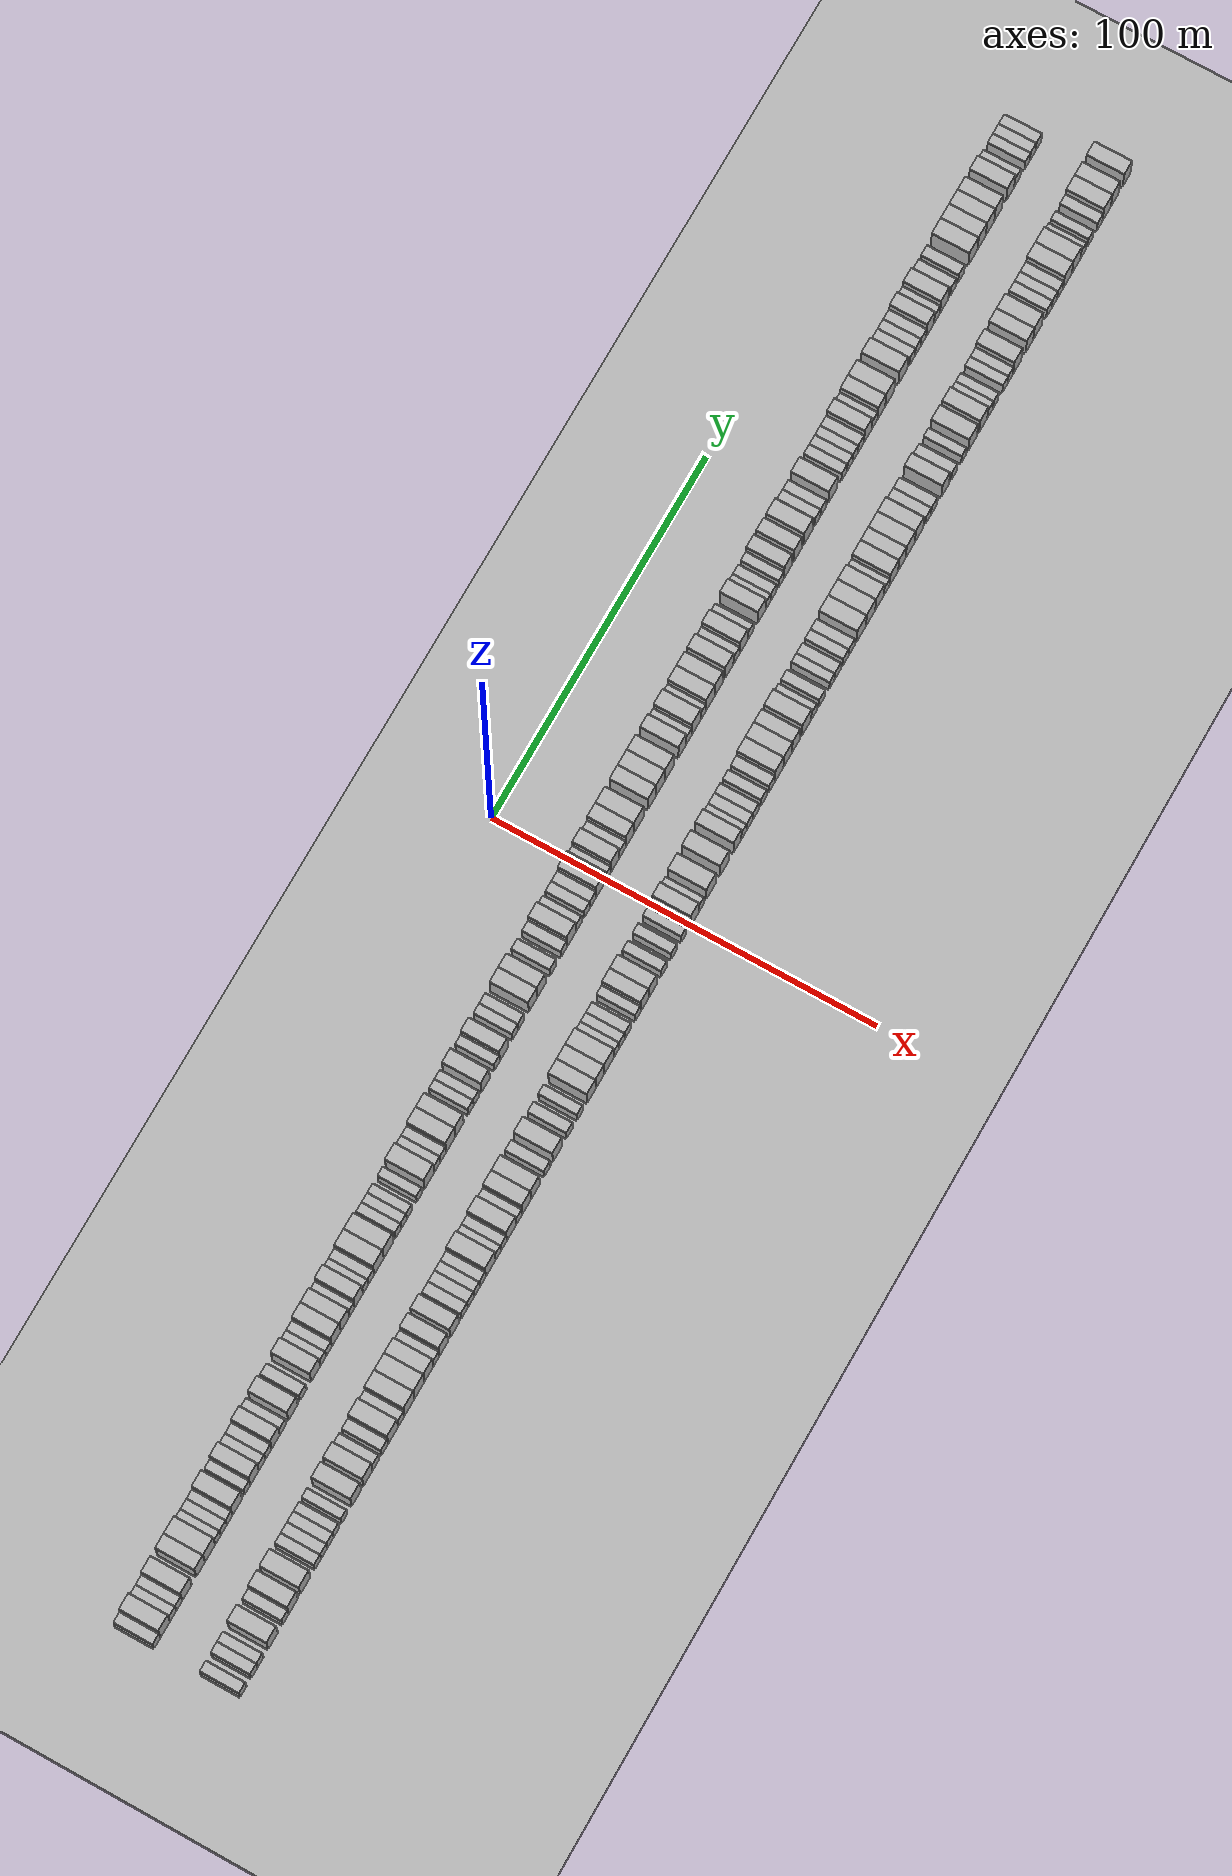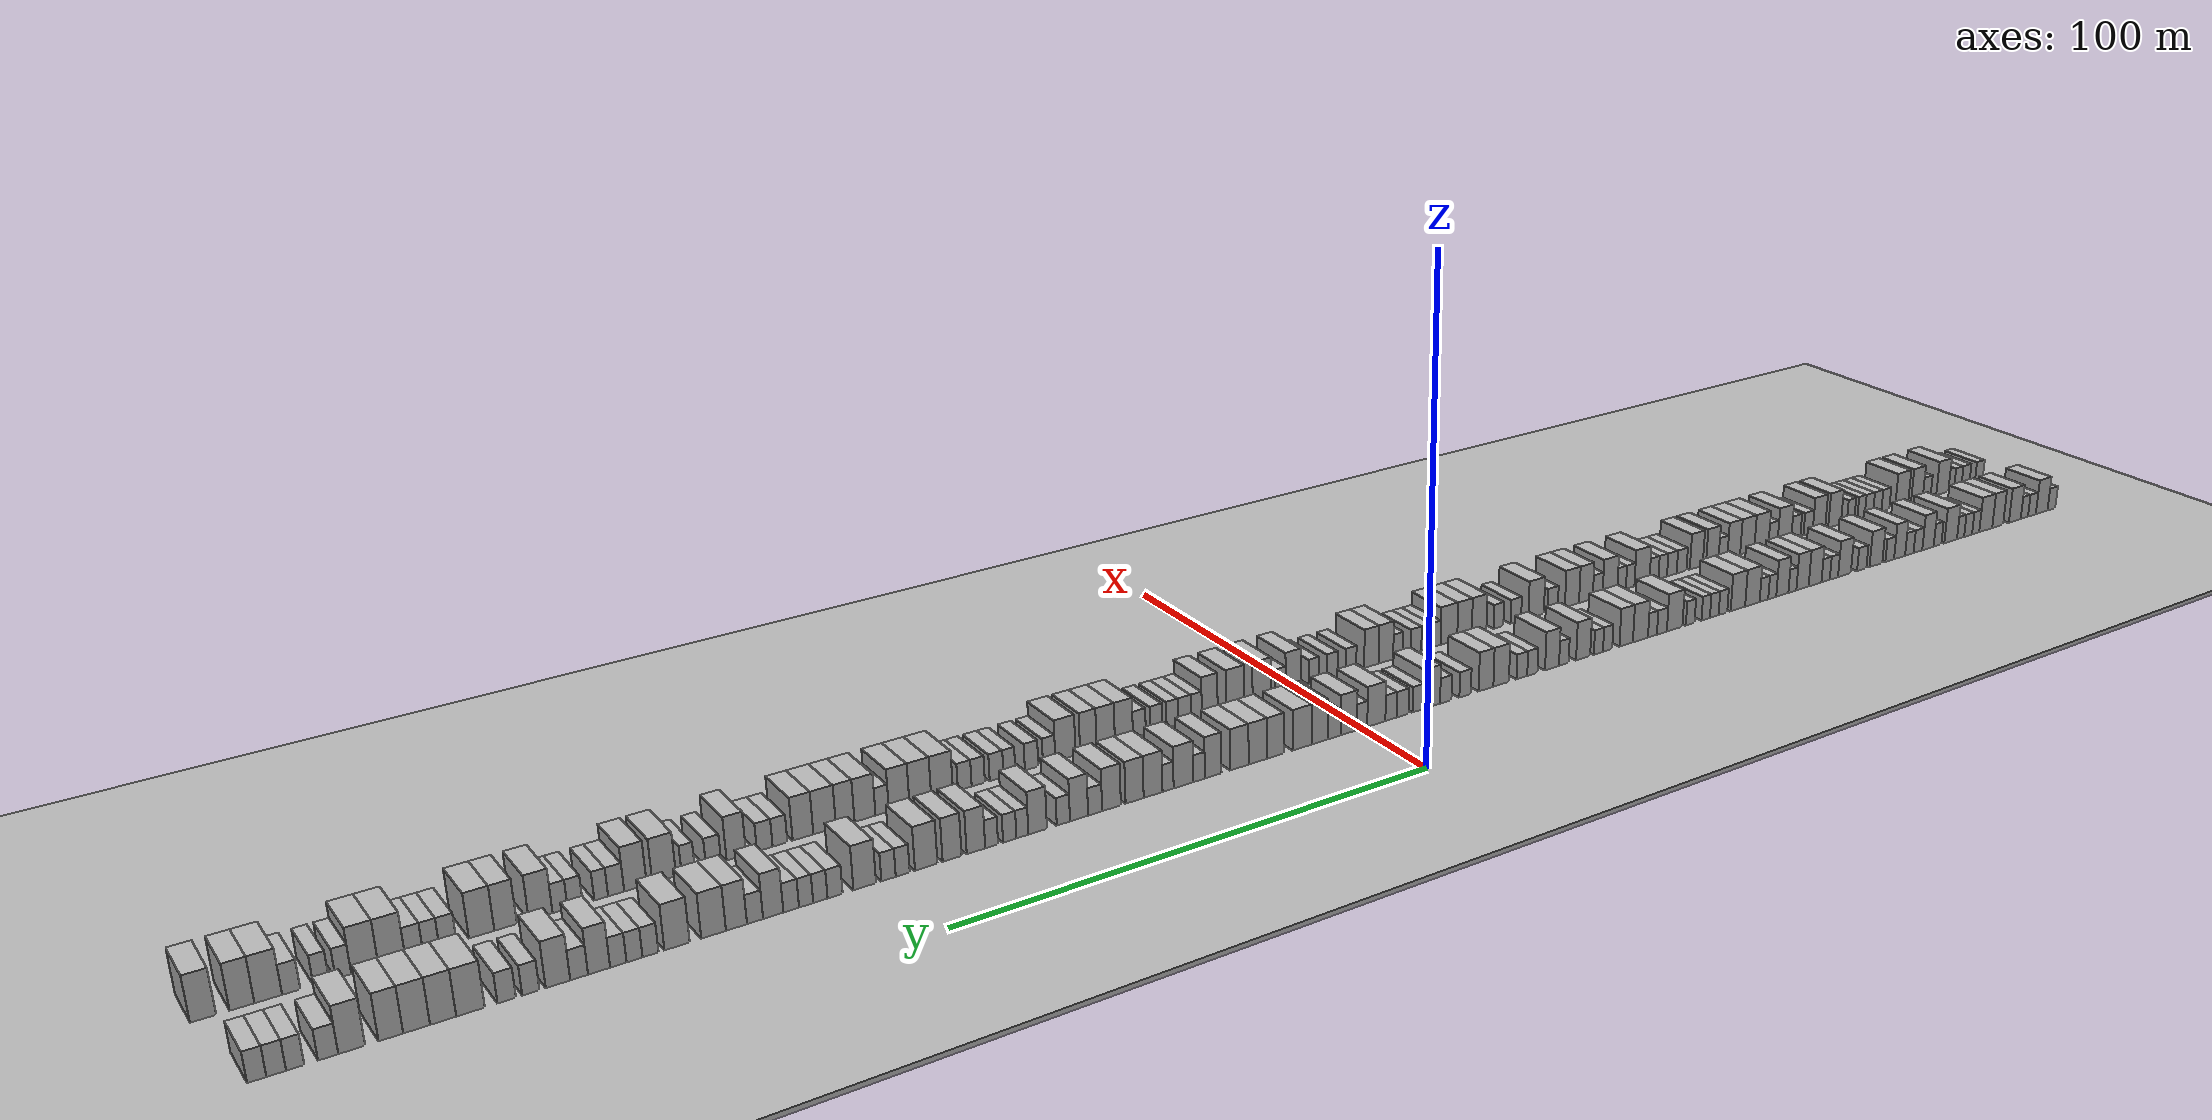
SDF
<?xml version="1.0" encoding="utf-8"?>

<sdf version="1.6">

   <world name="default">

      <gui fullscreen="0">

         <camera name="user_camera">

            <pose>-15 0 4.57585 0 0 0</pose>

            <view_controller>orbit</view_controller>

         </camera>

      </gui>

      <scene>

         <sky>

           <clouds>

             <speed>12</speed>

           </clouds>

         </sky>

         <ambient>0.4 0.4 0.4 1</ambient>

         <background>0.7 0.7 0.7 1</background>

         <shadows>1</shadows>

      </scene>

      <gravity>0 0 -9.8066</gravity>

      <magnetic_field>6e-06 2.3e-05 -4.2e-05</magnetic_field>

      <physics default="0" name="default_physics" type="ode">

         <ode>

            <solver>

               <type>quick</type>

               <iters>10</iters>

               <sor>1.0</sor>

               <use_dynamic_moi_rescaling>0</use_dynamic_moi_rescaling>

            </solver>

            <constraints>

               <cfm>0</cfm>

               <erp>0.2</erp>

               <contact_max_correcting_vel>100</contact_max_correcting_vel>

               <contact_surface_layer>0.001</contact_surface_layer>

            </constraints>

         </ode>

         <max_step_size>0.004</max_step_size>

         <real_time_factor>1</real_time_factor>

         <real_time_update_rate>250</real_time_update_rate>

      </physics>

      <light name="sun" type="directional">

         <cast_shadows>1</cast_shadows>

         <pose>0 0 10 0 0 0</pose>

         <diffuse>0.8 0.8 0.8 1</diffuse>

         <specular>0.2 0.2 0.2 1</specular>

         <attenuation>

            <range>1000</range>

            <constant>0.9</constant>

            <linear>0.01</linear>

            <quadratic>0.001</quadratic>

         </attenuation>

         <direction>-0.5 0.1 -0.9</direction>

      </light>

      <include>

         <name>ground_plane_1</name>

         <uri>model://HANNAS_ground_plane</uri>

         <pose>0 0 0  0 0 0</pose>

      </include>

      <include>

         <name>ground_plane_2</name>

         <uri>model://HANNAS_ground_plane</uri>

         <pose>100 0 0  0 0 0</pose>

      </include>

      <model name="building_1">

         <static>1</static>

         <pose frame="">25.0000 -201.6089 0 0.000000 0.000000 0.000000</pose>

         <link name="link">

            <pose frame="">0 0 3.00 0 0 0</pose>

            <collision name="collision">

               <geometry>

                  <box>

                     <size>10.0000 2.7822 6.0000</size>

                  </box>

               </geometry>

               <max_contacts>10</max_contacts>

               <surface>

                  <contact>

                     <ode/>

                  </contact>

                  <bounce/>

                  <friction>

                     <torsional>

                        <ode/>

                     </torsional>

                     <ode/>

                  </friction>

               </surface>

            </collision>

            <visual name="visual">

               <cast_shadows>0</cast_shadows>

               <geometry>

                  <box>

                     <size>10.0000 2.7822 6.0000</size>

                  </box>

               </geometry>

               <material>

                  <script>

                     <uri>model://HANNAS_wall/materials/scripts</uri>

                     <uri>model://HANNAS_wall/materials/textures</uri>

                     <name>vrc/HANNAS_wall</name>

                  </script>

               </material>

            </visual>

            <self_collide>0</self_collide>

            <enable_wind>0</enable_wind>

            <kinematic>0</kinematic>

         </link>

      </model>

      <model name="building_2">

         <static>1</static>

         <pose frame="">25.0000 -198.1275 0 0.000000 0.000000 0.000000</pose>

         <link name="link">

            <pose frame="">0 0 4.50 0 0 0</pose>

            <collision name="collision">

               <geometry>

                  <box>

                     <size>10.0000 4.1806 9.0000</size>

                  </box>

               </geometry>

               <max_contacts>10</max_contacts>

               <surface>

                  <contact>

                     <ode/>

                  </contact>

                  <bounce/>

                  <friction>

                     <torsional>

                        <ode/>

                     </torsional>

                     <ode/>

                  </friction>

               </surface>

            </collision>

            <visual name="visual">

               <cast_shadows>0</cast_shadows>

               <geometry>

                  <box>

                     <size>10.0000 4.1806 9.0000</size>

                  </box>

               </geometry>

               <material>

                  <script>

                     <uri>model://HANNAS_wall/materials/scripts</uri>

                     <uri>model://HANNAS_wall/materials/textures</uri>

                     <name>vrc/HANNAS_wall</name>

                  </script>

               </material>

            </visual>

            <self_collide>0</self_collide>

            <enable_wind>0</enable_wind>

            <kinematic>0</kinematic>

         </link>

      </model>

      <model name="building_3">

         <static>1</static>

         <pose frame="">25.0000 -194.6567 0 0.000000 0.000000 0.000000</pose>

         <link name="link">

            <pose frame="">0 0 3.00 0 0 0</pose>

            <collision name="collision">

               <geometry>

                  <box>

                     <size>10.0000 2.7611 6.0000</size>

                  </box>

               </geometry>

               <max_contacts>10</max_contacts>

               <surface>

                  <contact>

                     <ode/>

                  </contact>

                  <bounce/>

                  <friction>

                     <torsional>

                        <ode/>

                     </torsional>

                     <ode/>

                  </friction>

               </surface>

            </collision>

            <visual name="visual">

               <cast_shadows>0</cast_shadows>

               <geometry>

                  <box>

                     <size>10.0000 2.7611 6.0000</size>

                  </box>

               </geometry>

               <material>

                  <script>

                     <uri>model://HANNAS_wall/materials/scripts</uri>

                     <uri>model://HANNAS_wall/materials/textures</uri>

                     <name>vrc/HANNAS_wall</name>

                  </script>

               </material>

            </visual>

            <self_collide>0</self_collide>

            <enable_wind>0</enable_wind>

            <kinematic>0</kinematic>

         </link>

      </model>

      <model name="building_4">

         <static>1</static>

         <pose frame="">25.0000 -191.9876 0 0.000000 0.000000 0.000000</pose>

         <link name="link">

            <pose frame="">0 0 3.00 0 0 0</pose>

            <collision name="collision">

               <geometry>

                  <box>

                     <size>10.0000 2.5771 6.0000</size>

                  </box>

               </geometry>

               <max_contacts>10</max_contacts>

               <surface>

                  <contact>

                     <ode/>

                  </contact>

                  <bounce/>

                  <friction>

                     <torsional>

                        <ode/>

                     </torsional>

                     <ode/>

                  </friction>

               </surface>

            </collision>

            <visual name="visual">

               <cast_shadows>0</cast_shadows>

               <geometry>

                  <box>

                     <size>10.0000 2.5771 6.0000</size>

                  </box>

               </geometry>

               <material>

                  <script>

                     <uri>model://HANNAS_wall/materials/scripts</uri>

                     <uri>model://HANNAS_wall/materials/textures</uri>

                     <name>vrc/HANNAS_wall</name>

                  </script>

               </material>

            </visual>

            <self_collide>0</self_collide>

            <enable_wind>0</enable_wind>

            <kinematic>0</kinematic>

         </link>

      </model>

      <model name="building_5">

         <static>1</static>

         <pose frame="">25.0000 -188.6193 0 0.000000 0.000000 0.000000</pose>

         <link name="link">

            <pose frame="">0 0 4.50 0 0 0</pose>

            <collision name="collision">

               <geometry>

                  <box>

                     <size>10.0000 4.1595 9.0000</size>

                  </box>

               </geometry>

               <max_contacts>10</max_contacts>

               <surface>

                  <contact>

                     <ode/>

                  </contact>

                  <bounce/>

                  <friction>

                     <torsional>

                        <ode/>

                     </torsional>

                     <ode/>

                  </friction>

               </surface>

            </collision>

            <visual name="visual">

               <cast_shadows>0</cast_shadows>

               <geometry>

                  <box>

                     <size>10.0000 4.1595 9.0000</size>

                  </box>

               </geometry>

               <material>

                  <script>

                     <uri>model://HANNAS_wall/materials/scripts</uri>

                     <uri>model://HANNAS_wall/materials/textures</uri>

                     <name>vrc/HANNAS_wall</name>

                  </script>

               </material>

            </visual>

            <self_collide>0</self_collide>

            <enable_wind>0</enable_wind>

            <kinematic>0</kinematic>

         </link>

      </model>

      <model name="building_6">

         <static>1</static>

         <pose frame="">25.0000 -182.6517 0 0.000000 0.000000 0.000000</pose>

         <link name="link">

            <pose frame="">0 0 4.50 0 0 0</pose>

            <collision name="collision">

               <geometry>

                  <box>

                     <size>10.0000 3.7756 9.0000</size>

                  </box>

               </geometry>

               <max_contacts>10</max_contacts>

               <surface>

                  <contact>

                     <ode/>

                  </contact>

                  <bounce/>

                  <friction>

                     <torsional>

                        <ode/>

                     </torsional>

                     <ode/>

                  </friction>

               </surface>

            </collision>

            <visual name="visual">

               <cast_shadows>0</cast_shadows>

               <geometry>

                  <box>

                     <size>10.0000 3.7756 9.0000</size>

                  </box>

               </geometry>

               <material>

                  <script>

                     <uri>model://HANNAS_wall/materials/scripts</uri>

                     <uri>model://HANNAS_wall/materials/textures</uri>

                     <name>vrc/HANNAS_wall</name>

                  </script>

               </material>

            </visual>

            <self_collide>0</self_collide>

            <enable_wind>0</enable_wind>

            <kinematic>0</kinematic>

         </link>

      </model>

      <model name="building_7">

         <static>1</static>

         <pose frame="">25.0000 -178.5277 0 0.000000 0.000000 0.000000</pose>

         <link name="link">

            <pose frame="">0 0 4.50 0 0 0</pose>

            <collision name="collision">

               <geometry>

                  <box>

                     <size>10.0000 4.4723 9.0000</size>

                  </box>

               </geometry>

               <max_contacts>10</max_contacts>

               <surface>

                  <contact>

                     <ode/>

                  </contact>

                  <bounce/>

                  <friction>

                     <torsional>

                        <ode/>

                     </torsional>

                     <ode/>

                  </friction>

               </surface>

            </collision>

            <visual name="visual">

               <cast_shadows>0</cast_shadows>

               <geometry>

                  <box>

                     <size>10.0000 4.4723 9.0000</size>

                  </box>

               </geometry>

               <material>

                  <script>

                     <uri>model://HANNAS_wall/materials/scripts</uri>

                     <uri>model://HANNAS_wall/materials/textures</uri>

                     <name>vrc/HANNAS_wall</name>

                  </script>

               </material>

            </visual>

            <self_collide>0</self_collide>

            <enable_wind>0</enable_wind>

            <kinematic>0</kinematic>

         </link>

      </model>

      <model name="building_8">

         <static>1</static>

         <pose frame="">25.0000 -175.0698 0 0.000000 0.000000 0.000000</pose>

         <link name="link">

            <pose frame="">0 0 3.00 0 0 0</pose>

            <collision name="collision">

               <geometry>

                  <box>

                     <size>10.0000 2.4434 6.0000</size>

                  </box>

               </geometry>

               <max_contacts>10</max_contacts>

               <surface>

                  <contact>

                     <ode/>

                  </contact>

                  <bounce/>

                  <friction>

                     <torsional>

                        <ode/>

                     </torsional>

                     <ode/>

                  </friction>

               </surface>

            </collision>

            <visual name="visual">

               <cast_shadows>0</cast_shadows>

               <geometry>

                  <box>

                     <size>10.0000 2.4434 6.0000</size>

                  </box>

               </geometry>

               <material>

                  <script>

                     <uri>model://HANNAS_wall/materials/scripts</uri>

                     <uri>model://HANNAS_wall/materials/textures</uri>

                     <name>vrc/HANNAS_wall</name>

                  </script>

               </material>

            </visual>

            <self_collide>0</self_collide>

            <enable_wind>0</enable_wind>

            <kinematic>0</kinematic>

         </link>

      </model>

      <model name="building_9">

         <static>1</static>

         <pose frame="">25.0000 -172.4947 0 0.000000 0.000000 0.000000</pose>

         <link name="link">

            <pose frame="">0 0 3.00 0 0 0</pose>

            <collision name="collision">

               <geometry>

                  <box>

                     <size>10.0000 2.7070 6.0000</size>

                  </box>

               </geometry>

               <max_contacts>10</max_contacts>

               <surface>

                  <contact>

                     <ode/>

                  </contact>

                  <bounce/>

                  <friction>

                     <torsional>

                        <ode/>

                     </torsional>

                     <ode/>

                  </friction>

               </surface>

            </collision>

            <visual name="visual">

               <cast_shadows>0</cast_shadows>

               <geometry>

                  <box>

                     <size>10.0000 2.7070 6.0000</size>

                  </box>

               </geometry>

               <material>

                  <script>

                     <uri>model://HANNAS_wall/materials/scripts</uri>

                     <uri>model://HANNAS_wall/materials/textures</uri>

                     <name>vrc/HANNAS_wall</name>

                  </script>

               </material>

            </visual>

            <self_collide>0</self_collide>

            <enable_wind>0</enable_wind>

            <kinematic>0</kinematic>

         </link>

      </model>

      <model name="building_10">

         <static>1</static>

         <pose frame="">25.0000 -169.9263 0 0.000000 0.000000 0.000000</pose>

         <link name="link">

            <pose frame="">0 0 3.00 0 0 0</pose>

            <collision name="collision">

               <geometry>

                  <box>

                     <size>10.0000 2.4297 6.0000</size>

                  </box>

               </geometry>

               <max_contacts>10</max_contacts>

               <surface>

                  <contact>

                     <ode/>

                  </contact>

                  <bounce/>

                  <friction>

                     <torsional>

                        <ode/>

                     </torsional>

                     <ode/>

                  </friction>

               </surface>

            </collision>

            <visual name="visual">

               <cast_shadows>0</cast_shadows>

               <geometry>

                  <box>

                     <size>10.0000 2.4297 6.0000</size>

                  </box>

               </geometry>

               <material>

                  <script>

                     <uri>model://HANNAS_wall/materials/scripts</uri>

                     <uri>model://HANNAS_wall/materials/textures</uri>

                     <name>vrc/HANNAS_wall</name>

                  </script>

               </material>

            </visual>

            <self_collide>0</self_collide>

            <enable_wind>0</enable_wind>

            <kinematic>0</kinematic>

         </link>

      </model>

      <model name="building_11">

         <static>1</static>

         <pose frame="">25.0000 -166.5794 0 0.000000 0.000000 0.000000</pose>

         <link name="link">

            <pose frame="">0 0 4.50 0 0 0</pose>

            <collision name="collision">

               <geometry>

                  <box>

                     <size>10.0000 4.2642 9.0000</size>

                  </box>

               </geometry>

               <max_contacts>10</max_contacts>

               <surface>

                  <contact>

                     <ode/>

                  </contact>

                  <bounce/>

                  <friction>

                     <torsional>

                        <ode/>

                     </torsional>

                     <ode/>

                  </friction>

               </surface>

            </collision>

            <visual name="visual">

               <cast_shadows>0</cast_shadows>

               <geometry>

                  <box>

                     <size>10.0000 4.2642 9.0000</size>

                  </box>

               </geometry>

               <material>

                  <script>

                     <uri>model://HANNAS_wall/materials/scripts</uri>

                     <uri>model://HANNAS_wall/materials/textures</uri>

                     <name>vrc/HANNAS_wall</name>

                  </script>

               </material>

            </visual>

            <self_collide>0</self_collide>

            <enable_wind>0</enable_wind>

            <kinematic>0</kinematic>

         </link>

      </model>

      <model name="building_12">

         <static>1</static>

         <pose frame="">25.0000 -162.1725 0 0.000000 0.000000 0.000000</pose>

         <link name="link">

            <pose frame="">0 0 3.00 0 0 0</pose>

            <collision name="collision">

               <geometry>

                  <box>

                     <size>10.0000 2.5494 6.0000</size>

                  </box>

               </geometry>

               <max_contacts>10</max_contacts>

               <surface>

                  <contact>

                     <ode/>

                  </contact>

                  <bounce/>

                  <friction>

                     <torsional>

                        <ode/>

                     </torsional>

                     <ode/>

                  </friction>

               </surface>

            </collision>

            <visual name="visual">

               <cast_shadows>0</cast_shadows>

               <geometry>

                  <box>

                     <size>10.0000 2.5494 6.0000</size>

                  </box>

               </geometry>

               <material>

                  <script>

                     <uri>model://HANNAS_wall/materials/scripts</uri>

                     <uri>model://HANNAS_wall/materials/textures</uri>

                     <name>vrc/HANNAS_wall</name>

                  </script>

               </material>

            </visual>

            <self_collide>0</self_collide>

            <enable_wind>0</enable_wind>

            <kinematic>0</kinematic>

         </link>

      </model>

      <model name="building_13">

         <static>1</static>

         <pose frame="">25.0000 -159.0019 0 0.000000 0.000000 0.000000</pose>

         <link name="link">

            <pose frame="">0 0 4.50 0 0 0</pose>

            <collision name="collision">

               <geometry>

                  <box>

                     <size>10.0000 3.7918 9.0000</size>

                  </box>

               </geometry>

               <max_contacts>10</max_contacts>

               <surface>

                  <contact>

                     <ode/>

                  </contact>

                  <bounce/>

                  <friction>

                     <torsional>

                        <ode/>

                     </torsional>

                     <ode/>

                  </friction>

               </surface>

            </collision>

            <visual name="visual">

               <cast_shadows>0</cast_shadows>

               <geometry>

                  <box>

                     <size>10.0000 3.7918 9.0000</size>

                  </box>

               </geometry>

               <material>

                  <script>

                     <uri>model://HANNAS_wall/materials/scripts</uri>

                     <uri>model://HANNAS_wall/materials/textures</uri>

                     <name>vrc/HANNAS_wall</name>

                  </script>

               </material>

            </visual>

            <self_collide>0</self_collide>

            <enable_wind>0</enable_wind>

            <kinematic>0</kinematic>

         </link>

      </model>

      <model name="building_14">

         <static>1</static>

         <pose frame="">25.0000 -155.6749 0 0.000000 0.000000 0.000000</pose>

         <link name="link">

            <pose frame="">0 0 3.00 0 0 0</pose>

            <collision name="collision">

               <geometry>

                  <box>

                     <size>10.0000 2.8622 6.0000</size>

                  </box>

               </geometry>

               <max_contacts>10</max_contacts>

               <surface>

                  <contact>

                     <ode/>

                  </contact>

                  <bounce/>

                  <friction>

                     <torsional>

                        <ode/>

                     </torsional>

                     <ode/>

                  </friction>

               </surface>

            </collision>

            <visual name="visual">

               <cast_shadows>0</cast_shadows>

               <geometry>

                  <box>

                     <size>10.0000 2.8622 6.0000</size>

                  </box>

               </geometry>

               <material>

                  <script>

                     <uri>model://HANNAS_wall/materials/scripts</uri>

                     <uri>model://HANNAS_wall/materials/textures</uri>

                     <name>vrc/HANNAS_wall</name>

                  </script>

               </material>

            </visual>

            <self_collide>0</self_collide>

            <enable_wind>0</enable_wind>

            <kinematic>0</kinematic>

         </link>

      </model>

      <model name="building_15">

         <static>1</static>

         <pose frame="">25.0000 -152.8484 0 0.000000 0.000000 0.000000</pose>

         <link name="link">

            <pose frame="">0 0 3.00 0 0 0</pose>

            <collision name="collision">

               <geometry>

                  <box>

                     <size>10.0000 2.7909 6.0000</size>

                  </box>

               </geometry>

               <max_contacts>10</max_contacts>

               <surface>

                  <contact>

                     <ode/>

                  </contact>

                  <bounce/>

                  <friction>

                     <torsional>

                        <ode/>

                     </torsional>

                     <ode/>

                  </friction>

               </surface>

            </collision>

            <visual name="visual">

               <cast_shadows>0</cast_shadows>

               <geometry>

                  <box>

                     <size>10.0000 2.7909 6.0000</size>

                  </box>

               </geometry>

               <material>

                  <script>

                     <uri>model://HANNAS_wall/materials/scripts</uri>

                     <uri>model://HANNAS_wall/materials/textures</uri>

                     <name>vrc/HANNAS_wall</name>

                  </script>

               </material>

            </visual>

            <self_collide>0</self_collide>

            <enable_wind>0</enable_wind>

            <kinematic>0</kinematic>

         </link>

      </model>

      <model name="building_16">

         <static>1</static>

         <pose frame="">25.0000 -149.6507 0 0.000000 0.000000 0.000000</pose>

         <link name="link">

            <pose frame="">0 0 4.50 0 0 0</pose>

            <collision name="collision">

               <geometry>

                  <box>

                     <size>10.0000 3.6045 9.0000</size>

                  </box>

               </geometry>

               <max_contacts>10</max_contacts>

               <surface>

                  <contact>

                     <ode/>

                  </contact>

                  <bounce/>

                  <friction>

                     <torsional>

                        <ode/>

                     </torsional>

                     <ode/>

                  </friction>

               </surface>

            </collision>

            <visual name="visual">

               <cast_shadows>0</cast_shadows>

               <geometry>

                  <box>

                     <size>10.0000 3.6045 9.0000</size>

                  </box>

               </geometry>

               <material>

                  <script>

                     <uri>model://HANNAS_wall/materials/scripts</uri>

                     <uri>model://HANNAS_wall/materials/textures</uri>

                     <name>vrc/HANNAS_wall</name>

                  </script>

               </material>

            </visual>

            <self_collide>0</self_collide>

            <enable_wind>0</enable_wind>

            <kinematic>0</kinematic>

         </link>

      </model>

      <model name="building_17">

         <static>1</static>

         <pose frame="">25.0000 -146.4542 0 0.000000 0.000000 0.000000</pose>

         <link name="link">

            <pose frame="">0 0 3.00 0 0 0</pose>

            <collision name="collision">

               <geometry>

                  <box>

                     <size>10.0000 2.7886 6.0000</size>

                  </box>

               </geometry>

               <max_contacts>10</max_contacts>

               <surface>

                  <contact>

                     <ode/>

                  </contact>

                  <bounce/>

                  <friction>

                     <torsional>

                        <ode/>

                     </torsional>

                     <ode/>

                  </friction>

               </surface>

            </collision>

            <visual name="visual">

               <cast_shadows>0</cast_shadows>

               <geometry>

                  <box>

                     <size>10.0000 2.7886 6.0000</size>

                  </box>

               </geometry>

               <material>

                  <script>

                     <uri>model://HANNAS_wall/materials/scripts</uri>

                     <uri>model://HANNAS_wall/materials/textures</uri>

                     <name>vrc/HANNAS_wall</name>

                  </script>

               </material>

            </visual>

            <self_collide>0</self_collide>

            <enable_wind>0</enable_wind>

            <kinematic>0</kinematic>

         </link>

      </model>

      <model name="building_18">

         <static>1</static>

         <pose frame="">25.0000 -142.0070 0 0.000000 0.000000 0.000000</pose>

         <link name="link">

            <pose frame="">0 0 4.50 0 0 0</pose>

            <collision name="collision">

               <geometry>

                  <box>

                     <size>10.0000 4.1057 9.0000</size>

                  </box>

               </geometry>

               <max_contacts>10</max_contacts>

               <surface>

                  <contact>

                     <ode/>

                  </contact>

                  <bounce/>

                  <friction>

                     <torsional>

                        <ode/>

                     </torsional>

                     <ode/>

                  </friction>

               </surface>

            </collision>

            <visual name="visual">

               <cast_shadows>0</cast_shadows>

               <geometry>

                  <box>

                     <size>10.0000 4.1057 9.0000</size>

                  </box>

               </geometry>

               <material>

                  <script>

                     <uri>model://HANNAS_wall/materials/scripts</uri>

                     <uri>model://HANNAS_wall/materials/textures</uri>

                     <name>vrc/HANNAS_wall</name>

                  </script>

               </material>

            </visual>

            <self_collide>0</self_collide>

            <enable_wind>0</enable_wind>

            <kinematic>0</kinematic>

         </link>

      </model>

      <model name="building_19">

         <static>1</static>

         <pose frame="">25.0000 -137.4761 0 0.000000 0.000000 0.000000</pose>

         <link name="link">

            <pose frame="">0 0 3.00 0 0 0</pose>

            <collision name="collision">

               <geometry>

                  <box>

                     <size>10.0000 2.9560 6.0000</size>

                  </box>

               </geometry>

               <max_contacts>10</max_contacts>

               <surface>

                  <contact>

                     <ode/>

                  </contact>

                  <bounce/>

                  <friction>

                     <torsional>

                        <ode/>

                     </torsional>

                     <ode/>

                  </friction>

               </surface>

            </collision>

            <visual name="visual">

               <cast_shadows>0</cast_shadows>

               <geometry>

                  <box>

                     <size>10.0000 2.9560 6.0000</size>

                  </box>

               </geometry>

               <material>

                  <script>

                     <uri>model://HANNAS_wall/materials/scripts</uri>

                     <uri>model://HANNAS_wall/materials/textures</uri>

                     <name>vrc/HANNAS_wall</name>

                  </script>

               </material>

            </visual>

            <self_collide>0</self_collide>

            <enable_wind>0</enable_wind>

            <kinematic>0</kinematic>

         </link>

      </model>

      <model name="building_20">

         <static>1</static>

         <pose frame="">25.0000 -131.9859 0 0.000000 0.000000 0.000000</pose>

         <link name="link">

            <pose frame="">0 0 4.50 0 0 0</pose>

            <collision name="collision">

               <geometry>

                  <box>

                     <size>10.0000 4.0244 9.0000</size>

                  </box>

               </geometry>

               <max_contacts>10</max_contacts>

               <surface>

                  <contact>

                     <ode/>

                  </contact>

                  <bounce/>

                  <friction>

                     <torsional>

                        <ode/>

                     </torsional>

                     <ode/>

                  </friction>

               </surface>

            </collision>

            <visual name="visual">

               <cast_shadows>0</cast_shadows>

               <geometry>

                  <box>

                     <size>10.0000 4.0244 9.0000</size>

                  </box>

               </geometry>

               <material>

                  <script>

                     <uri>model://HANNAS_wall/materials/scripts</uri>

                     <uri>model://HANNAS_wall/materials/textures</uri>

                     <name>vrc/HANNAS_wall</name>

                  </script>

               </material>

            </visual>

            <self_collide>0</self_collide>

            <enable_wind>0</enable_wind>

            <kinematic>0</kinematic>

         </link>

      </model>

      <model name="building_21">

         <static>1</static>

         <pose frame="">25.0000 -128.6789 0 0.000000 0.000000 0.000000</pose>

         <link name="link">

            <pose frame="">0 0 3.00 0 0 0</pose>

            <collision name="collision">

               <geometry>

                  <box>

                     <size>10.0000 2.5896 6.0000</size>

                  </box>

               </geometry>

               <max_contacts>10</max_contacts>

               <surface>

                  <contact>

                     <ode/>

                  </contact>

                  <bounce/>

                  <friction>

                     <torsional>

                        <ode/>

                     </torsional>

                     <ode/>

                  </friction>

               </surface>

            </collision>

            <visual name="visual">

               <cast_shadows>0</cast_shadows>

               <geometry>

                  <box>

                     <size>10.0000 2.5896 6.0000</size>

                  </box>

               </geometry>

               <material>

                  <script>

                     <uri>model://HANNAS_wall/materials/scripts</uri>

                     <uri>model://HANNAS_wall/materials/textures</uri>

                     <name>vrc/HANNAS_wall</name>

                  </script>

               </material>

            </visual>

            <self_collide>0</self_collide>

            <enable_wind>0</enable_wind>

            <kinematic>0</kinematic>

         </link>

      </model>

      <model name="building_22">

         <static>1</static>

         <pose frame="">25.0000 -126.0847 0 0.000000 0.000000 0.000000</pose>

         <link name="link">

            <pose frame="">0 0 3.00 0 0 0</pose>

            <collision name="collision">

               <geometry>

                  <box>

                     <size>10.0000 2.5989 6.0000</size>

                  </box>

               </geometry>

               <max_contacts>10</max_contacts>

               <surface>

                  <contact>

                     <ode/>

                  </contact>

                  <bounce/>

                  <friction>

                     <torsional>

                        <ode/>

                     </torsional>

                     <ode/>

                  </friction>

               </surface>

            </collision>

            <visual name="visual">

               <cast_shadows>0</cast_shadows>

               <geometry>

                  <box>

                     <size>10.0000 2.5989 6.0000</size>

                  </box>

               </geometry>

               <material>

                  <script>

                     <uri>model://HANNAS_wall/materials/scripts</uri>

                     <uri>model://HANNAS_wall/materials/textures</uri>

                     <name>vrc/HANNAS_wall</name>

                  </script>

               </material>

            </visual>

            <self_collide>0</self_collide>

            <enable_wind>0</enable_wind>

            <kinematic>0</kinematic>

         </link>

      </model>

      <model name="building_23">

         <static>1</static>

         <pose frame="">25.0000 -122.8074 0 0.000000 0.000000 0.000000</pose>

         <link name="link">

            <pose frame="">0 0 4.50 0 0 0</pose>

            <collision name="collision">

               <geometry>

                  <box>

                     <size>10.0000 3.9556 9.0000</size>

                  </box>

               </geometry>

               <max_contacts>10</max_contacts>

               <surface>

                  <contact>

                     <ode/>

                  </contact>

                  <bounce/>

                  <friction>

                     <torsional>

                        <ode/>

                     </torsional>

                     <ode/>

                  </friction>

               </surface>

            </collision>

            <visual name="visual">

               <cast_shadows>0</cast_shadows>

               <geometry>

                  <box>

                     <size>10.0000 3.9556 9.0000</size>

                  </box>

               </geometry>

               <material>

                  <script>

                     <uri>model://HANNAS_wall/materials/scripts</uri>

                     <uri>model://HANNAS_wall/materials/textures</uri>

                     <name>vrc/HANNAS_wall</name>

                  </script>

               </material>

            </visual>

            <self_collide>0</self_collide>

            <enable_wind>0</enable_wind>

            <kinematic>0</kinematic>

         </link>

      </model>

      <model name="building_24">

         <static>1</static>

         <pose frame="">25.0000 -118.9435 0 0.000000 0.000000 0.000000</pose>

         <link name="link">

            <pose frame="">0 0 4.50 0 0 0</pose>

            <collision name="collision">

               <geometry>

                  <box>

                     <size>10.0000 3.7723 9.0000</size>

                  </box>

               </geometry>

               <max_contacts>10</max_contacts>

               <surface>

                  <contact>

                     <ode/>

                  </contact>

                  <bounce/>

                  <friction>

                     <torsional>

                        <ode/>

                     </torsional>

                     <ode/>

                  </friction>

               </surface>

            </collision>

            <visual name="visual">

               <cast_shadows>0</cast_shadows>

               <geometry>

                  <box>

                     <size>10.0000 3.7723 9.0000</size>

                  </box>

               </geometry>

               <material>

                  <script>

                     <uri>model://HANNAS_wall/materials/scripts</uri>

                     <uri>model://HANNAS_wall/materials/textures</uri>

                     <name>vrc/HANNAS_wall</name>

                  </script>

               </material>

            </visual>

            <self_collide>0</self_collide>

            <enable_wind>0</enable_wind>

            <kinematic>0</kinematic>

         </link>

      </model>

      <model name="building_25">

         <static>1</static>

         <pose frame="">25.0000 -115.8389 0 0.000000 0.000000 0.000000</pose>

         <link name="link">

            <pose frame="">0 0 3.00 0 0 0</pose>

            <collision name="collision">

               <geometry>

                  <box>

                     <size>10.0000 2.4369 6.0000</size>

                  </box>

               </geometry>

               <max_contacts>10</max_contacts>

               <surface>

                  <contact>

                     <ode/>

                  </contact>

                  <bounce/>

                  <friction>

                     <torsional>

                        <ode/>

                     </torsional>

                     <ode/>

                  </friction>

               </surface>

            </collision>

            <visual name="visual">

               <cast_shadows>0</cast_shadows>

               <geometry>

                  <box>

                     <size>10.0000 2.4369 6.0000</size>

                  </box>

               </geometry>

               <material>

                  <script>

                     <uri>model://HANNAS_wall/materials/scripts</uri>

                     <uri>model://HANNAS_wall/materials/textures</uri>

                     <name>vrc/HANNAS_wall</name>

                  </script>

               </material>

            </visual>

            <self_collide>0</self_collide>

            <enable_wind>0</enable_wind>

            <kinematic>0</kinematic>

         </link>

      </model>

      <model name="building_26">

         <static>1</static>

         <pose frame="">25.0000 -112.7726 0 0.000000 0.000000 0.000000</pose>

         <link name="link">

            <pose frame="">0 0 4.50 0 0 0</pose>

            <collision name="collision">

               <geometry>

                  <box>

                     <size>10.0000 3.6957 9.0000</size>

                  </box>

               </geometry>

               <max_contacts>10</max_contacts>

               <surface>

                  <contact>

                     <ode/>

                  </contact>

                  <bounce/>

                  <friction>

                     <torsional>

                        <ode/>

                     </torsional>

                     <ode/>

                  </friction>

               </surface>

            </collision>

            <visual name="visual">

               <cast_shadows>0</cast_shadows>

               <geometry>

                  <box>

                     <size>10.0000 3.6957 9.0000</size>

                  </box>

               </geometry>

               <material>

                  <script>

                     <uri>model://HANNAS_wall/materials/scripts</uri>

                     <uri>model://HANNAS_wall/materials/textures</uri>

                     <name>vrc/HANNAS_wall</name>

                  </script>

               </material>

            </visual>

            <self_collide>0</self_collide>

            <enable_wind>0</enable_wind>

            <kinematic>0</kinematic>

         </link>

      </model>

      <model name="building_27">

         <static>1</static>

         <pose frame="">25.0000 -109.7204 0 0.000000 0.000000 0.000000</pose>

         <link name="link">

            <pose frame="">0 0 3.00 0 0 0</pose>

            <collision name="collision">

               <geometry>

                  <box>

                     <size>10.0000 2.4086 6.0000</size>

                  </box>

               </geometry>

               <max_contacts>10</max_contacts>

               <surface>

                  <contact>

                     <ode/>

                  </contact>

                  <bounce/>

                  <friction>

                     <torsional>

                        <ode/>

                     </torsional>

                     <ode/>

                  </friction>

               </surface>

            </collision>

            <visual name="visual">

               <cast_shadows>0</cast_shadows>

               <geometry>

                  <box>

                     <size>10.0000 2.4086 6.0000</size>

                  </box>

               </geometry>

               <material>

                  <script>

                     <uri>model://HANNAS_wall/materials/scripts</uri>

                     <uri>model://HANNAS_wall/materials/textures</uri>

                     <name>vrc/HANNAS_wall</name>

                  </script>

               </material>

            </visual>

            <self_collide>0</self_collide>

            <enable_wind>0</enable_wind>

            <kinematic>0</kinematic>

         </link>

      </model>

      <model name="building_28">

         <static>1</static>

         <pose frame="">25.0000 -107.2191 0 0.000000 0.000000 0.000000</pose>

         <link name="link">

            <pose frame="">0 0 3.00 0 0 0</pose>

            <collision name="collision">

               <geometry>

                  <box>

                     <size>10.0000 2.5940 6.0000</size>

                  </box>

               </geometry>

               <max_contacts>10</max_contacts>

               <surface>

                  <contact>

                     <ode/>

                  </contact>

                  <bounce/>

                  <friction>

                     <torsional>

                        <ode/>

                     </torsional>

                     <ode/>

                  </friction>

               </surface>

            </collision>

            <visual name="visual">

               <cast_shadows>0</cast_shadows>

               <geometry>

                  <box>

                     <size>10.0000 2.5940 6.0000</size>

                  </box>

               </geometry>

               <material>

                  <script>

                     <uri>model://HANNAS_wall/materials/scripts</uri>

                     <uri>model://HANNAS_wall/materials/textures</uri>

                     <name>vrc/HANNAS_wall</name>

                  </script>

               </material>

            </visual>

            <self_collide>0</self_collide>

            <enable_wind>0</enable_wind>

            <kinematic>0</kinematic>

         </link>

      </model>

      <model name="building_29">

         <static>1</static>

         <pose frame="">25.0000 -103.7713 0 0.000000 0.000000 0.000000</pose>

         <link name="link">

            <pose frame="">0 0 4.50 0 0 0</pose>

            <collision name="collision">

               <geometry>

                  <box>

                     <size>10.0000 4.3016 9.0000</size>

                  </box>

               </geometry>

               <max_contacts>10</max_contacts>

               <surface>

                  <contact>

                     <ode/>

                  </contact>

                  <bounce/>

                  <friction>

                     <torsional>

                        <ode/>

                     </torsional>

                     <ode/>

                  </friction>

               </surface>

            </collision>

            <visual name="visual">

               <cast_shadows>0</cast_shadows>

               <geometry>

                  <box>

                     <size>10.0000 4.3016 9.0000</size>

                  </box>

               </geometry>

               <material>

                  <script>

                     <uri>model://HANNAS_wall/materials/scripts</uri>

                     <uri>model://HANNAS_wall/materials/textures</uri>

                     <name>vrc/HANNAS_wall</name>

                  </script>

               </material>

            </visual>

            <self_collide>0</self_collide>

            <enable_wind>0</enable_wind>

            <kinematic>0</kinematic>

         </link>

      </model>

      <model name="building_30">

         <static>1</static>

         <pose frame="">25.0000 -99.4727 0 0.000000 0.000000 0.000000</pose>

         <link name="link">

            <pose frame="">0 0 4.50 0 0 0</pose>

            <collision name="collision">

               <geometry>

                  <box>

                     <size>10.0000 4.2955 9.0000</size>

                  </box>

               </geometry>

               <max_contacts>10</max_contacts>

               <surface>

                  <contact>

                     <ode/>

                  </contact>

                  <bounce/>

                  <friction>

                     <torsional>

                        <ode/>

                     </torsional>

                     <ode/>

                  </friction>

               </surface>

            </collision>

            <visual name="visual">

               <cast_shadows>0</cast_shadows>

               <geometry>

                  <box>

                     <size>10.0000 4.2955 9.0000</size>

                  </box>

               </geometry>

               <material>

                  <script>

                     <uri>model://HANNAS_wall/materials/scripts</uri>

                     <uri>model://HANNAS_wall/materials/textures</uri>

                     <name>vrc/HANNAS_wall</name>

                  </script>

               </material>

            </visual>

            <self_collide>0</self_collide>

            <enable_wind>0</enable_wind>

            <kinematic>0</kinematic>

         </link>

      </model>

      <model name="building_31">

         <static>1</static>

         <pose frame="">25.0000 -95.0583 0 0.000000 0.000000 0.000000</pose>

         <link name="link">

            <pose frame="">0 0 3.00 0 0 0</pose>

            <collision name="collision">

               <geometry>

                  <box>

                     <size>10.0000 2.5334 6.0000</size>

                  </box>

               </geometry>

               <max_contacts>10</max_contacts>

               <surface>

                  <contact>

                     <ode/>

                  </contact>

                  <bounce/>

                  <friction>

                     <torsional>

                        <ode/>

                     </torsional>

                     <ode/>

                  </friction>

               </surface>

            </collision>

            <visual name="visual">

               <cast_shadows>0</cast_shadows>

               <geometry>

                  <box>

                     <size>10.0000 2.5334 6.0000</size>

                  </box>

               </geometry>

               <material>

                  <script>

                     <uri>model://HANNAS_wall/materials/scripts</uri>

                     <uri>model://HANNAS_wall/materials/textures</uri>

                     <name>vrc/HANNAS_wall</name>

                  </script>

               </material>

            </visual>

            <self_collide>0</self_collide>

            <enable_wind>0</enable_wind>

            <kinematic>0</kinematic>

         </link>

      </model>

      <model name="building_32">

         <static>1</static>

         <pose frame="">25.0000 -92.5338 0 0.000000 0.000000 0.000000</pose>

         <link name="link">

            <pose frame="">0 0 3.00 0 0 0</pose>

            <collision name="collision">

               <geometry>

                  <box>

                     <size>10.0000 2.5155 6.0000</size>

                  </box>

               </geometry>

               <max_contacts>10</max_contacts>

               <surface>

                  <contact>

                     <ode/>

                  </contact>

                  <bounce/>

                  <friction>

                     <torsional>

                        <ode/>

                     </torsional>

                     <ode/>

                  </friction>

               </surface>

            </collision>

            <visual name="visual">

               <cast_shadows>0</cast_shadows>

               <geometry>

                  <box>

                     <size>10.0000 2.5155 6.0000</size>

                  </box>

               </geometry>

               <material>

                  <script>

                     <uri>model://HANNAS_wall/materials/scripts</uri>

                     <uri>model://HANNAS_wall/materials/textures</uri>

                     <name>vrc/HANNAS_wall</name>

                  </script>

               </material>

            </visual>

            <self_collide>0</self_collide>

            <enable_wind>0</enable_wind>

            <kinematic>0</kinematic>

         </link>

      </model>

      <model name="building_33">

         <static>1</static>

         <pose frame="">25.0000 -90.0422 0 0.000000 0.000000 0.000000</pose>

         <link name="link">

            <pose frame="">0 0 3.00 0 0 0</pose>

            <collision name="collision">

               <geometry>

                  <box>

                     <size>10.0000 2.4678 6.0000</size>

                  </box>

               </geometry>

               <max_contacts>10</max_contacts>

               <surface>

                  <contact>

                     <ode/>

                  </contact>

                  <bounce/>

                  <friction>

                     <torsional>

                        <ode/>

                     </torsional>

                     <ode/>

                  </friction>

               </surface>

            </collision>

            <visual name="visual">

               <cast_shadows>0</cast_shadows>

               <geometry>

                  <box>

                     <size>10.0000 2.4678 6.0000</size>

                  </box>

               </geometry>

               <material>

                  <script>

                     <uri>model://HANNAS_wall/materials/scripts</uri>

                     <uri>model://HANNAS_wall/materials/textures</uri>

                     <name>vrc/HANNAS_wall</name>

                  </script>

               </material>

            </visual>

            <self_collide>0</self_collide>

            <enable_wind>0</enable_wind>

            <kinematic>0</kinematic>

         </link>

      </model>

      <model name="building_34">

         <static>1</static>

         <pose frame="">25.0000 -85.5659 0 0.000000 0.000000 0.000000</pose>

         <link name="link">

            <pose frame="">0 0 3.00 0 0 0</pose>

            <collision name="collision">

               <geometry>

                  <box>

                     <size>10.0000 2.4848 6.0000</size>

                  </box>

               </geometry>

               <max_contacts>10</max_contacts>

               <surface>

                  <contact>

                     <ode/>

                  </contact>

                  <bounce/>

                  <friction>

                     <torsional>

                        <ode/>

                     </torsional>

                     <ode/>

                  </friction>

               </surface>

            </collision>

            <visual name="visual">

               <cast_shadows>0</cast_shadows>

               <geometry>

                  <box>

                     <size>10.0000 2.4848 6.0000</size>

                  </box>

               </geometry>

               <material>

                  <script>

                     <uri>model://HANNAS_wall/materials/scripts</uri>

                     <uri>model://HANNAS_wall/materials/textures</uri>

                     <name>vrc/HANNAS_wall</name>

                  </script>

               </material>

            </visual>

            <self_collide>0</self_collide>

            <enable_wind>0</enable_wind>

            <kinematic>0</kinematic>

         </link>

      </model>

      <model name="building_35">

         <static>1</static>

         <pose frame="">25.0000 -81.1185 0 0.000000 0.000000 0.000000</pose>

         <link name="link">

            <pose frame="">0 0 4.50 0 0 0</pose>

            <collision name="collision">

               <geometry>

                  <box>

                     <size>10.0000 4.4101 9.0000</size>

                  </box>

               </geometry>

               <max_contacts>10</max_contacts>

               <surface>

                  <contact>

                     <ode/>

                  </contact>

                  <bounce/>

                  <friction>

                     <torsional>

                        <ode/>

                     </torsional>

                     <ode/>

                  </friction>

               </surface>

            </collision>

            <visual name="visual">

               <cast_shadows>0</cast_shadows>

               <geometry>

                  <box>

                     <size>10.0000 4.4101 9.0000</size>

                  </box>

               </geometry>

               <material>

                  <script>

                     <uri>model://HANNAS_wall/materials/scripts</uri>

                     <uri>model://HANNAS_wall/materials/textures</uri>

                     <name>vrc/HANNAS_wall</name>

                  </script>

               </material>

            </visual>

            <self_collide>0</self_collide>

            <enable_wind>0</enable_wind>

            <kinematic>0</kinematic>

         </link>

      </model>

      <model name="building_36">

         <static>1</static>

         <pose frame="">25.0000 -77.5045 0 0.000000 0.000000 0.000000</pose>

         <link name="link">

            <pose frame="">0 0 3.00 0 0 0</pose>

            <collision name="collision">

               <geometry>

                  <box>

                     <size>10.0000 2.8178 6.0000</size>

                  </box>

               </geometry>

               <max_contacts>10</max_contacts>

               <surface>

                  <contact>

                     <ode/>

                  </contact>

                  <bounce/>

                  <friction>

                     <torsional>

                        <ode/>

                     </torsional>

                     <ode/>

                  </friction>

               </surface>

            </collision>

            <visual name="visual">

               <cast_shadows>0</cast_shadows>

               <geometry>

                  <box>

                     <size>10.0000 2.8178 6.0000</size>

                  </box>

               </geometry>

               <material>

                  <script>

                     <uri>model://HANNAS_wall/materials/scripts</uri>

                     <uri>model://HANNAS_wall/materials/textures</uri>

                     <name>vrc/HANNAS_wall</name>

                  </script>

               </material>

            </visual>

            <self_collide>0</self_collide>

            <enable_wind>0</enable_wind>

            <kinematic>0</kinematic>

         </link>

      </model>

      <model name="building_37">

         <static>1</static>

         <pose frame="">25.0000 -74.8327 0 0.000000 0.000000 0.000000</pose>

         <link name="link">

            <pose frame="">0 0 3.00 0 0 0</pose>

            <collision name="collision">

               <geometry>

                  <box>

                     <size>10.0000 2.5258 6.0000</size>

                  </box>

               </geometry>

               <max_contacts>10</max_contacts>

               <surface>

                  <contact>

                     <ode/>

                  </contact>

                  <bounce/>

                  <friction>

                     <torsional>

                        <ode/>

                     </torsional>

                     <ode/>

                  </friction>

               </surface>

            </collision>

            <visual name="visual">

               <cast_shadows>0</cast_shadows>

               <geometry>

                  <box>

                     <size>10.0000 2.5258 6.0000</size>

                  </box>

               </geometry>

               <material>

                  <script>

                     <uri>model://HANNAS_wall/materials/scripts</uri>

                     <uri>model://HANNAS_wall/materials/textures</uri>

                     <name>vrc/HANNAS_wall</name>

                  </script>

               </material>

            </visual>

            <self_collide>0</self_collide>

            <enable_wind>0</enable_wind>

            <kinematic>0</kinematic>

         </link>

      </model>

      <model name="building_38">

         <static>1</static>

         <pose frame="">25.0000 -71.4664 0 0.000000 0.000000 0.000000</pose>

         <link name="link">

            <pose frame="">0 0 4.50 0 0 0</pose>

            <collision name="collision">

               <geometry>

                  <box>

                     <size>10.0000 4.2070 9.0000</size>

                  </box>

               </geometry>

               <max_contacts>10</max_contacts>

               <surface>

                  <contact>

                     <ode/>

                  </contact>

                  <bounce/>

                  <friction>

                     <torsional>

                        <ode/>

                     </torsional>

                     <ode/>

                  </friction>

               </surface>

            </collision>

            <visual name="visual">

               <cast_shadows>0</cast_shadows>

               <geometry>

                  <box>

                     <size>10.0000 4.2070 9.0000</size>

                  </box>

               </geometry>

               <material>

                  <script>

                     <uri>model://HANNAS_wall/materials/scripts</uri>

                     <uri>model://HANNAS_wall/materials/textures</uri>

                     <name>vrc/HANNAS_wall</name>

                  </script>

               </material>

            </visual>

            <self_collide>0</self_collide>

            <enable_wind>0</enable_wind>

            <kinematic>0</kinematic>

         </link>

      </model>

      <model name="building_39">

         <static>1</static>

         <pose frame="">25.0000 -67.4973 0 0.000000 0.000000 0.000000</pose>

         <link name="link">

            <pose frame="">0 0 4.50 0 0 0</pose>

            <collision name="collision">

               <geometry>

                  <box>

                     <size>10.0000 3.7312 9.0000</size>

                  </box>

               </geometry>

               <max_contacts>10</max_contacts>

               <surface>

                  <contact>

                     <ode/>

                  </contact>

                  <bounce/>

                  <friction>

                     <torsional>

                        <ode/>

                     </torsional>

                     <ode/>

                  </friction>

               </surface>

            </collision>

            <visual name="visual">

               <cast_shadows>0</cast_shadows>

               <geometry>

                  <box>

                     <size>10.0000 3.7312 9.0000</size>

                  </box>

               </geometry>

               <material>

                  <script>

                     <uri>model://HANNAS_wall/materials/scripts</uri>

                     <uri>model://HANNAS_wall/materials/textures</uri>

                     <name>vrc/HANNAS_wall</name>

                  </script>

               </material>

            </visual>

            <self_collide>0</self_collide>

            <enable_wind>0</enable_wind>

            <kinematic>0</kinematic>

         </link>

      </model>

      <model name="building_40">

         <static>1</static>

         <pose frame="">25.0000 -62.3692 0 0.000000 0.000000 0.000000</pose>

         <link name="link">

            <pose frame="">0 0 3.00 0 0 0</pose>

            <collision name="collision">

               <geometry>

                  <box>

                     <size>10.0000 2.5251 6.0000</size>

                  </box>

               </geometry>

               <max_contacts>10</max_contacts>

               <surface>

                  <contact>

                     <ode/>

                  </contact>

                  <bounce/>

                  <friction>

                     <torsional>

                        <ode/>

                     </torsional>

                     <ode/>

                  </friction>

               </surface>

            </collision>

            <visual name="visual">

               <cast_shadows>0</cast_shadows>

               <geometry>

                  <box>

                     <size>10.0000 2.5251 6.0000</size>

                  </box>

               </geometry>

               <material>

                  <script>

                     <uri>model://HANNAS_wall/materials/scripts</uri>

                     <uri>model://HANNAS_wall/materials/textures</uri>

                     <name>vrc/HANNAS_wall</name>

                  </script>

               </material>

            </visual>

            <self_collide>0</self_collide>

            <enable_wind>0</enable_wind>

            <kinematic>0</kinematic>

         </link>

      </model>

      <model name="building_41">

         <static>1</static>

         <pose frame="">25.0000 -59.8628 0 0.000000 0.000000 0.000000</pose>

         <link name="link">

            <pose frame="">0 0 3.00 0 0 0</pose>

            <collision name="collision">

               <geometry>

                  <box>

                     <size>10.0000 2.4876 6.0000</size>

                  </box>

               </geometry>

               <max_contacts>10</max_contacts>

               <surface>

                  <contact>

                     <ode/>

                  </contact>

                  <bounce/>

                  <friction>

                     <torsional>

                        <ode/>

                     </torsional>

                     <ode/>

                  </friction>

               </surface>

            </collision>

            <visual name="visual">

               <cast_shadows>0</cast_shadows>

               <geometry>

                  <box>

                     <size>10.0000 2.4876 6.0000</size>

                  </box>

               </geometry>

               <material>

                  <script>

                     <uri>model://HANNAS_wall/materials/scripts</uri>

                     <uri>model://HANNAS_wall/materials/textures</uri>

                     <name>vrc/HANNAS_wall</name>

                  </script>

               </material>

            </visual>

            <self_collide>0</self_collide>

            <enable_wind>0</enable_wind>

            <kinematic>0</kinematic>

         </link>

      </model>

      <model name="building_42">

         <static>1</static>

         <pose frame="">25.0000 -55.7129 0 0.000000 0.000000 0.000000</pose>

         <link name="link">

            <pose frame="">0 0 4.50 0 0 0</pose>

            <collision name="collision">

               <geometry>

                  <box>

                     <size>10.0000 3.8123 9.0000</size>

                  </box>

               </geometry>

               <max_contacts>10</max_contacts>

               <surface>

                  <contact>

                     <ode/>

                  </contact>

                  <bounce/>

                  <friction>

                     <torsional>

                        <ode/>

                     </torsional>

                     <ode/>

                  </friction>

               </surface>

            </collision>

            <visual name="visual">

               <cast_shadows>0</cast_shadows>

               <geometry>

                  <box>

                     <size>10.0000 3.8123 9.0000</size>

                  </box>

               </geometry>

               <material>

                  <script>

                     <uri>model://HANNAS_wall/materials/scripts</uri>

                     <uri>model://HANNAS_wall/materials/textures</uri>

                     <name>vrc/HANNAS_wall</name>

                  </script>

               </material>

            </visual>

            <self_collide>0</self_collide>

            <enable_wind>0</enable_wind>

            <kinematic>0</kinematic>

         </link>

      </model>

      <model name="building_43">

         <static>1</static>

         <pose frame="">25.0000 -50.5219 0 0.000000 0.000000 0.000000</pose>

         <link name="link">

            <pose frame="">0 0 3.00 0 0 0</pose>

            <collision name="collision">

               <geometry>

                  <box>

                     <size>10.0000 2.5697 6.0000</size>

                  </box>

               </geometry>

               <max_contacts>10</max_contacts>

               <surface>

                  <contact>

                     <ode/>

                  </contact>

                  <bounce/>

                  <friction>

                     <torsional>

                        <ode/>

                     </torsional>

                     <ode/>

                  </friction>

               </surface>

            </collision>

            <visual name="visual">

               <cast_shadows>0</cast_shadows>

               <geometry>

                  <box>

                     <size>10.0000 2.5697 6.0000</size>

                  </box>

               </geometry>

               <material>

                  <script>

                     <uri>model://HANNAS_wall/materials/scripts</uri>

                     <uri>model://HANNAS_wall/materials/textures</uri>

                     <name>vrc/HANNAS_wall</name>

                  </script>

               </material>

            </visual>

            <self_collide>0</self_collide>

            <enable_wind>0</enable_wind>

            <kinematic>0</kinematic>

         </link>

      </model>

      <model name="building_44">

         <static>1</static>

         <pose frame="">25.0000 -47.3816 0 0.000000 0.000000 0.000000</pose>

         <link name="link">

            <pose frame="">0 0 4.50 0 0 0</pose>

            <collision name="collision">

               <geometry>

                  <box>

                     <size>10.0000 3.7110 9.0000</size>

                  </box>

               </geometry>

               <max_contacts>10</max_contacts>

               <surface>

                  <contact>

                     <ode/>

                  </contact>

                  <bounce/>

                  <friction>

                     <torsional>

                        <ode/>

                     </torsional>

                     <ode/>

                  </friction>

               </surface>

            </collision>

            <visual name="visual">

               <cast_shadows>0</cast_shadows>

               <geometry>

                  <box>

                     <size>10.0000 3.7110 9.0000</size>

                  </box>

               </geometry>

               <material>

                  <script>

                     <uri>model://HANNAS_wall/materials/scripts</uri>

                     <uri>model://HANNAS_wall/materials/textures</uri>

                     <name>vrc/HANNAS_wall</name>

                  </script>

               </material>

            </visual>

            <self_collide>0</self_collide>

            <enable_wind>0</enable_wind>

            <kinematic>0</kinematic>

         </link>

      </model>

      <model name="building_45">

         <static>1</static>

         <pose frame="">25.0000 -42.1829 0 0.000000 0.000000 0.000000</pose>

         <link name="link">

            <pose frame="">0 0 3.00 0 0 0</pose>

            <collision name="collision">

               <geometry>

                  <box>

                     <size>10.0000 2.6863 6.0000</size>

                  </box>

               </geometry>

               <max_contacts>10</max_contacts>

               <surface>

                  <contact>

                     <ode/>

                  </contact>

                  <bounce/>

                  <friction>

                     <torsional>

                        <ode/>

                     </torsional>

                     <ode/>

                  </friction>

               </surface>

            </collision>

            <visual name="visual">

               <cast_shadows>0</cast_shadows>

               <geometry>

                  <box>

                     <size>10.0000 2.6863 6.0000</size>

                  </box>

               </geometry>

               <material>

                  <script>

                     <uri>model://HANNAS_wall/materials/scripts</uri>

                     <uri>model://HANNAS_wall/materials/textures</uri>

                     <name>vrc/HANNAS_wall</name>

                  </script>

               </material>

            </visual>

            <self_collide>0</self_collide>

            <enable_wind>0</enable_wind>

            <kinematic>0</kinematic>

         </link>

      </model>

      <model name="building_46">

         <static>1</static>

         <pose frame="">25.0000 -39.4571 0 0.000000 0.000000 0.000000</pose>

         <link name="link">

            <pose frame="">0 0 3.00 0 0 0</pose>

            <collision name="collision">

               <geometry>

                  <box>

                     <size>10.0000 2.7653 6.0000</size>

                  </box>

               </geometry>

               <max_contacts>10</max_contacts>

               <surface>

                  <contact>

                     <ode/>

                  </contact>

                  <bounce/>

                  <friction>

                     <torsional>

                        <ode/>

                     </torsional>

                     <ode/>

                  </friction>

               </surface>

            </collision>

            <visual name="visual">

               <cast_shadows>0</cast_shadows>

               <geometry>

                  <box>

                     <size>10.0000 2.7653 6.0000</size>

                  </box>

               </geometry>

               <material>

                  <script>

                     <uri>model://HANNAS_wall/materials/scripts</uri>

                     <uri>model://HANNAS_wall/materials/textures</uri>

                     <name>vrc/HANNAS_wall</name>

                  </script>

               </material>

            </visual>

            <self_collide>0</self_collide>

            <enable_wind>0</enable_wind>

            <kinematic>0</kinematic>

         </link>

      </model>

      <model name="building_47">

         <static>1</static>

         <pose frame="">25.0000 -34.0638 0 0.000000 0.000000 0.000000</pose>

         <link name="link">

            <pose frame="">0 0 4.50 0 0 0</pose>

            <collision name="collision">

               <geometry>

                  <box>

                     <size>10.0000 4.0212 9.0000</size>

                  </box>

               </geometry>

               <max_contacts>10</max_contacts>

               <surface>

                  <contact>

                     <ode/>

                  </contact>

                  <bounce/>

                  <friction>

                     <torsional>

                        <ode/>

                     </torsional>

                     <ode/>

                  </friction>

               </surface>

            </collision>

            <visual name="visual">

               <cast_shadows>0</cast_shadows>

               <geometry>

                  <box>

                     <size>10.0000 4.0212 9.0000</size>

                  </box>

               </geometry>

               <material>

                  <script>

                     <uri>model://HANNAS_wall/materials/scripts</uri>

                     <uri>model://HANNAS_wall/materials/textures</uri>

                     <name>vrc/HANNAS_wall</name>

                  </script>

               </material>

            </visual>

            <self_collide>0</self_collide>

            <enable_wind>0</enable_wind>

            <kinematic>0</kinematic>

         </link>

      </model>

      <model name="building_48">

         <static>1</static>

         <pose frame="">25.0000 -30.1795 0 0.000000 0.000000 0.000000</pose>

         <link name="link">

            <pose frame="">0 0 4.50 0 0 0</pose>

            <collision name="collision">

               <geometry>

                  <box>

                     <size>10.0000 3.7475 9.0000</size>

                  </box>

               </geometry>

               <max_contacts>10</max_contacts>

               <surface>

                  <contact>

                     <ode/>

                  </contact>

                  <bounce/>

                  <friction>

                     <torsional>

                        <ode/>

                     </torsional>

                     <ode/>

                  </friction>

               </surface>

            </collision>

            <visual name="visual">

               <cast_shadows>0</cast_shadows>

               <geometry>

                  <box>

                     <size>10.0000 3.7475 9.0000</size>

                  </box>

               </geometry>

               <material>

                  <script>

                     <uri>model://HANNAS_wall/materials/scripts</uri>

                     <uri>model://HANNAS_wall/materials/textures</uri>

                     <name>vrc/HANNAS_wall</name>

                  </script>

               </material>

            </visual>

            <self_collide>0</self_collide>

            <enable_wind>0</enable_wind>

            <kinematic>0</kinematic>

         </link>

      </model>

      <model name="building_49">

         <static>1</static>

         <pose frame="">25.0000 -24.8523 0 0.000000 0.000000 0.000000</pose>

         <link name="link">

            <pose frame="">0 0 3.00 0 0 0</pose>

            <collision name="collision">

               <geometry>

                  <box>

                     <size>10.0000 2.9070 6.0000</size>

                  </box>

               </geometry>

               <max_contacts>10</max_contacts>

               <surface>

                  <contact>

                     <ode/>

                  </contact>

                  <bounce/>

                  <friction>

                     <torsional>

                        <ode/>

                     </torsional>

                     <ode/>

                  </friction>

               </surface>

            </collision>

            <visual name="visual">

               <cast_shadows>0</cast_shadows>

               <geometry>

                  <box>

                     <size>10.0000 2.9070 6.0000</size>

                  </box>

               </geometry>

               <material>

                  <script>

                     <uri>model://HANNAS_wall/materials/scripts</uri>

                     <uri>model://HANNAS_wall/materials/textures</uri>

                     <name>vrc/HANNAS_wall</name>

                  </script>

               </material>

            </visual>

            <self_collide>0</self_collide>

            <enable_wind>0</enable_wind>

            <kinematic>0</kinematic>

         </link>

      </model>

      <model name="building_50">

         <static>1</static>

         <pose frame="">25.0000 -19.9813 0 0.000000 0.000000 0.000000</pose>

         <link name="link">

            <pose frame="">0 0 3.00 0 0 0</pose>

            <collision name="collision">

               <geometry>

                  <box>

                     <size>10.0000 2.8349 6.0000</size>

                  </box>

               </geometry>

               <max_contacts>10</max_contacts>

               <surface>

                  <contact>

                     <ode/>

                  </contact>

                  <bounce/>

                  <friction>

                     <torsional>

                        <ode/>

                     </torsional>

                     <ode/>

                  </friction>

               </surface>

            </collision>

            <visual name="visual">

               <cast_shadows>0</cast_shadows>

               <geometry>

                  <box>

                     <size>10.0000 2.8349 6.0000</size>

                  </box>

               </geometry>

               <material>

                  <script>

                     <uri>model://HANNAS_wall/materials/scripts</uri>

                     <uri>model://HANNAS_wall/materials/textures</uri>

                     <name>vrc/HANNAS_wall</name>

                  </script>

               </material>

            </visual>

            <self_collide>0</self_collide>

            <enable_wind>0</enable_wind>

            <kinematic>0</kinematic>

         </link>

      </model>

      <model name="building_51">

         <static>1</static>

         <pose frame="">25.0000 -16.5305 0 0.000000 0.000000 0.000000</pose>

         <link name="link">

            <pose frame="">0 0 4.50 0 0 0</pose>

            <collision name="collision">

               <geometry>

                  <box>

                     <size>10.0000 4.0667 9.0000</size>

                  </box>

               </geometry>

               <max_contacts>10</max_contacts>

               <surface>

                  <contact>

                     <ode/>

                  </contact>

                  <bounce/>

                  <friction>

                     <torsional>

                        <ode/>

                     </torsional>

                     <ode/>

                  </friction>

               </surface>

            </collision>

            <visual name="visual">

               <cast_shadows>0</cast_shadows>

               <geometry>

                  <box>

                     <size>10.0000 4.0667 9.0000</size>

                  </box>

               </geometry>

               <material>

                  <script>

                     <uri>model://HANNAS_wall/materials/scripts</uri>

                     <uri>model://HANNAS_wall/materials/textures</uri>

                     <name>vrc/HANNAS_wall</name>

                  </script>

               </material>

            </visual>

            <self_collide>0</self_collide>

            <enable_wind>0</enable_wind>

            <kinematic>0</kinematic>

         </link>

      </model>

      <model name="building_52">

         <static>1</static>

         <pose frame="">25.0000 -13.1263 0 0.000000 0.000000 0.000000</pose>

         <link name="link">

            <pose frame="">0 0 3.00 0 0 0</pose>

            <collision name="collision">

               <geometry>

                  <box>

                     <size>10.0000 2.7418 6.0000</size>

                  </box>

               </geometry>

               <max_contacts>10</max_contacts>

               <surface>

                  <contact>

                     <ode/>

                  </contact>

                  <bounce/>

                  <friction>

                     <torsional>

                        <ode/>

                     </torsional>

                     <ode/>

                  </friction>

               </surface>

            </collision>

            <visual name="visual">

               <cast_shadows>0</cast_shadows>

               <geometry>

                  <box>

                     <size>10.0000 2.7418 6.0000</size>

                  </box>

               </geometry>

               <material>

                  <script>

                     <uri>model://HANNAS_wall/materials/scripts</uri>

                     <uri>model://HANNAS_wall/materials/textures</uri>

                     <name>vrc/HANNAS_wall</name>

                  </script>

               </material>

            </visual>

            <self_collide>0</self_collide>

            <enable_wind>0</enable_wind>

            <kinematic>0</kinematic>

         </link>

      </model>

      <model name="building_53">

         <static>1</static>

         <pose frame="">25.0000 -9.3513 0 0.000000 0.000000 0.000000</pose>

         <link name="link">

            <pose frame="">0 0 3.00 0 0 0</pose>

            <collision name="collision">

               <geometry>

                  <box>

                     <size>10.0000 2.8083 6.0000</size>

                  </box>

               </geometry>

               <max_contacts>10</max_contacts>

               <surface>

                  <contact>

                     <ode/>

                  </contact>

                  <bounce/>

                  <friction>

                     <torsional>

                        <ode/>

                     </torsional>

                     <ode/>

                  </friction>

               </surface>

            </collision>

            <visual name="visual">

               <cast_shadows>0</cast_shadows>

               <geometry>

                  <box>

                     <size>10.0000 2.8083 6.0000</size>

                  </box>

               </geometry>

               <material>

                  <script>

                     <uri>model://HANNAS_wall/materials/scripts</uri>

                     <uri>model://HANNAS_wall/materials/textures</uri>

                     <name>vrc/HANNAS_wall</name>

                  </script>

               </material>

            </visual>

            <self_collide>0</self_collide>

            <enable_wind>0</enable_wind>

            <kinematic>0</kinematic>

         </link>

      </model>

      <model name="building_54">

         <static>1</static>

         <pose frame="">25.0000 -6.5240 0 0.000000 0.000000 0.000000</pose>

         <link name="link">

            <pose frame="">0 0 3.00 0 0 0</pose>

            <collision name="collision">

               <geometry>

                  <box>

                     <size>10.0000 2.8462 6.0000</size>

                  </box>

               </geometry>

               <max_contacts>10</max_contacts>

               <surface>

                  <contact>

                     <ode/>

                  </contact>

                  <bounce/>

                  <friction>

                     <torsional>

                        <ode/>

                     </torsional>

                     <ode/>

                  </friction>

               </surface>

            </collision>

            <visual name="visual">

               <cast_shadows>0</cast_shadows>

               <geometry>

                  <box>

                     <size>10.0000 2.8462 6.0000</size>

                  </box>

               </geometry>

               <material>

                  <script>

                     <uri>model://HANNAS_wall/materials/scripts</uri>

                     <uri>model://HANNAS_wall/materials/textures</uri>

                     <name>vrc/HANNAS_wall</name>

                  </script>

               </material>

            </visual>

            <self_collide>0</self_collide>

            <enable_wind>0</enable_wind>

            <kinematic>0</kinematic>

         </link>

      </model>

      <model name="building_55">

         <static>1</static>

         <pose frame="">25.0000 -2.9227 0 0.000000 0.000000 0.000000</pose>

         <link name="link">

            <pose frame="">0 0 4.50 0 0 0</pose>

            <collision name="collision">

               <geometry>

                  <box>

                     <size>10.0000 4.3564 9.0000</size>

                  </box>

               </geometry>

               <max_contacts>10</max_contacts>

               <surface>

                  <contact>

                     <ode/>

                  </contact>

                  <bounce/>

                  <friction>

                     <torsional>

                        <ode/>

                     </torsional>

                     <ode/>

                  </friction>

               </surface>

            </collision>

            <visual name="visual">

               <cast_shadows>0</cast_shadows>

               <geometry>

                  <box>

                     <size>10.0000 4.3564 9.0000</size>

                  </box>

               </geometry>

               <material>

                  <script>

                     <uri>model://HANNAS_wall/materials/scripts</uri>

                     <uri>model://HANNAS_wall/materials/textures</uri>

                     <name>vrc/HANNAS_wall</name>

                  </script>

               </material>

            </visual>

            <self_collide>0</self_collide>

            <enable_wind>0</enable_wind>

            <kinematic>0</kinematic>

         </link>

      </model>

      <model name="building_56">

         <static>1</static>

         <pose frame="">25.0000 0.4780 0 0.000000 0.000000 0.000000</pose>

         <link name="link">

            <pose frame="">0 0 3.00 0 0 0</pose>

            <collision name="collision">

               <geometry>

                  <box>

                     <size>10.0000 2.4449 6.0000</size>

                  </box>

               </geometry>

               <max_contacts>10</max_contacts>

               <surface>

                  <contact>

                     <ode/>

                  </contact>

                  <bounce/>

                  <friction>

                     <torsional>

                        <ode/>

                     </torsional>

                     <ode/>

                  </friction>

               </surface>

            </collision>

            <visual name="visual">

               <cast_shadows>0</cast_shadows>

               <geometry>

                  <box>

                     <size>10.0000 2.4449 6.0000</size>

                  </box>

               </geometry>

               <material>

                  <script>

                     <uri>model://HANNAS_wall/materials/scripts</uri>

                     <uri>model://HANNAS_wall/materials/textures</uri>

                     <name>vrc/HANNAS_wall</name>

                  </script>

               </material>

            </visual>

            <self_collide>0</self_collide>

            <enable_wind>0</enable_wind>

            <kinematic>0</kinematic>

         </link>

      </model>

      <model name="building_57">

         <static>1</static>

         <pose frame="">25.0000 3.6327 0 0.000000 0.000000 0.000000</pose>

         <link name="link">

            <pose frame="">0 0 4.50 0 0 0</pose>

            <collision name="collision">

               <geometry>

                  <box>

                     <size>10.0000 3.8645 9.0000</size>

                  </box>

               </geometry>

               <max_contacts>10</max_contacts>

               <surface>

                  <contact>

                     <ode/>

                  </contact>

                  <bounce/>

                  <friction>

                     <torsional>

                        <ode/>

                     </torsional>

                     <ode/>

                  </friction>

               </surface>

            </collision>

            <visual name="visual">

               <cast_shadows>0</cast_shadows>

               <geometry>

                  <box>

                     <size>10.0000 3.8645 9.0000</size>

                  </box>

               </geometry>

               <material>

                  <script>

                     <uri>model://HANNAS_wall/materials/scripts</uri>

                     <uri>model://HANNAS_wall/materials/textures</uri>

                     <name>vrc/HANNAS_wall</name>

                  </script>

               </material>

            </visual>

            <self_collide>0</self_collide>

            <enable_wind>0</enable_wind>

            <kinematic>0</kinematic>

         </link>

      </model>

      <model name="building_58">

         <static>1</static>

         <pose frame="">25.0000 7.0509 0 0.000000 0.000000 0.000000</pose>

         <link name="link">

            <pose frame="">0 0 3.00 0 0 0</pose>

            <collision name="collision">

               <geometry>

                  <box>

                     <size>10.0000 2.9720 6.0000</size>

                  </box>

               </geometry>

               <max_contacts>10</max_contacts>

               <surface>

                  <contact>

                     <ode/>

                  </contact>

                  <bounce/>

                  <friction>

                     <torsional>

                        <ode/>

                     </torsional>

                     <ode/>

                  </friction>

               </surface>

            </collision>

            <visual name="visual">

               <cast_shadows>0</cast_shadows>

               <geometry>

                  <box>

                     <size>10.0000 2.9720 6.0000</size>

                  </box>

               </geometry>

               <material>

                  <script>

                     <uri>model://HANNAS_wall/materials/scripts</uri>

                     <uri>model://HANNAS_wall/materials/textures</uri>

                     <name>vrc/HANNAS_wall</name>

                  </script>

               </material>

            </visual>

            <self_collide>0</self_collide>

            <enable_wind>0</enable_wind>

            <kinematic>0</kinematic>

         </link>

      </model>

      <model name="building_59">

         <static>1</static>

         <pose frame="">25.0000 10.4490 0 0.000000 0.000000 0.000000</pose>

         <link name="link">

            <pose frame="">0 0 4.50 0 0 0</pose>

            <collision name="collision">

               <geometry>

                  <box>

                     <size>10.0000 3.8241 9.0000</size>

                  </box>

               </geometry>

               <max_contacts>10</max_contacts>

               <surface>

                  <contact>

                     <ode/>

                  </contact>

                  <bounce/>

                  <friction>

                     <torsional>

                        <ode/>

                     </torsional>

                     <ode/>

                  </friction>

               </surface>

            </collision>

            <visual name="visual">

               <cast_shadows>0</cast_shadows>

               <geometry>

                  <box>

                     <size>10.0000 3.8241 9.0000</size>

                  </box>

               </geometry>

               <material>

                  <script>

                     <uri>model://HANNAS_wall/materials/scripts</uri>

                     <uri>model://HANNAS_wall/materials/textures</uri>

                     <name>vrc/HANNAS_wall</name>

                  </script>

               </material>

            </visual>

            <self_collide>0</self_collide>

            <enable_wind>0</enable_wind>

            <kinematic>0</kinematic>

         </link>

      </model>

      <model name="building_60">

         <static>1</static>

         <pose frame="">25.0000 14.5827 0 0.000000 0.000000 0.000000</pose>

         <link name="link">

            <pose frame="">0 0 4.50 0 0 0</pose>

            <collision name="collision">

               <geometry>

                  <box>

                     <size>10.0000 4.4433 9.0000</size>

                  </box>

               </geometry>

               <max_contacts>10</max_contacts>

               <surface>

                  <contact>

                     <ode/>

                  </contact>

                  <bounce/>

                  <friction>

                     <torsional>

                        <ode/>

                     </torsional>

                     <ode/>

                  </friction>

               </surface>

            </collision>

            <visual name="visual">

               <cast_shadows>0</cast_shadows>

               <geometry>

                  <box>

                     <size>10.0000 4.4433 9.0000</size>

                  </box>

               </geometry>

               <material>

                  <script>

                     <uri>model://HANNAS_wall/materials/scripts</uri>

                     <uri>model://HANNAS_wall/materials/textures</uri>

                     <name>vrc/HANNAS_wall</name>

                  </script>

               </material>

            </visual>

            <self_collide>0</self_collide>

            <enable_wind>0</enable_wind>

            <kinematic>0</kinematic>

         </link>

      </model>

      <model name="building_61">

         <static>1</static>

         <pose frame="">25.0000 20.7386 0 0.000000 0.000000 0.000000</pose>

         <link name="link">

            <pose frame="">0 0 4.50 0 0 0</pose>

            <collision name="collision">

               <geometry>

                  <box>

                     <size>10.0000 3.8686 9.0000</size>

                  </box>

               </geometry>

               <max_contacts>10</max_contacts>

               <surface>

                  <contact>

                     <ode/>

                  </contact>

                  <bounce/>

                  <friction>

                     <torsional>

                        <ode/>

                     </torsional>

                     <ode/>

                  </friction>

               </surface>

            </collision>

            <visual name="visual">

               <cast_shadows>0</cast_shadows>

               <geometry>

                  <box>

                     <size>10.0000 3.8686 9.0000</size>

                  </box>

               </geometry>

               <material>

                  <script>

                     <uri>model://HANNAS_wall/materials/scripts</uri>

                     <uri>model://HANNAS_wall/materials/textures</uri>

                     <name>vrc/HANNAS_wall</name>

                  </script>

               </material>

            </visual>

            <self_collide>0</self_collide>

            <enable_wind>0</enable_wind>

            <kinematic>0</kinematic>

         </link>

      </model>

      <model name="building_62">

         <static>1</static>

         <pose frame="">25.0000 24.7701 0 0.000000 0.000000 0.000000</pose>

         <link name="link">

            <pose frame="">0 0 4.50 0 0 0</pose>

            <collision name="collision">

               <geometry>

                  <box>

                     <size>10.0000 4.1943 9.0000</size>

                  </box>

               </geometry>

               <max_contacts>10</max_contacts>

               <surface>

                  <contact>

                     <ode/>

                  </contact>

                  <bounce/>

                  <friction>

                     <torsional>

                        <ode/>

                     </torsional>

                     <ode/>

                  </friction>

               </surface>

            </collision>

            <visual name="visual">

               <cast_shadows>0</cast_shadows>

               <geometry>

                  <box>

                     <size>10.0000 4.1943 9.0000</size>

                  </box>

               </geometry>

               <material>

                  <script>

                     <uri>model://HANNAS_wall/materials/scripts</uri>

                     <uri>model://HANNAS_wall/materials/textures</uri>

                     <name>vrc/HANNAS_wall</name>

                  </script>

               </material>

            </visual>

            <self_collide>0</self_collide>

            <enable_wind>0</enable_wind>

            <kinematic>0</kinematic>

         </link>

      </model>

      <model name="building_63">

         <static>1</static>

         <pose frame="">25.0000 28.9150 0 0.000000 0.000000 0.000000</pose>

         <link name="link">

            <pose frame="">0 0 4.50 0 0 0</pose>

            <collision name="collision">

               <geometry>

                  <box>

                     <size>10.0000 4.0955 9.0000</size>

                  </box>

               </geometry>

               <max_contacts>10</max_contacts>

               <surface>

                  <contact>

                     <ode/>

                  </contact>

                  <bounce/>

                  <friction>

                     <torsional>

                        <ode/>

                     </torsional>

                     <ode/>

                  </friction>

               </surface>

            </collision>

            <visual name="visual">

               <cast_shadows>0</cast_shadows>

               <geometry>

                  <box>

                     <size>10.0000 4.0955 9.0000</size>

                  </box>

               </geometry>

               <material>

                  <script>

                     <uri>model://HANNAS_wall/materials/scripts</uri>

                     <uri>model://HANNAS_wall/materials/textures</uri>

                     <name>vrc/HANNAS_wall</name>

                  </script>

               </material>

            </visual>

            <self_collide>0</self_collide>

            <enable_wind>0</enable_wind>

            <kinematic>0</kinematic>

         </link>

      </model>

      <model name="building_64">

         <static>1</static>

         <pose frame="">25.0000 34.7984 0 0.000000 0.000000 0.000000</pose>

         <link name="link">

            <pose frame="">0 0 4.50 0 0 0</pose>

            <collision name="collision">

               <geometry>

                  <box>

                     <size>10.0000 3.6713 9.0000</size>

                  </box>

               </geometry>

               <max_contacts>10</max_contacts>

               <surface>

                  <contact>

                     <ode/>

                  </contact>

                  <bounce/>

                  <friction>

                     <torsional>

                        <ode/>

                     </torsional>

                     <ode/>

                  </friction>

               </surface>

            </collision>

            <visual name="visual">

               <cast_shadows>0</cast_shadows>

               <geometry>

                  <box>

                     <size>10.0000 3.6713 9.0000</size>

                  </box>

               </geometry>

               <material>

                  <script>

                     <uri>model://HANNAS_wall/materials/scripts</uri>

                     <uri>model://HANNAS_wall/materials/textures</uri>

                     <name>vrc/HANNAS_wall</name>

                  </script>

               </material>

            </visual>

            <self_collide>0</self_collide>

            <enable_wind>0</enable_wind>

            <kinematic>0</kinematic>

         </link>

      </model>

      <model name="building_65">

         <static>1</static>

         <pose frame="">25.0000 37.9108 0 0.000000 0.000000 0.000000</pose>

         <link name="link">

            <pose frame="">0 0 3.00 0 0 0</pose>

            <collision name="collision">

               <geometry>

                  <box>

                     <size>10.0000 2.5535 6.0000</size>

                  </box>

               </geometry>

               <max_contacts>10</max_contacts>

               <surface>

                  <contact>

                     <ode/>

                  </contact>

                  <bounce/>

                  <friction>

                     <torsional>

                        <ode/>

                     </torsional>

                     <ode/>

                  </friction>

               </surface>

            </collision>

            <visual name="visual">

               <cast_shadows>0</cast_shadows>

               <geometry>

                  <box>

                     <size>10.0000 2.5535 6.0000</size>

                  </box>

               </geometry>

               <material>

                  <script>

                     <uri>model://HANNAS_wall/materials/scripts</uri>

                     <uri>model://HANNAS_wall/materials/textures</uri>

                     <name>vrc/HANNAS_wall</name>

                  </script>

               </material>

            </visual>

            <self_collide>0</self_collide>

            <enable_wind>0</enable_wind>

            <kinematic>0</kinematic>

         </link>

      </model>

      <model name="building_66">

         <static>1</static>

         <pose frame="">25.0000 41.3335 0 0.000000 0.000000 0.000000</pose>

         <link name="link">

            <pose frame="">0 0 4.50 0 0 0</pose>

            <collision name="collision">

               <geometry>

                  <box>

                     <size>10.0000 4.2920 9.0000</size>

                  </box>

               </geometry>

               <max_contacts>10</max_contacts>

               <surface>

                  <contact>

                     <ode/>

                  </contact>

                  <bounce/>

                  <friction>

                     <torsional>

                        <ode/>

                     </torsional>

                     <ode/>

                  </friction>

               </surface>

            </collision>

            <visual name="visual">

               <cast_shadows>0</cast_shadows>

               <geometry>

                  <box>

                     <size>10.0000 4.2920 9.0000</size>

                  </box>

               </geometry>

               <material>

                  <script>

                     <uri>model://HANNAS_wall/materials/scripts</uri>

                     <uri>model://HANNAS_wall/materials/textures</uri>

                     <name>vrc/HANNAS_wall</name>

                  </script>

               </material>

            </visual>

            <self_collide>0</self_collide>

            <enable_wind>0</enable_wind>

            <kinematic>0</kinematic>

         </link>

      </model>

      <model name="building_67">

         <static>1</static>

         <pose frame="">25.0000 44.6829 0 0.000000 0.000000 0.000000</pose>

         <link name="link">

            <pose frame="">0 0 3.00 0 0 0</pose>

            <collision name="collision">

               <geometry>

                  <box>

                     <size>10.0000 2.4066 6.0000</size>

                  </box>

               </geometry>

               <max_contacts>10</max_contacts>

               <surface>

                  <contact>

                     <ode/>

                  </contact>

                  <bounce/>

                  <friction>

                     <torsional>

                        <ode/>

                     </torsional>

                     <ode/>

                  </friction>

               </surface>

            </collision>

            <visual name="visual">

               <cast_shadows>0</cast_shadows>

               <geometry>

                  <box>

                     <size>10.0000 2.4066 6.0000</size>

                  </box>

               </geometry>

               <material>

                  <script>

                     <uri>model://HANNAS_wall/materials/scripts</uri>

                     <uri>model://HANNAS_wall/materials/textures</uri>

                     <name>vrc/HANNAS_wall</name>

                  </script>

               </material>

            </visual>

            <self_collide>0</self_collide>

            <enable_wind>0</enable_wind>

            <kinematic>0</kinematic>

         </link>

      </model>

      <model name="building_68">

         <static>1</static>

         <pose frame="">25.0000 47.9116 0 0.000000 0.000000 0.000000</pose>

         <link name="link">

            <pose frame="">0 0 4.50 0 0 0</pose>

            <collision name="collision">

               <geometry>

                  <box>

                     <size>10.0000 4.0508 9.0000</size>

                  </box>

               </geometry>

               <max_contacts>10</max_contacts>

               <surface>

                  <contact>

                     <ode/>

                  </contact>

                  <bounce/>

                  <friction>

                     <torsional>

                        <ode/>

                     </torsional>

                     <ode/>

                  </friction>

               </surface>

            </collision>

            <visual name="visual">

               <cast_shadows>0</cast_shadows>

               <geometry>

                  <box>

                     <size>10.0000 4.0508 9.0000</size>

                  </box>

               </geometry>

               <material>

                  <script>

                     <uri>model://HANNAS_wall/materials/scripts</uri>

                     <uri>model://HANNAS_wall/materials/textures</uri>

                     <name>vrc/HANNAS_wall</name>

                  </script>

               </material>

            </visual>

            <self_collide>0</self_collide>

            <enable_wind>0</enable_wind>

            <kinematic>0</kinematic>

         </link>

      </model>

      <model name="building_69">

         <static>1</static>

         <pose frame="">25.0000 51.8623 0 0.000000 0.000000 0.000000</pose>

         <link name="link">

            <pose frame="">0 0 4.50 0 0 0</pose>

            <collision name="collision">

               <geometry>

                  <box>

                     <size>10.0000 3.8506 9.0000</size>

                  </box>

               </geometry>

               <max_contacts>10</max_contacts>

               <surface>

                  <contact>

                     <ode/>

                  </contact>

                  <bounce/>

                  <friction>

                     <torsional>

                        <ode/>

                     </torsional>

                     <ode/>

                  </friction>

               </surface>

            </collision>

            <visual name="visual">

               <cast_shadows>0</cast_shadows>

               <geometry>

                  <box>

                     <size>10.0000 3.8506 9.0000</size>

                  </box>

               </geometry>

               <material>

                  <script>

                     <uri>model://HANNAS_wall/materials/scripts</uri>

                     <uri>model://HANNAS_wall/materials/textures</uri>

                     <name>vrc/HANNAS_wall</name>

                  </script>

               </material>

            </visual>

            <self_collide>0</self_collide>

            <enable_wind>0</enable_wind>

            <kinematic>0</kinematic>

         </link>

      </model>

      <model name="building_70">

         <static>1</static>

         <pose frame="">25.0000 56.7521 0 0.000000 0.000000 0.000000</pose>

         <link name="link">

            <pose frame="">0 0 4.50 0 0 0</pose>

            <collision name="collision">

               <geometry>

                  <box>

                     <size>10.0000 3.9291 9.0000</size>

                  </box>

               </geometry>

               <max_contacts>10</max_contacts>

               <surface>

                  <contact>

                     <ode/>

                  </contact>

                  <bounce/>

                  <friction>

                     <torsional>

                        <ode/>

                     </torsional>

                     <ode/>

                  </friction>

               </surface>

            </collision>

            <visual name="visual">

               <cast_shadows>0</cast_shadows>

               <geometry>

                  <box>

                     <size>10.0000 3.9291 9.0000</size>

                  </box>

               </geometry>

               <material>

                  <script>

                     <uri>model://HANNAS_wall/materials/scripts</uri>

                     <uri>model://HANNAS_wall/materials/textures</uri>

                     <name>vrc/HANNAS_wall</name>

                  </script>

               </material>

            </visual>

            <self_collide>0</self_collide>

            <enable_wind>0</enable_wind>

            <kinematic>0</kinematic>

         </link>

      </model>

      <model name="building_71">

         <static>1</static>

         <pose frame="">25.0000 60.1828 0 0.000000 0.000000 0.000000</pose>

         <link name="link">

            <pose frame="">0 0 3.00 0 0 0</pose>

            <collision name="collision">

               <geometry>

                  <box>

                     <size>10.0000 2.9321 6.0000</size>

                  </box>

               </geometry>

               <max_contacts>10</max_contacts>

               <surface>

                  <contact>

                     <ode/>

                  </contact>

                  <bounce/>

                  <friction>

                     <torsional>

                        <ode/>

                     </torsional>

                     <ode/>

                  </friction>

               </surface>

            </collision>

            <visual name="visual">

               <cast_shadows>0</cast_shadows>

               <geometry>

                  <box>

                     <size>10.0000 2.9321 6.0000</size>

                  </box>

               </geometry>

               <material>

                  <script>

                     <uri>model://HANNAS_wall/materials/scripts</uri>

                     <uri>model://HANNAS_wall/materials/textures</uri>

                     <name>vrc/HANNAS_wall</name>

                  </script>

               </material>

            </visual>

            <self_collide>0</self_collide>

            <enable_wind>0</enable_wind>

            <kinematic>0</kinematic>

         </link>

      </model>

      <model name="building_72">

         <static>1</static>

         <pose frame="">25.0000 63.5263 0 0.000000 0.000000 0.000000</pose>

         <link name="link">

            <pose frame="">0 0 4.50 0 0 0</pose>

            <collision name="collision">

               <geometry>

                  <box>

                     <size>10.0000 3.7550 9.0000</size>

                  </box>

               </geometry>

               <max_contacts>10</max_contacts>

               <surface>

                  <contact>

                     <ode/>

                  </contact>

                  <bounce/>

                  <friction>

                     <torsional>

                        <ode/>

                     </torsional>

                     <ode/>

                  </friction>

               </surface>

            </collision>

            <visual name="visual">

               <cast_shadows>0</cast_shadows>

               <geometry>

                  <box>

                     <size>10.0000 3.7550 9.0000</size>

                  </box>

               </geometry>

               <material>

                  <script>

                     <uri>model://HANNAS_wall/materials/scripts</uri>

                     <uri>model://HANNAS_wall/materials/textures</uri>

                     <name>vrc/HANNAS_wall</name>

                  </script>

               </material>

            </visual>

            <self_collide>0</self_collide>

            <enable_wind>0</enable_wind>

            <kinematic>0</kinematic>

         </link>

      </model>

      <model name="building_73">

         <static>1</static>

         <pose frame="">25.0000 66.7647 0 0.000000 0.000000 0.000000</pose>

         <link name="link">

            <pose frame="">0 0 3.00 0 0 0</pose>

            <collision name="collision">

               <geometry>

                  <box>

                     <size>10.0000 2.7217 6.0000</size>

                  </box>

               </geometry>

               <max_contacts>10</max_contacts>

               <surface>

                  <contact>

                     <ode/>

                  </contact>

                  <bounce/>

                  <friction>

                     <torsional>

                        <ode/>

                     </torsional>

                     <ode/>

                  </friction>

               </surface>

            </collision>

            <visual name="visual">

               <cast_shadows>0</cast_shadows>

               <geometry>

                  <box>

                     <size>10.0000 2.7217 6.0000</size>

                  </box>

               </geometry>

               <material>

                  <script>

                     <uri>model://HANNAS_wall/materials/scripts</uri>

                     <uri>model://HANNAS_wall/materials/textures</uri>

                     <name>vrc/HANNAS_wall</name>

                  </script>

               </material>

            </visual>

            <self_collide>0</self_collide>

            <enable_wind>0</enable_wind>

            <kinematic>0</kinematic>

         </link>

      </model>

      <model name="building_74">

         <static>1</static>

         <pose frame="">25.0000 72.0073 0 0.000000 0.000000 0.000000</pose>

         <link name="link">

            <pose frame="">0 0 4.50 0 0 0</pose>

            <collision name="collision">

               <geometry>

                  <box>

                     <size>10.0000 3.7636 9.0000</size>

                  </box>

               </geometry>

               <max_contacts>10</max_contacts>

               <surface>

                  <contact>

                     <ode/>

                  </contact>

                  <bounce/>

                  <friction>

                     <torsional>

                        <ode/>

                     </torsional>

                     <ode/>

                  </friction>

               </surface>

            </collision>

            <visual name="visual">

               <cast_shadows>0</cast_shadows>

               <geometry>

                  <box>

                     <size>10.0000 3.7636 9.0000</size>

                  </box>

               </geometry>

               <material>

                  <script>

                     <uri>model://HANNAS_wall/materials/scripts</uri>

                     <uri>model://HANNAS_wall/materials/textures</uri>

                     <name>vrc/HANNAS_wall</name>

                  </script>

               </material>

            </visual>

            <self_collide>0</self_collide>

            <enable_wind>0</enable_wind>

            <kinematic>0</kinematic>

         </link>

      </model>

      <model name="building_75">

         <static>1</static>

         <pose frame="">25.0000 75.0960 0 0.000000 0.000000 0.000000</pose>

         <link name="link">

            <pose frame="">0 0 3.00 0 0 0</pose>

            <collision name="collision">

               <geometry>

                  <box>

                     <size>10.0000 2.4137 6.0000</size>

                  </box>

               </geometry>

               <max_contacts>10</max_contacts>

               <surface>

                  <contact>

                     <ode/>

                  </contact>

                  <bounce/>

                  <friction>

                     <torsional>

                        <ode/>

                     </torsional>

                     <ode/>

                  </friction>

               </surface>

            </collision>

            <visual name="visual">

               <cast_shadows>0</cast_shadows>

               <geometry>

                  <box>

                     <size>10.0000 2.4137 6.0000</size>

                  </box>

               </geometry>

               <material>

                  <script>

                     <uri>model://HANNAS_wall/materials/scripts</uri>

                     <uri>model://HANNAS_wall/materials/textures</uri>

                     <name>vrc/HANNAS_wall</name>

                  </script>

               </material>

            </visual>

            <self_collide>0</self_collide>

            <enable_wind>0</enable_wind>

            <kinematic>0</kinematic>

         </link>

      </model>

      <model name="building_76">

         <static>1</static>

         <pose frame="">25.0000 77.6367 0 0.000000 0.000000 0.000000</pose>

         <link name="link">

            <pose frame="">0 0 3.00 0 0 0</pose>

            <collision name="collision">

               <geometry>

                  <box>

                     <size>10.0000 2.6678 6.0000</size>

                  </box>

               </geometry>

               <max_contacts>10</max_contacts>

               <surface>

                  <contact>

                     <ode/>

                  </contact>

                  <bounce/>

                  <friction>

                     <torsional>

                        <ode/>

                     </torsional>

                     <ode/>

                  </friction>

               </surface>

            </collision>

            <visual name="visual">

               <cast_shadows>0</cast_shadows>

               <geometry>

                  <box>

                     <size>10.0000 2.6678 6.0000</size>

                  </box>

               </geometry>

               <material>

                  <script>

                     <uri>model://HANNAS_wall/materials/scripts</uri>

                     <uri>model://HANNAS_wall/materials/textures</uri>

                     <name>vrc/HANNAS_wall</name>

                  </script>

               </material>

            </visual>

            <self_collide>0</self_collide>

            <enable_wind>0</enable_wind>

            <kinematic>0</kinematic>

         </link>

      </model>

      <model name="building_77">

         <static>1</static>

         <pose frame="">25.0000 81.2467 0 0.000000 0.000000 0.000000</pose>

         <link name="link">

            <pose frame="">0 0 3.00 0 0 0</pose>

            <collision name="collision">

               <geometry>

                  <box>

                     <size>10.0000 2.5522 6.0000</size>

                  </box>

               </geometry>

               <max_contacts>10</max_contacts>

               <surface>

                  <contact>

                     <ode/>

                  </contact>

                  <bounce/>

                  <friction>

                     <torsional>

                        <ode/>

                     </torsional>

                     <ode/>

                  </friction>

               </surface>

            </collision>

            <visual name="visual">

               <cast_shadows>0</cast_shadows>

               <geometry>

                  <box>

                     <size>10.0000 2.5522 6.0000</size>

                  </box>

               </geometry>

               <material>

                  <script>

                     <uri>model://HANNAS_wall/materials/scripts</uri>

                     <uri>model://HANNAS_wall/materials/textures</uri>

                     <name>vrc/HANNAS_wall</name>

                  </script>

               </material>

            </visual>

            <self_collide>0</self_collide>

            <enable_wind>0</enable_wind>

            <kinematic>0</kinematic>

         </link>

      </model>

      <model name="building_78">

         <static>1</static>

         <pose frame="">25.0000 84.3464 0 0.000000 0.000000 0.000000</pose>

         <link name="link">

            <pose frame="">0 0 4.50 0 0 0</pose>

            <collision name="collision">

               <geometry>

                  <box>

                     <size>10.0000 3.6470 9.0000</size>

                  </box>

               </geometry>

               <max_contacts>10</max_contacts>

               <surface>

                  <contact>

                     <ode/>

                  </contact>

                  <bounce/>

                  <friction>

                     <torsional>

                        <ode/>

                     </torsional>

                     <ode/>

                  </friction>

               </surface>

            </collision>

            <visual name="visual">

               <cast_shadows>0</cast_shadows>

               <geometry>

                  <box>

                     <size>10.0000 3.6470 9.0000</size>

                  </box>

               </geometry>

               <material>

                  <script>

                     <uri>model://HANNAS_wall/materials/scripts</uri>

                     <uri>model://HANNAS_wall/materials/textures</uri>

                     <name>vrc/HANNAS_wall</name>

                  </script>

               </material>

            </visual>

            <self_collide>0</self_collide>

            <enable_wind>0</enable_wind>

            <kinematic>0</kinematic>

         </link>

      </model>

      <model name="building_79">

         <static>1</static>

         <pose frame="">25.0000 89.0139 0 0.000000 0.000000 0.000000</pose>

         <link name="link">

            <pose frame="">0 0 4.50 0 0 0</pose>

            <collision name="collision">

               <geometry>

                  <box>

                     <size>10.0000 3.6879 9.0000</size>

                  </box>

               </geometry>

               <max_contacts>10</max_contacts>

               <surface>

                  <contact>

                     <ode/>

                  </contact>

                  <bounce/>

                  <friction>

                     <torsional>

                        <ode/>

                     </torsional>

                     <ode/>

                  </friction>

               </surface>

            </collision>

            <visual name="visual">

               <cast_shadows>0</cast_shadows>

               <geometry>

                  <box>

                     <size>10.0000 3.6879 9.0000</size>

                  </box>

               </geometry>

               <material>

                  <script>

                     <uri>model://HANNAS_wall/materials/scripts</uri>

                     <uri>model://HANNAS_wall/materials/textures</uri>

                     <name>vrc/HANNAS_wall</name>

                  </script>

               </material>

            </visual>

            <self_collide>0</self_collide>

            <enable_wind>0</enable_wind>

            <kinematic>0</kinematic>

         </link>

      </model>

      <model name="building_80">

         <static>1</static>

         <pose frame="">25.0000 94.0215 0 0.000000 0.000000 0.000000</pose>

         <link name="link">

            <pose frame="">0 0 4.50 0 0 0</pose>

            <collision name="collision">

               <geometry>

                  <box>

                     <size>10.0000 4.3273 9.0000</size>

                  </box>

               </geometry>

               <max_contacts>10</max_contacts>

               <surface>

                  <contact>

                     <ode/>

                  </contact>

                  <bounce/>

                  <friction>

                     <torsional>

                        <ode/>

                     </torsional>

                     <ode/>

                  </friction>

               </surface>

            </collision>

            <visual name="visual">

               <cast_shadows>0</cast_shadows>

               <geometry>

                  <box>

                     <size>10.0000 4.3273 9.0000</size>

                  </box>

               </geometry>

               <material>

                  <script>

                     <uri>model://HANNAS_wall/materials/scripts</uri>

                     <uri>model://HANNAS_wall/materials/textures</uri>

                     <name>vrc/HANNAS_wall</name>

                  </script>

               </material>

            </visual>

            <self_collide>0</self_collide>

            <enable_wind>0</enable_wind>

            <kinematic>0</kinematic>

         </link>

      </model>

      <model name="building_81">

         <static>1</static>

         <pose frame="">25.0000 98.5143 0 0.000000 0.000000 0.000000</pose>

         <link name="link">

            <pose frame="">0 0 3.00 0 0 0</pose>

            <collision name="collision">

               <geometry>

                  <box>

                     <size>10.0000 2.6583 6.0000</size>

                  </box>

               </geometry>

               <max_contacts>10</max_contacts>

               <surface>

                  <contact>

                     <ode/>

                  </contact>

                  <bounce/>

                  <friction>

                     <torsional>

                        <ode/>

                     </torsional>

                     <ode/>

                  </friction>

               </surface>

            </collision>

            <visual name="visual">

               <cast_shadows>0</cast_shadows>

               <geometry>

                  <box>

                     <size>10.0000 2.6583 6.0000</size>

                  </box>

               </geometry>

               <material>

                  <script>

                     <uri>model://HANNAS_wall/materials/scripts</uri>

                     <uri>model://HANNAS_wall/materials/textures</uri>

                     <name>vrc/HANNAS_wall</name>

                  </script>

               </material>

            </visual>

            <self_collide>0</self_collide>

            <enable_wind>0</enable_wind>

            <kinematic>0</kinematic>

         </link>

      </model>

      <model name="building_82">

         <static>1</static>

         <pose frame="">25.0000 101.2022 0 0.000000 0.000000 0.000000</pose>

         <link name="link">

            <pose frame="">0 0 3.00 0 0 0</pose>

            <collision name="collision">

               <geometry>

                  <box>

                     <size>10.0000 2.7175 6.0000</size>

                  </box>

               </geometry>

               <max_contacts>10</max_contacts>

               <surface>

                  <contact>

                     <ode/>

                  </contact>

                  <bounce/>

                  <friction>

                     <torsional>

                        <ode/>

                     </torsional>

                     <ode/>

                  </friction>

               </surface>

            </collision>

            <visual name="visual">

               <cast_shadows>0</cast_shadows>

               <geometry>

                  <box>

                     <size>10.0000 2.7175 6.0000</size>

                  </box>

               </geometry>

               <material>

                  <script>

                     <uri>model://HANNAS_wall/materials/scripts</uri>

                     <uri>model://HANNAS_wall/materials/textures</uri>

                     <name>vrc/HANNAS_wall</name>

                  </script>

               </material>

            </visual>

            <self_collide>0</self_collide>

            <enable_wind>0</enable_wind>

            <kinematic>0</kinematic>

         </link>

      </model>

      <model name="building_83">

         <static>1</static>

         <pose frame="">25.0000 105.6680 0 0.000000 0.000000 0.000000</pose>

         <link name="link">

            <pose frame="">0 0 4.50 0 0 0</pose>

            <collision name="collision">

               <geometry>

                  <box>

                     <size>10.0000 4.2141 9.0000</size>

                  </box>

               </geometry>

               <max_contacts>10</max_contacts>

               <surface>

                  <contact>

                     <ode/>

                  </contact>

                  <bounce/>

                  <friction>

                     <torsional>

                        <ode/>

                     </torsional>

                     <ode/>

                  </friction>

               </surface>

            </collision>

            <visual name="visual">

               <cast_shadows>0</cast_shadows>

               <geometry>

                  <box>

                     <size>10.0000 4.2141 9.0000</size>

                  </box>

               </geometry>

               <material>

                  <script>

                     <uri>model://HANNAS_wall/materials/scripts</uri>

                     <uri>model://HANNAS_wall/materials/textures</uri>

                     <name>vrc/HANNAS_wall</name>

                  </script>

               </material>

            </visual>

            <self_collide>0</self_collide>

            <enable_wind>0</enable_wind>

            <kinematic>0</kinematic>

         </link>

      </model>

      <model name="building_84">

         <static>1</static>

         <pose frame="">25.0000 111.1641 0 0.000000 0.000000 0.000000</pose>

         <link name="link">

            <pose frame="">0 0 3.00 0 0 0</pose>

            <collision name="collision">

               <geometry>

                  <box>

                     <size>10.0000 2.7781 6.0000</size>

                  </box>

               </geometry>

               <max_contacts>10</max_contacts>

               <surface>

                  <contact>

                     <ode/>

                  </contact>

                  <bounce/>

                  <friction>

                     <torsional>

                        <ode/>

                     </torsional>

                     <ode/>

                  </friction>

               </surface>

            </collision>

            <visual name="visual">

               <cast_shadows>0</cast_shadows>

               <geometry>

                  <box>

                     <size>10.0000 2.7781 6.0000</size>

                  </box>

               </geometry>

               <material>

                  <script>

                     <uri>model://HANNAS_wall/materials/scripts</uri>

                     <uri>model://HANNAS_wall/materials/textures</uri>

                     <name>vrc/HANNAS_wall</name>

                  </script>

               </material>

            </visual>

            <self_collide>0</self_collide>

            <enable_wind>0</enable_wind>

            <kinematic>0</kinematic>

         </link>

      </model>

      <model name="building_85">

         <static>1</static>

         <pose frame="">25.0000 113.8663 0 0.000000 0.000000 0.000000</pose>

         <link name="link">

            <pose frame="">0 0 3.00 0 0 0</pose>

            <collision name="collision">

               <geometry>

                  <box>

                     <size>10.0000 2.6263 6.0000</size>

                  </box>

               </geometry>

               <max_contacts>10</max_contacts>

               <surface>

                  <contact>

                     <ode/>

                  </contact>

                  <bounce/>

                  <friction>

                     <torsional>

                        <ode/>

                     </torsional>

                     <ode/>

                  </friction>

               </surface>

            </collision>

            <visual name="visual">

               <cast_shadows>0</cast_shadows>

               <geometry>

                  <box>

                     <size>10.0000 2.6263 6.0000</size>

                  </box>

               </geometry>

               <material>

                  <script>

                     <uri>model://HANNAS_wall/materials/scripts</uri>

                     <uri>model://HANNAS_wall/materials/textures</uri>

                     <name>vrc/HANNAS_wall</name>

                  </script>

               </material>

            </visual>

            <self_collide>0</self_collide>

            <enable_wind>0</enable_wind>

            <kinematic>0</kinematic>

         </link>

      </model>

      <model name="building_86">

         <static>1</static>

         <pose frame="">25.0000 116.4691 0 0.000000 0.000000 0.000000</pose>

         <link name="link">

            <pose frame="">0 0 3.00 0 0 0</pose>

            <collision name="collision">

               <geometry>

                  <box>

                     <size>10.0000 2.5793 6.0000</size>

                  </box>

               </geometry>

               <max_contacts>10</max_contacts>

               <surface>

                  <contact>

                     <ode/>

                  </contact>

                  <bounce/>

                  <friction>

                     <torsional>

                        <ode/>

                     </torsional>

                     <ode/>

                  </friction>

               </surface>

            </collision>

            <visual name="visual">

               <cast_shadows>0</cast_shadows>

               <geometry>

                  <box>

                     <size>10.0000 2.5793 6.0000</size>

                  </box>

               </geometry>

               <material>

                  <script>

                     <uri>model://HANNAS_wall/materials/scripts</uri>

                     <uri>model://HANNAS_wall/materials/textures</uri>

                     <name>vrc/HANNAS_wall</name>

                  </script>

               </material>

            </visual>

            <self_collide>0</self_collide>

            <enable_wind>0</enable_wind>

            <kinematic>0</kinematic>

         </link>

      </model>

      <model name="building_87">

         <static>1</static>

         <pose frame="">25.0000 119.1699 0 0.000000 0.000000 0.000000</pose>

         <link name="link">

            <pose frame="">0 0 3.00 0 0 0</pose>

            <collision name="collision">

               <geometry>

                  <box>

                     <size>10.0000 2.8221 6.0000</size>

                  </box>

               </geometry>

               <max_contacts>10</max_contacts>

               <surface>

                  <contact>

                     <ode/>

                  </contact>

                  <bounce/>

                  <friction>

                     <torsional>

                        <ode/>

                     </torsional>

                     <ode/>

                  </friction>

               </surface>

            </collision>

            <visual name="visual">

               <cast_shadows>0</cast_shadows>

               <geometry>

                  <box>

                     <size>10.0000 2.8221 6.0000</size>

                  </box>

               </geometry>

               <material>

                  <script>

                     <uri>model://HANNAS_wall/materials/scripts</uri>

                     <uri>model://HANNAS_wall/materials/textures</uri>

                     <name>vrc/HANNAS_wall</name>

                  </script>

               </material>

            </visual>

            <self_collide>0</self_collide>

            <enable_wind>0</enable_wind>

            <kinematic>0</kinematic>

         </link>

      </model>

      <model name="building_88">

         <static>1</static>

         <pose frame="">25.0000 122.3993 0 0.000000 0.000000 0.000000</pose>

         <link name="link">

            <pose frame="">0 0 4.50 0 0 0</pose>

            <collision name="collision">

               <geometry>

                  <box>

                     <size>10.0000 3.6368 9.0000</size>

                  </box>

               </geometry>

               <max_contacts>10</max_contacts>

               <surface>

                  <contact>

                     <ode/>

                  </contact>

                  <bounce/>

                  <friction>

                     <torsional>

                        <ode/>

                     </torsional>

                     <ode/>

                  </friction>

               </surface>

            </collision>

            <visual name="visual">

               <cast_shadows>0</cast_shadows>

               <geometry>

                  <box>

                     <size>10.0000 3.6368 9.0000</size>

                  </box>

               </geometry>

               <material>

                  <script>

                     <uri>model://HANNAS_wall/materials/scripts</uri>

                     <uri>model://HANNAS_wall/materials/textures</uri>

                     <name>vrc/HANNAS_wall</name>

                  </script>

               </material>

            </visual>

            <self_collide>0</self_collide>

            <enable_wind>0</enable_wind>

            <kinematic>0</kinematic>

         </link>

      </model>

      <model name="building_89">

         <static>1</static>

         <pose frame="">25.0000 125.6433 0 0.000000 0.000000 0.000000</pose>

         <link name="link">

            <pose frame="">0 0 3.00 0 0 0</pose>

            <collision name="collision">

               <geometry>

                  <box>

                     <size>10.0000 2.8510 6.0000</size>

                  </box>

               </geometry>

               <max_contacts>10</max_contacts>

               <surface>

                  <contact>

                     <ode/>

                  </contact>

                  <bounce/>

                  <friction>

                     <torsional>

                        <ode/>

                     </torsional>

                     <ode/>

                  </friction>

               </surface>

            </collision>

            <visual name="visual">

               <cast_shadows>0</cast_shadows>

               <geometry>

                  <box>

                     <size>10.0000 2.8510 6.0000</size>

                  </box>

               </geometry>

               <material>

                  <script>

                     <uri>model://HANNAS_wall/materials/scripts</uri>

                     <uri>model://HANNAS_wall/materials/textures</uri>

                     <name>vrc/HANNAS_wall</name>

                  </script>

               </material>

            </visual>

            <self_collide>0</self_collide>

            <enable_wind>0</enable_wind>

            <kinematic>0</kinematic>

         </link>

      </model>

      <model name="building_90">

         <static>1</static>

         <pose frame="">25.0000 128.9204 0 0.000000 0.000000 0.000000</pose>

         <link name="link">

            <pose frame="">0 0 4.50 0 0 0</pose>

            <collision name="collision">

               <geometry>

                  <box>

                     <size>10.0000 3.7033 9.0000</size>

                  </box>

               </geometry>

               <max_contacts>10</max_contacts>

               <surface>

                  <contact>

                     <ode/>

                  </contact>

                  <bounce/>

                  <friction>

                     <torsional>

                        <ode/>

                     </torsional>

                     <ode/>

                  </friction>

               </surface>

            </collision>

            <visual name="visual">

               <cast_shadows>0</cast_shadows>

               <geometry>

                  <box>

                     <size>10.0000 3.7033 9.0000</size>

                  </box>

               </geometry>

               <material>

                  <script>

                     <uri>model://HANNAS_wall/materials/scripts</uri>

                     <uri>model://HANNAS_wall/materials/textures</uri>

                     <name>vrc/HANNAS_wall</name>

                  </script>

               </material>

            </visual>

            <self_collide>0</self_collide>

            <enable_wind>0</enable_wind>

            <kinematic>0</kinematic>

         </link>

      </model>

      <model name="building_91">

         <static>1</static>

         <pose frame="">25.0000 132.9201 0 0.000000 0.000000 0.000000</pose>

         <link name="link">

            <pose frame="">0 0 4.50 0 0 0</pose>

            <collision name="collision">

               <geometry>

                  <box>

                     <size>10.0000 4.2961 9.0000</size>

                  </box>

               </geometry>

               <max_contacts>10</max_contacts>

               <surface>

                  <contact>

                     <ode/>

                  </contact>

                  <bounce/>

                  <friction>

                     <torsional>

                        <ode/>

                     </torsional>

                     <ode/>

                  </friction>

               </surface>

            </collision>

            <visual name="visual">

               <cast_shadows>0</cast_shadows>

               <geometry>

                  <box>

                     <size>10.0000 4.2961 9.0000</size>

                  </box>

               </geometry>

               <material>

                  <script>

                     <uri>model://HANNAS_wall/materials/scripts</uri>

                     <uri>model://HANNAS_wall/materials/textures</uri>

                     <name>vrc/HANNAS_wall</name>

                  </script>

               </material>

            </visual>

            <self_collide>0</self_collide>

            <enable_wind>0</enable_wind>

            <kinematic>0</kinematic>

         </link>

      </model>

      <model name="building_92">

         <static>1</static>

         <pose frame="">25.0000 139.2337 0 0.000000 0.000000 0.000000</pose>

         <link name="link">

            <pose frame="">0 0 4.50 0 0 0</pose>

            <collision name="collision">

               <geometry>

                  <box>

                     <size>10.0000 4.3310 9.0000</size>

                  </box>

               </geometry>

               <max_contacts>10</max_contacts>

               <surface>

                  <contact>

                     <ode/>

                  </contact>

                  <bounce/>

                  <friction>

                     <torsional>

                        <ode/>

                     </torsional>

                     <ode/>

                  </friction>

               </surface>

            </collision>

            <visual name="visual">

               <cast_shadows>0</cast_shadows>

               <geometry>

                  <box>

                     <size>10.0000 4.3310 9.0000</size>

                  </box>

               </geometry>

               <material>

                  <script>

                     <uri>model://HANNAS_wall/materials/scripts</uri>

                     <uri>model://HANNAS_wall/materials/textures</uri>

                     <name>vrc/HANNAS_wall</name>

                  </script>

               </material>

            </visual>

            <self_collide>0</self_collide>

            <enable_wind>0</enable_wind>

            <kinematic>0</kinematic>

         </link>

      </model>

      <model name="building_93">

         <static>1</static>

         <pose frame="">25.0000 143.7531 0 0.000000 0.000000 0.000000</pose>

         <link name="link">

            <pose frame="">0 0 3.00 0 0 0</pose>

            <collision name="collision">

               <geometry>

                  <box>

                     <size>10.0000 2.7078 6.0000</size>

                  </box>

               </geometry>

               <max_contacts>10</max_contacts>

               <surface>

                  <contact>

                     <ode/>

                  </contact>

                  <bounce/>

                  <friction>

                     <torsional>

                        <ode/>

                     </torsional>

                     <ode/>

                  </friction>

               </surface>

            </collision>

            <visual name="visual">

               <cast_shadows>0</cast_shadows>

               <geometry>

                  <box>

                     <size>10.0000 2.7078 6.0000</size>

                  </box>

               </geometry>

               <material>

                  <script>

                     <uri>model://HANNAS_wall/materials/scripts</uri>

                     <uri>model://HANNAS_wall/materials/textures</uri>

                     <name>vrc/HANNAS_wall</name>

                  </script>

               </material>

            </visual>

            <self_collide>0</self_collide>

            <enable_wind>0</enable_wind>

            <kinematic>0</kinematic>

         </link>

      </model>

      <model name="building_94">

         <static>1</static>

         <pose frame="">25.0000 146.4467 0 0.000000 0.000000 0.000000</pose>

         <link name="link">

            <pose frame="">0 0 3.00 0 0 0</pose>

            <collision name="collision">

               <geometry>

                  <box>

                     <size>10.0000 2.6794 6.0000</size>

                  </box>

               </geometry>

               <max_contacts>10</max_contacts>

               <surface>

                  <contact>

                     <ode/>

                  </contact>

                  <bounce/>

                  <friction>

                     <torsional>

                        <ode/>

                     </torsional>

                     <ode/>

                  </friction>

               </surface>

            </collision>

            <visual name="visual">

               <cast_shadows>0</cast_shadows>

               <geometry>

                  <box>

                     <size>10.0000 2.6794 6.0000</size>

                  </box>

               </geometry>

               <material>

                  <script>

                     <uri>model://HANNAS_wall/materials/scripts</uri>

                     <uri>model://HANNAS_wall/materials/textures</uri>

                     <name>vrc/HANNAS_wall</name>

                  </script>

               </material>

            </visual>

            <self_collide>0</self_collide>

            <enable_wind>0</enable_wind>

            <kinematic>0</kinematic>

         </link>

      </model>

      <model name="building_95">

         <static>1</static>

         <pose frame="">25.0000 149.1599 0 0.000000 0.000000 0.000000</pose>

         <link name="link">

            <pose frame="">0 0 3.00 0 0 0</pose>

            <collision name="collision">

               <geometry>

                  <box>

                     <size>10.0000 2.7469 6.0000</size>

                  </box>

               </geometry>

               <max_contacts>10</max_contacts>

               <surface>

                  <contact>

                     <ode/>

                  </contact>

                  <bounce/>

                  <friction>

                     <torsional>

                        <ode/>

                     </torsional>

                     <ode/>

                  </friction>

               </surface>

            </collision>

            <visual name="visual">

               <cast_shadows>0</cast_shadows>

               <geometry>

                  <box>

                     <size>10.0000 2.7469 6.0000</size>

                  </box>

               </geometry>

               <material>

                  <script>

                     <uri>model://HANNAS_wall/materials/scripts</uri>

                     <uri>model://HANNAS_wall/materials/textures</uri>

                     <name>vrc/HANNAS_wall</name>

                  </script>

               </material>

            </visual>

            <self_collide>0</self_collide>

            <enable_wind>0</enable_wind>

            <kinematic>0</kinematic>

         </link>

      </model>

      <model name="building_96">

         <static>1</static>

         <pose frame="">25.0000 152.3579 0 0.000000 0.000000 0.000000</pose>

         <link name="link">

            <pose frame="">0 0 4.50 0 0 0</pose>

            <collision name="collision">

               <geometry>

                  <box>

                     <size>10.0000 3.6492 9.0000</size>

                  </box>

               </geometry>

               <max_contacts>10</max_contacts>

               <surface>

                  <contact>

                     <ode/>

                  </contact>

                  <bounce/>

                  <friction>

                     <torsional>

                        <ode/>

                     </torsional>

                     <ode/>

                  </friction>

               </surface>

            </collision>

            <visual name="visual">

               <cast_shadows>0</cast_shadows>

               <geometry>

                  <box>

                     <size>10.0000 3.6492 9.0000</size>

                  </box>

               </geometry>

               <material>

                  <script>

                     <uri>model://HANNAS_wall/materials/scripts</uri>

                     <uri>model://HANNAS_wall/materials/textures</uri>

                     <name>vrc/HANNAS_wall</name>

                  </script>

               </material>

            </visual>

            <self_collide>0</self_collide>

            <enable_wind>0</enable_wind>

            <kinematic>0</kinematic>

         </link>

      </model>

      <model name="building_97">

         <static>1</static>

         <pose frame="">25.0000 155.6437 0 0.000000 0.000000 0.000000</pose>

         <link name="link">

            <pose frame="">0 0 3.00 0 0 0</pose>

            <collision name="collision">

               <geometry>

                  <box>

                     <size>10.0000 2.9223 6.0000</size>

                  </box>

               </geometry>

               <max_contacts>10</max_contacts>

               <surface>

                  <contact>

                     <ode/>

                  </contact>

                  <bounce/>

                  <friction>

                     <torsional>

                        <ode/>

                     </torsional>

                     <ode/>

                  </friction>

               </surface>

            </collision>

            <visual name="visual">

               <cast_shadows>0</cast_shadows>

               <geometry>

                  <box>

                     <size>10.0000 2.9223 6.0000</size>

                  </box>

               </geometry>

               <material>

                  <script>

                     <uri>model://HANNAS_wall/materials/scripts</uri>

                     <uri>model://HANNAS_wall/materials/textures</uri>

                     <name>vrc/HANNAS_wall</name>

                  </script>

               </material>

            </visual>

            <self_collide>0</self_collide>

            <enable_wind>0</enable_wind>

            <kinematic>0</kinematic>

         </link>

      </model>

      <model name="building_98">

         <static>1</static>

         <pose frame="">25.0000 159.1032 0 0.000000 0.000000 0.000000</pose>

         <link name="link">

            <pose frame="">0 0 4.50 0 0 0</pose>

            <collision name="collision">

               <geometry>

                  <box>

                     <size>10.0000 3.9967 9.0000</size>

                  </box>

               </geometry>

               <max_contacts>10</max_contacts>

               <surface>

                  <contact>

                     <ode/>

                  </contact>

                  <bounce/>

                  <friction>

                     <torsional>

                        <ode/>

                     </torsional>

                     <ode/>

                  </friction>

               </surface>

            </collision>

            <visual name="visual">

               <cast_shadows>0</cast_shadows>

               <geometry>

                  <box>

                     <size>10.0000 3.9967 9.0000</size>

                  </box>

               </geometry>

               <material>

                  <script>

                     <uri>model://HANNAS_wall/materials/scripts</uri>

                     <uri>model://HANNAS_wall/materials/textures</uri>

                     <name>vrc/HANNAS_wall</name>

                  </script>

               </material>

            </visual>

            <self_collide>0</self_collide>

            <enable_wind>0</enable_wind>

            <kinematic>0</kinematic>

         </link>

      </model>

      <model name="building_99">

         <static>1</static>

         <pose frame="">25.0000 163.4852 0 0.000000 0.000000 0.000000</pose>

         <link name="link">

            <pose frame="">0 0 3.00 0 0 0</pose>

            <collision name="collision">

               <geometry>

                  <box>

                     <size>10.0000 2.7672 6.0000</size>

                  </box>

               </geometry>

               <max_contacts>10</max_contacts>

               <surface>

                  <contact>

                     <ode/>

                  </contact>

                  <bounce/>

                  <friction>

                     <torsional>

                        <ode/>

                     </torsional>

                     <ode/>

                  </friction>

               </surface>

            </collision>

            <visual name="visual">

               <cast_shadows>0</cast_shadows>

               <geometry>

                  <box>

                     <size>10.0000 2.7672 6.0000</size>

                  </box>

               </geometry>

               <material>

                  <script>

                     <uri>model://HANNAS_wall/materials/scripts</uri>

                     <uri>model://HANNAS_wall/materials/textures</uri>

                     <name>vrc/HANNAS_wall</name>

                  </script>

               </material>

            </visual>

            <self_collide>0</self_collide>

            <enable_wind>0</enable_wind>

            <kinematic>0</kinematic>

         </link>

      </model>

      <model name="building_100">

         <static>1</static>

         <pose frame="">25.0000 167.3398 0 0.000000 0.000000 0.000000</pose>

         <link name="link">

            <pose frame="">0 0 3.00 0 0 0</pose>

            <collision name="collision">

               <geometry>

                  <box>

                     <size>10.0000 2.9420 6.0000</size>

                  </box>

               </geometry>

               <max_contacts>10</max_contacts>

               <surface>

                  <contact>

                     <ode/>

                  </contact>

                  <bounce/>

                  <friction>

                     <torsional>

                        <ode/>

                     </torsional>

                     <ode/>

                  </friction>

               </surface>

            </collision>

            <visual name="visual">

               <cast_shadows>0</cast_shadows>

               <geometry>

                  <box>

                     <size>10.0000 2.9420 6.0000</size>

                  </box>

               </geometry>

               <material>

                  <script>

                     <uri>model://HANNAS_wall/materials/scripts</uri>

                     <uri>model://HANNAS_wall/materials/textures</uri>

                     <name>vrc/HANNAS_wall</name>

                  </script>

               </material>

            </visual>

            <self_collide>0</self_collide>

            <enable_wind>0</enable_wind>

            <kinematic>0</kinematic>

         </link>

      </model>

      <model name="building_101">

         <static>1</static>

         <pose frame="">25.0000 173.0461 0 0.000000 0.000000 0.000000</pose>

         <link name="link">

            <pose frame="">0 0 4.50 0 0 0</pose>

            <collision name="collision">

               <geometry>

                  <box>

                     <size>10.0000 4.4706 9.0000</size>

                  </box>

               </geometry>

               <max_contacts>10</max_contacts>

               <surface>

                  <contact>

                     <ode/>

                  </contact>

                  <bounce/>

                  <friction>

                     <torsional>

                        <ode/>

                     </torsional>

                     <ode/>

                  </friction>

               </surface>

            </collision>

            <visual name="visual">

               <cast_shadows>0</cast_shadows>

               <geometry>

                  <box>

                     <size>10.0000 4.4706 9.0000</size>

                  </box>

               </geometry>

               <material>

                  <script>

                     <uri>model://HANNAS_wall/materials/scripts</uri>

                     <uri>model://HANNAS_wall/materials/textures</uri>

                     <name>vrc/HANNAS_wall</name>

                  </script>

               </material>

            </visual>

            <self_collide>0</self_collide>

            <enable_wind>0</enable_wind>

            <kinematic>0</kinematic>

         </link>

      </model>

      <model name="building_102">

         <static>1</static>

         <pose frame="">25.0000 177.3038 0 0.000000 0.000000 0.000000</pose>

         <link name="link">

            <pose frame="">0 0 4.50 0 0 0</pose>

            <collision name="collision">

               <geometry>

                  <box>

                     <size>10.0000 4.0450 9.0000</size>

                  </box>

               </geometry>

               <max_contacts>10</max_contacts>

               <surface>

                  <contact>

                     <ode/>

                  </contact>

                  <bounce/>

                  <friction>

                     <torsional>

                        <ode/>

                     </torsional>

                     <ode/>

                  </friction>

               </surface>

            </collision>

            <visual name="visual">

               <cast_shadows>0</cast_shadows>

               <geometry>

                  <box>

                     <size>10.0000 4.0450 9.0000</size>

                  </box>

               </geometry>

               <material>

                  <script>

                     <uri>model://HANNAS_wall/materials/scripts</uri>

                     <uri>model://HANNAS_wall/materials/textures</uri>

                     <name>vrc/HANNAS_wall</name>

                  </script>

               </material>

            </visual>

            <self_collide>0</self_collide>

            <enable_wind>0</enable_wind>

            <kinematic>0</kinematic>

         </link>

      </model>

      <model name="building_103">

         <static>1</static>

         <pose frame="">25.0000 181.3832 0 0.000000 0.000000 0.000000</pose>

         <link name="link">

            <pose frame="">0 0 4.50 0 0 0</pose>

            <collision name="collision">

               <geometry>

                  <box>

                     <size>10.0000 4.1138 9.0000</size>

                  </box>

               </geometry>

               <max_contacts>10</max_contacts>

               <surface>

                  <contact>

                     <ode/>

                  </contact>

                  <bounce/>

                  <friction>

                     <torsional>

                        <ode/>

                     </torsional>

                     <ode/>

                  </friction>

               </surface>

            </collision>

            <visual name="visual">

               <cast_shadows>0</cast_shadows>

               <geometry>

                  <box>

                     <size>10.0000 4.1138 9.0000</size>

                  </box>

               </geometry>

               <material>

                  <script>

                     <uri>model://HANNAS_wall/materials/scripts</uri>

                     <uri>model://HANNAS_wall/materials/textures</uri>

                     <name>vrc/HANNAS_wall</name>

                  </script>

               </material>

            </visual>

            <self_collide>0</self_collide>

            <enable_wind>0</enable_wind>

            <kinematic>0</kinematic>

         </link>

      </model>

      <model name="building_104">

         <static>1</static>

         <pose frame="">25.0000 185.3058 0 0.000000 0.000000 0.000000</pose>

         <link name="link">

            <pose frame="">0 0 4.50 0 0 0</pose>

            <collision name="collision">

               <geometry>

                  <box>

                     <size>10.0000 3.7315 9.0000</size>

                  </box>

               </geometry>

               <max_contacts>10</max_contacts>

               <surface>

                  <contact>

                     <ode/>

                  </contact>

                  <bounce/>

                  <friction>

                     <torsional>

                        <ode/>

                     </torsional>

                     <ode/>

                  </friction>

               </surface>

            </collision>

            <visual name="visual">

               <cast_shadows>0</cast_shadows>

               <geometry>

                  <box>

                     <size>10.0000 3.7315 9.0000</size>

                  </box>

               </geometry>

               <material>

                  <script>

                     <uri>model://HANNAS_wall/materials/scripts</uri>

                     <uri>model://HANNAS_wall/materials/textures</uri>

                     <name>vrc/HANNAS_wall</name>

                  </script>

               </material>

            </visual>

            <self_collide>0</self_collide>

            <enable_wind>0</enable_wind>

            <kinematic>0</kinematic>

         </link>

      </model>

      <model name="building_105">

         <static>1</static>

         <pose frame="">25.0000 191.1679 0 0.000000 0.000000 0.000000</pose>

         <link name="link">

            <pose frame="">0 0 4.50 0 0 0</pose>

            <collision name="collision">

               <geometry>

                  <box>

                     <size>10.0000 3.9927 9.0000</size>

                  </box>

               </geometry>

               <max_contacts>10</max_contacts>

               <surface>

                  <contact>

                     <ode/>

                  </contact>

                  <bounce/>

                  <friction>

                     <torsional>

                        <ode/>

                     </torsional>

                     <ode/>

                  </friction>

               </surface>

            </collision>

            <visual name="visual">

               <cast_shadows>0</cast_shadows>

               <geometry>

                  <box>

                     <size>10.0000 3.9927 9.0000</size>

                  </box>

               </geometry>

               <material>

                  <script>

                     <uri>model://HANNAS_wall/materials/scripts</uri>

                     <uri>model://HANNAS_wall/materials/textures</uri>

                     <name>vrc/HANNAS_wall</name>

                  </script>

               </material>

            </visual>

            <self_collide>0</self_collide>

            <enable_wind>0</enable_wind>

            <kinematic>0</kinematic>

         </link>

      </model>

      <model name="building_106">

         <static>1</static>

         <pose frame="">25.0000 194.6616 0 0.000000 0.000000 0.000000</pose>

         <link name="link">

            <pose frame="">0 0 3.00 0 0 0</pose>

            <collision name="collision">

               <geometry>

                  <box>

                     <size>10.0000 2.9947 6.0000</size>

                  </box>

               </geometry>

               <max_contacts>10</max_contacts>

               <surface>

                  <contact>

                     <ode/>

                  </contact>

                  <bounce/>

                  <friction>

                     <torsional>

                        <ode/>

                     </torsional>

                     <ode/>

                  </friction>

               </surface>

            </collision>

            <visual name="visual">

               <cast_shadows>0</cast_shadows>

               <geometry>

                  <box>

                     <size>10.0000 2.9947 6.0000</size>

                  </box>

               </geometry>

               <material>

                  <script>

                     <uri>model://HANNAS_wall/materials/scripts</uri>

                     <uri>model://HANNAS_wall/materials/textures</uri>

                     <name>vrc/HANNAS_wall</name>

                  </script>

               </material>

            </visual>

            <self_collide>0</self_collide>

            <enable_wind>0</enable_wind>

            <kinematic>0</kinematic>

         </link>

      </model>

      <model name="building_107">

         <static>1</static>

         <pose frame="">25.0000 199.4843 0 0.000000 0.000000 0.000000</pose>

         <link name="link">

            <pose frame="">0 0 3.00 0 0 0</pose>

            <collision name="collision">

               <geometry>

                  <box>

                     <size>10.0000 2.6508 6.0000</size>

                  </box>

               </geometry>

               <max_contacts>10</max_contacts>

               <surface>

                  <contact>

                     <ode/>

                  </contact>

                  <bounce/>

                  <friction>

                     <torsional>

                        <ode/>

                     </torsional>

                     <ode/>

                  </friction>

               </surface>

            </collision>

            <visual name="visual">

               <cast_shadows>0</cast_shadows>

               <geometry>

                  <box>

                     <size>10.0000 2.6508 6.0000</size>

                  </box>

               </geometry>

               <material>

                  <script>

                     <uri>model://HANNAS_wall/materials/scripts</uri>

                     <uri>model://HANNAS_wall/materials/textures</uri>

                     <name>vrc/HANNAS_wall</name>

                  </script>

               </material>

            </visual>

            <self_collide>0</self_collide>

            <enable_wind>0</enable_wind>

            <kinematic>0</kinematic>

         </link>

      </model>

      <model name="building_108">

         <static>1</static>

         <pose frame="">25.0000 202.2249 0 0.000000 0.000000 0.000000</pose>

         <link name="link">

            <pose frame="">0 0 3.00 0 0 0</pose>

            <collision name="collision">

               <geometry>

                  <box>

                     <size>10.0000 2.8304 6.0000</size>

                  </box>

               </geometry>

               <max_contacts>10</max_contacts>

               <surface>

                  <contact>

                     <ode/>

                  </contact>

                  <bounce/>

                  <friction>

                     <torsional>

                        <ode/>

                     </torsional>

                     <ode/>

                  </friction>

               </surface>

            </collision>

            <visual name="visual">

               <cast_shadows>0</cast_shadows>

               <geometry>

                  <box>

                     <size>10.0000 2.8304 6.0000</size>

                  </box>

               </geometry>

               <material>

                  <script>

                     <uri>model://HANNAS_wall/materials/scripts</uri>

                     <uri>model://HANNAS_wall/materials/textures</uri>

                     <name>vrc/HANNAS_wall</name>

                  </script>

               </material>

            </visual>

            <self_collide>0</self_collide>

            <enable_wind>0</enable_wind>

            <kinematic>0</kinematic>

         </link>

      </model>

      <model name="building_109">

         <static>1</static>

         <pose frame="">25.0000 205.0284 0 0.000000 0.000000 0.000000</pose>

         <link name="link">

            <pose frame="">0 0 3.00 0 0 0</pose>

            <collision name="collision">

               <geometry>

                  <box>

                     <size>10.0000 2.7765 6.0000</size>

                  </box>

               </geometry>

               <max_contacts>10</max_contacts>

               <surface>

                  <contact>

                     <ode/>

                  </contact>

                  <bounce/>

                  <friction>

                     <torsional>

                        <ode/>

                     </torsional>

                     <ode/>

                  </friction>

               </surface>

            </collision>

            <visual name="visual">

               <cast_shadows>0</cast_shadows>

               <geometry>

                  <box>

                     <size>10.0000 2.7765 6.0000</size>

                  </box>

               </geometry>

               <material>

                  <script>

                     <uri>model://HANNAS_wall/materials/scripts</uri>

                     <uri>model://HANNAS_wall/materials/textures</uri>

                     <name>vrc/HANNAS_wall</name>

                  </script>

               </material>

            </visual>

            <self_collide>0</self_collide>

            <enable_wind>0</enable_wind>

            <kinematic>0</kinematic>

         </link>

      </model>

      <model name="building_110">

         <static>1</static>

         <pose frame="">47.0000 -201.6073 0 0.000000 0.000000 0.000000</pose>

         <link name="link">

            <pose frame="">0 0 3.00 0 0 0</pose>

            <collision name="collision">

               <geometry>

                  <box>

                     <size>10.0000 2.7853 6.0000</size>

                  </box>

               </geometry>

               <max_contacts>10</max_contacts>

               <surface>

                  <contact>

                     <ode/>

                  </contact>

                  <bounce/>

                  <friction>

                     <torsional>

                        <ode/>

                     </torsional>

                     <ode/>

                  </friction>

               </surface>

            </collision>

            <visual name="visual">

               <cast_shadows>0</cast_shadows>

               <geometry>

                  <box>

                     <size>10.0000 2.7853 6.0000</size>

                  </box>

               </geometry>

               <material>

                  <script>

                     <uri>model://HANNAS_wall/materials/scripts</uri>

                     <uri>model://HANNAS_wall/materials/textures</uri>

                     <name>vrc/HANNAS_wall</name>

                  </script>

               </material>

            </visual>

            <self_collide>0</self_collide>

            <enable_wind>0</enable_wind>

            <kinematic>0</kinematic>

         </link>

      </model>

      <model name="building_111">

         <static>1</static>

         <pose frame="">47.0000 -196.8061 0 0.000000 0.000000 0.000000</pose>

         <link name="link">

            <pose frame="">0 0 3.00 0 0 0</pose>

            <collision name="collision">

               <geometry>

                  <box>

                     <size>10.0000 2.8171 6.0000</size>

                  </box>

               </geometry>

               <max_contacts>10</max_contacts>

               <surface>

                  <contact>

                     <ode/>

                  </contact>

                  <bounce/>

                  <friction>

                     <torsional>

                        <ode/>

                     </torsional>

                     <ode/>

                  </friction>

               </surface>

            </collision>

            <visual name="visual">

               <cast_shadows>0</cast_shadows>

               <geometry>

                  <box>

                     <size>10.0000 2.8171 6.0000</size>

                  </box>

               </geometry>

               <material>

                  <script>

                     <uri>model://HANNAS_wall/materials/scripts</uri>

                     <uri>model://HANNAS_wall/materials/textures</uri>

                     <name>vrc/HANNAS_wall</name>

                  </script>

               </material>

            </visual>

            <self_collide>0</self_collide>

            <enable_wind>0</enable_wind>

            <kinematic>0</kinematic>

         </link>

      </model>

      <model name="building_112">

         <static>1</static>

         <pose frame="">47.0000 -194.0974 0 0.000000 0.000000 0.000000</pose>

         <link name="link">

            <pose frame="">0 0 3.00 0 0 0</pose>

            <collision name="collision">

               <geometry>

                  <box>

                     <size>10.0000 2.6004 6.0000</size>

                  </box>

               </geometry>

               <max_contacts>10</max_contacts>

               <surface>

                  <contact>

                     <ode/>

                  </contact>

                  <bounce/>

                  <friction>

                     <torsional>

                        <ode/>

                     </torsional>

                     <ode/>

                  </friction>

               </surface>

            </collision>

            <visual name="visual">

               <cast_shadows>0</cast_shadows>

               <geometry>

                  <box>

                     <size>10.0000 2.6004 6.0000</size>

                  </box>

               </geometry>

               <material>

                  <script>

                     <uri>model://HANNAS_wall/materials/scripts</uri>

                     <uri>model://HANNAS_wall/materials/textures</uri>

                     <name>vrc/HANNAS_wall</name>

                  </script>

               </material>

            </visual>

            <self_collide>0</self_collide>

            <enable_wind>0</enable_wind>

            <kinematic>0</kinematic>

         </link>

      </model>

      <model name="building_113">

         <static>1</static>

         <pose frame="">47.0000 -188.6657 0 0.000000 0.000000 0.000000</pose>

         <link name="link">

            <pose frame="">0 0 4.50 0 0 0</pose>

            <collision name="collision">

               <geometry>

                  <box>

                     <size>10.0000 4.2632 9.0000</size>

                  </box>

               </geometry>

               <max_contacts>10</max_contacts>

               <surface>

                  <contact>

                     <ode/>

                  </contact>

                  <bounce/>

                  <friction>

                     <torsional>

                        <ode/>

                     </torsional>

                     <ode/>

                  </friction>

               </surface>

            </collision>

            <visual name="visual">

               <cast_shadows>0</cast_shadows>

               <geometry>

                  <box>

                     <size>10.0000 4.2632 9.0000</size>

                  </box>

               </geometry>

               <material>

                  <script>

                     <uri>model://HANNAS_wall/materials/scripts</uri>

                     <uri>model://HANNAS_wall/materials/textures</uri>

                     <name>vrc/HANNAS_wall</name>

                  </script>

               </material>

            </visual>

            <self_collide>0</self_collide>

            <enable_wind>0</enable_wind>

            <kinematic>0</kinematic>

         </link>

      </model>

      <model name="building_114">

         <static>1</static>

         <pose frame="">47.0000 -183.1464 0 0.000000 0.000000 0.000000</pose>

         <link name="link">

            <pose frame="">0 0 3.00 0 0 0</pose>

            <collision name="collision">

               <geometry>

                  <box>

                     <size>10.0000 2.7753 6.0000</size>

                  </box>

               </geometry>

               <max_contacts>10</max_contacts>

               <surface>

                  <contact>

                     <ode/>

                  </contact>

                  <bounce/>

                  <friction>

                     <torsional>

                        <ode/>

                     </torsional>

                     <ode/>

                  </friction>

               </surface>

            </collision>

            <visual name="visual">

               <cast_shadows>0</cast_shadows>

               <geometry>

                  <box>

                     <size>10.0000 2.7753 6.0000</size>

                  </box>

               </geometry>

               <material>

                  <script>

                     <uri>model://HANNAS_wall/materials/scripts</uri>

                     <uri>model://HANNAS_wall/materials/textures</uri>

                     <name>vrc/HANNAS_wall</name>

                  </script>

               </material>

            </visual>

            <self_collide>0</self_collide>

            <enable_wind>0</enable_wind>

            <kinematic>0</kinematic>

         </link>

      </model>

      <model name="building_115">

         <static>1</static>

         <pose frame="">47.0000 -179.7407 0 0.000000 0.000000 0.000000</pose>

         <link name="link">

            <pose frame="">0 0 4.50 0 0 0</pose>

            <collision name="collision">

               <geometry>

                  <box>

                     <size>10.0000 4.0362 9.0000</size>

                  </box>

               </geometry>

               <max_contacts>10</max_contacts>

               <surface>

                  <contact>

                     <ode/>

                  </contact>

                  <bounce/>

                  <friction>

                     <torsional>

                        <ode/>

                     </torsional>

                     <ode/>

                  </friction>

               </surface>

            </collision>

            <visual name="visual">

               <cast_shadows>0</cast_shadows>

               <geometry>

                  <box>

                     <size>10.0000 4.0362 9.0000</size>

                  </box>

               </geometry>

               <material>

                  <script>

                     <uri>model://HANNAS_wall/materials/scripts</uri>

                     <uri>model://HANNAS_wall/materials/textures</uri>

                     <name>vrc/HANNAS_wall</name>

                  </script>

               </material>

            </visual>

            <self_collide>0</self_collide>

            <enable_wind>0</enable_wind>

            <kinematic>0</kinematic>

         </link>

      </model>

      <model name="building_116">

         <static>1</static>

         <pose frame="">47.0000 -174.4920 0 0.000000 0.000000 0.000000</pose>

         <link name="link">

            <pose frame="">0 0 4.50 0 0 0</pose>

            <collision name="collision">

               <geometry>

                  <box>

                     <size>10.0000 4.4612 9.0000</size>

                  </box>

               </geometry>

               <max_contacts>10</max_contacts>

               <surface>

                  <contact>

                     <ode/>

                  </contact>

                  <bounce/>

                  <friction>

                     <torsional>

                        <ode/>

                     </torsional>

                     <ode/>

                  </friction>

               </surface>

            </collision>

            <visual name="visual">

               <cast_shadows>0</cast_shadows>

               <geometry>

                  <box>

                     <size>10.0000 4.4612 9.0000</size>

                  </box>

               </geometry>

               <material>

                  <script>

                     <uri>model://HANNAS_wall/materials/scripts</uri>

                     <uri>model://HANNAS_wall/materials/textures</uri>

                     <name>vrc/HANNAS_wall</name>

                  </script>

               </material>

            </visual>

            <self_collide>0</self_collide>

            <enable_wind>0</enable_wind>

            <kinematic>0</kinematic>

         </link>

      </model>

      <model name="building_117">

         <static>1</static>

         <pose frame="">47.0000 -168.9097 0 0.000000 0.000000 0.000000</pose>

         <link name="link">

            <pose frame="">0 0 3.00 0 0 0</pose>

            <collision name="collision">

               <geometry>

                  <box>

                     <size>10.0000 2.7035 6.0000</size>

                  </box>

               </geometry>

               <max_contacts>10</max_contacts>

               <surface>

                  <contact>

                     <ode/>

                  </contact>

                  <bounce/>

                  <friction>

                     <torsional>

                        <ode/>

                     </torsional>

                     <ode/>

                  </friction>

               </surface>

            </collision>

            <visual name="visual">

               <cast_shadows>0</cast_shadows>

               <geometry>

                  <box>

                     <size>10.0000 2.7035 6.0000</size>

                  </box>

               </geometry>

               <material>

                  <script>

                     <uri>model://HANNAS_wall/materials/scripts</uri>

                     <uri>model://HANNAS_wall/materials/textures</uri>

                     <name>vrc/HANNAS_wall</name>

                  </script>

               </material>

            </visual>

            <self_collide>0</self_collide>

            <enable_wind>0</enable_wind>

            <kinematic>0</kinematic>

         </link>

      </model>

      <model name="building_118">

         <static>1</static>

         <pose frame="">47.0000 -166.1570 0 0.000000 0.000000 0.000000</pose>

         <link name="link">

            <pose frame="">0 0 3.00 0 0 0</pose>

            <collision name="collision">

               <geometry>

                  <box>

                     <size>10.0000 2.8018 6.0000</size>

                  </box>

               </geometry>

               <max_contacts>10</max_contacts>

               <surface>

                  <contact>

                     <ode/>

                  </contact>

                  <bounce/>

                  <friction>

                     <torsional>

                        <ode/>

                     </torsional>

                     <ode/>

                  </friction>

               </surface>

            </collision>

            <visual name="visual">

               <cast_shadows>0</cast_shadows>

               <geometry>

                  <box>

                     <size>10.0000 2.8018 6.0000</size>

                  </box>

               </geometry>

               <material>

                  <script>

                     <uri>model://HANNAS_wall/materials/scripts</uri>

                     <uri>model://HANNAS_wall/materials/textures</uri>

                     <name>vrc/HANNAS_wall</name>

                  </script>

               </material>

            </visual>

            <self_collide>0</self_collide>

            <enable_wind>0</enable_wind>

            <kinematic>0</kinematic>

         </link>

      </model>

      <model name="building_119">

         <static>1</static>

         <pose frame="">47.0000 -163.3509 0 0.000000 0.000000 0.000000</pose>

         <link name="link">

            <pose frame="">0 0 3.00 0 0 0</pose>

            <collision name="collision">

               <geometry>

                  <box>

                     <size>10.0000 2.8104 6.0000</size>

                  </box>

               </geometry>

               <max_contacts>10</max_contacts>

               <surface>

                  <contact>

                     <ode/>

                  </contact>

                  <bounce/>

                  <friction>

                     <torsional>

                        <ode/>

                     </torsional>

                     <ode/>

                  </friction>

               </surface>

            </collision>

            <visual name="visual">

               <cast_shadows>0</cast_shadows>

               <geometry>

                  <box>

                     <size>10.0000 2.8104 6.0000</size>

                  </box>

               </geometry>

               <material>

                  <script>

                     <uri>model://HANNAS_wall/materials/scripts</uri>

                     <uri>model://HANNAS_wall/materials/textures</uri>

                     <name>vrc/HANNAS_wall</name>

                  </script>

               </material>

            </visual>

            <self_collide>0</self_collide>

            <enable_wind>0</enable_wind>

            <kinematic>0</kinematic>

         </link>

      </model>

      <model name="building_120">

         <static>1</static>

         <pose frame="">47.0000 -160.7114 0 0.000000 0.000000 0.000000</pose>

         <link name="link">

            <pose frame="">0 0 3.00 0 0 0</pose>

            <collision name="collision">

               <geometry>

                  <box>

                     <size>10.0000 2.4686 6.0000</size>

                  </box>

               </geometry>

               <max_contacts>10</max_contacts>

               <surface>

                  <contact>

                     <ode/>

                  </contact>

                  <bounce/>

                  <friction>

                     <torsional>

                        <ode/>

                     </torsional>

                     <ode/>

                  </friction>

               </surface>

            </collision>

            <visual name="visual">

               <cast_shadows>0</cast_shadows>

               <geometry>

                  <box>

                     <size>10.0000 2.4686 6.0000</size>

                  </box>

               </geometry>

               <material>

                  <script>

                     <uri>model://HANNAS_wall/materials/scripts</uri>

                     <uri>model://HANNAS_wall/materials/textures</uri>

                     <name>vrc/HANNAS_wall</name>

                  </script>

               </material>

            </visual>

            <self_collide>0</self_collide>

            <enable_wind>0</enable_wind>

            <kinematic>0</kinematic>

         </link>

      </model>

      <model name="building_121">

         <static>1</static>

         <pose frame="">47.0000 -157.2325 0 0.000000 0.000000 0.000000</pose>

         <link name="link">

            <pose frame="">0 0 3.00 0 0 0</pose>

            <collision name="collision">

               <geometry>

                  <box>

                     <size>10.0000 2.4892 6.0000</size>

                  </box>

               </geometry>

               <max_contacts>10</max_contacts>

               <surface>

                  <contact>

                     <ode/>

                  </contact>

                  <bounce/>

                  <friction>

                     <torsional>

                        <ode/>

                     </torsional>

                     <ode/>

                  </friction>

               </surface>

            </collision>

            <visual name="visual">

               <cast_shadows>0</cast_shadows>

               <geometry>

                  <box>

                     <size>10.0000 2.4892 6.0000</size>

                  </box>

               </geometry>

               <material>

                  <script>

                     <uri>model://HANNAS_wall/materials/scripts</uri>

                     <uri>model://HANNAS_wall/materials/textures</uri>

                     <name>vrc/HANNAS_wall</name>

                  </script>

               </material>

            </visual>

            <self_collide>0</self_collide>

            <enable_wind>0</enable_wind>

            <kinematic>0</kinematic>

         </link>

      </model>

      <model name="building_122">

         <static>1</static>

         <pose frame="">47.0000 -151.9059 0 0.000000 0.000000 0.000000</pose>

         <link name="link">

            <pose frame="">0 0 4.50 0 0 0</pose>

            <collision name="collision">

               <geometry>

                  <box>

                     <size>10.0000 4.1640 9.0000</size>

                  </box>

               </geometry>

               <max_contacts>10</max_contacts>

               <surface>

                  <contact>

                     <ode/>

                  </contact>

                  <bounce/>

                  <friction>

                     <torsional>

                        <ode/>

                     </torsional>

                     <ode/>

                  </friction>

               </surface>

            </collision>

            <visual name="visual">

               <cast_shadows>0</cast_shadows>

               <geometry>

                  <box>

                     <size>10.0000 4.1640 9.0000</size>

                  </box>

               </geometry>

               <material>

                  <script>

                     <uri>model://HANNAS_wall/materials/scripts</uri>

                     <uri>model://HANNAS_wall/materials/textures</uri>

                     <name>vrc/HANNAS_wall</name>

                  </script>

               </material>

            </visual>

            <self_collide>0</self_collide>

            <enable_wind>0</enable_wind>

            <kinematic>0</kinematic>

         </link>

      </model>

      <model name="building_123">

         <static>1</static>

         <pose frame="">47.0000 -146.7754 0 0.000000 0.000000 0.000000</pose>

         <link name="link">

            <pose frame="">0 0 4.50 0 0 0</pose>

            <collision name="collision">

               <geometry>

                  <box>

                     <size>10.0000 4.0970 9.0000</size>

                  </box>

               </geometry>

               <max_contacts>10</max_contacts>

               <surface>

                  <contact>

                     <ode/>

                  </contact>

                  <bounce/>

                  <friction>

                     <torsional>

                        <ode/>

                     </torsional>

                     <ode/>

                  </friction>

               </surface>

            </collision>

            <visual name="visual">

               <cast_shadows>0</cast_shadows>

               <geometry>

                  <box>

                     <size>10.0000 4.0970 9.0000</size>

                  </box>

               </geometry>

               <material>

                  <script>

                     <uri>model://HANNAS_wall/materials/scripts</uri>

                     <uri>model://HANNAS_wall/materials/textures</uri>

                     <name>vrc/HANNAS_wall</name>

                  </script>

               </material>

            </visual>

            <self_collide>0</self_collide>

            <enable_wind>0</enable_wind>

            <kinematic>0</kinematic>

         </link>

      </model>

      <model name="building_124">

         <static>1</static>

         <pose frame="">47.0000 -143.2453 0 0.000000 0.000000 0.000000</pose>

         <link name="link">

            <pose frame="">0 0 3.00 0 0 0</pose>

            <collision name="collision">

               <geometry>

                  <box>

                     <size>10.0000 2.9632 6.0000</size>

                  </box>

               </geometry>

               <max_contacts>10</max_contacts>

               <surface>

                  <contact>

                     <ode/>

                  </contact>

                  <bounce/>

                  <friction>

                     <torsional>

                        <ode/>

                     </torsional>

                     <ode/>

                  </friction>

               </surface>

            </collision>

            <visual name="visual">

               <cast_shadows>0</cast_shadows>

               <geometry>

                  <box>

                     <size>10.0000 2.9632 6.0000</size>

                  </box>

               </geometry>

               <material>

                  <script>

                     <uri>model://HANNAS_wall/materials/scripts</uri>

                     <uri>model://HANNAS_wall/materials/textures</uri>

                     <name>vrc/HANNAS_wall</name>

                  </script>

               </material>

            </visual>

            <self_collide>0</self_collide>

            <enable_wind>0</enable_wind>

            <kinematic>0</kinematic>

         </link>

      </model>

      <model name="building_125">

         <static>1</static>

         <pose frame="">47.0000 -139.2953 0 0.000000 0.000000 0.000000</pose>

         <link name="link">

            <pose frame="">0 0 3.00 0 0 0</pose>

            <collision name="collision">

               <geometry>

                  <box>

                     <size>10.0000 2.9368 6.0000</size>

                  </box>

               </geometry>

               <max_contacts>10</max_contacts>

               <surface>

                  <contact>

                     <ode/>

                  </contact>

                  <bounce/>

                  <friction>

                     <torsional>

                        <ode/>

                     </torsional>

                     <ode/>

                  </friction>

               </surface>

            </collision>

            <visual name="visual">

               <cast_shadows>0</cast_shadows>

               <geometry>

                  <box>

                     <size>10.0000 2.9368 6.0000</size>

                  </box>

               </geometry>

               <material>

                  <script>

                     <uri>model://HANNAS_wall/materials/scripts</uri>

                     <uri>model://HANNAS_wall/materials/textures</uri>

                     <name>vrc/HANNAS_wall</name>

                  </script>

               </material>

            </visual>

            <self_collide>0</self_collide>

            <enable_wind>0</enable_wind>

            <kinematic>0</kinematic>

         </link>

      </model>

      <model name="building_126">

         <static>1</static>

         <pose frame="">47.0000 -135.6289 0 0.000000 0.000000 0.000000</pose>

         <link name="link">

            <pose frame="">0 0 4.50 0 0 0</pose>

            <collision name="collision">

               <geometry>

                  <box>

                     <size>10.0000 4.3960 9.0000</size>

                  </box>

               </geometry>

               <max_contacts>10</max_contacts>

               <surface>

                  <contact>

                     <ode/>

                  </contact>

                  <bounce/>

                  <friction>

                     <torsional>

                        <ode/>

                     </torsional>

                     <ode/>

                  </friction>

               </surface>

            </collision>

            <visual name="visual">

               <cast_shadows>0</cast_shadows>

               <geometry>

                  <box>

                     <size>10.0000 4.3960 9.0000</size>

                  </box>

               </geometry>

               <material>

                  <script>

                     <uri>model://HANNAS_wall/materials/scripts</uri>

                     <uri>model://HANNAS_wall/materials/textures</uri>

                     <name>vrc/HANNAS_wall</name>

                  </script>

               </material>

            </visual>

            <self_collide>0</self_collide>

            <enable_wind>0</enable_wind>

            <kinematic>0</kinematic>

         </link>

      </model>

      <model name="building_127">

         <static>1</static>

         <pose frame="">47.0000 -131.9836 0 0.000000 0.000000 0.000000</pose>

         <link name="link">

            <pose frame="">0 0 3.00 0 0 0</pose>

            <collision name="collision">

               <geometry>

                  <box>

                     <size>10.0000 2.8947 6.0000</size>

                  </box>

               </geometry>

               <max_contacts>10</max_contacts>

               <surface>

                  <contact>

                     <ode/>

                  </contact>

                  <bounce/>

                  <friction>

                     <torsional>

                        <ode/>

                     </torsional>

                     <ode/>

                  </friction>

               </surface>

            </collision>

            <visual name="visual">

               <cast_shadows>0</cast_shadows>

               <geometry>

                  <box>

                     <size>10.0000 2.8947 6.0000</size>

                  </box>

               </geometry>

               <material>

                  <script>

                     <uri>model://HANNAS_wall/materials/scripts</uri>

                     <uri>model://HANNAS_wall/materials/textures</uri>

                     <name>vrc/HANNAS_wall</name>

                  </script>

               </material>

            </visual>

            <self_collide>0</self_collide>

            <enable_wind>0</enable_wind>

            <kinematic>0</kinematic>

         </link>

      </model>

      <model name="building_128">

         <static>1</static>

         <pose frame="">47.0000 -128.3084 0 0.000000 0.000000 0.000000</pose>

         <link name="link">

            <pose frame="">0 0 4.50 0 0 0</pose>

            <collision name="collision">

               <geometry>

                  <box>

                     <size>10.0000 4.4557 9.0000</size>

                  </box>

               </geometry>

               <max_contacts>10</max_contacts>

               <surface>

                  <contact>

                     <ode/>

                  </contact>

                  <bounce/>

                  <friction>

                     <torsional>

                        <ode/>

                     </torsional>

                     <ode/>

                  </friction>

               </surface>

            </collision>

            <visual name="visual">

               <cast_shadows>0</cast_shadows>

               <geometry>

                  <box>

                     <size>10.0000 4.4557 9.0000</size>

                  </box>

               </geometry>

               <material>

                  <script>

                     <uri>model://HANNAS_wall/materials/scripts</uri>

                     <uri>model://HANNAS_wall/materials/textures</uri>

                     <name>vrc/HANNAS_wall</name>

                  </script>

               </material>

            </visual>

            <self_collide>0</self_collide>

            <enable_wind>0</enable_wind>

            <kinematic>0</kinematic>

         </link>

      </model>

      <model name="building_129">

         <static>1</static>

         <pose frame="">47.0000 -123.8757 0 0.000000 0.000000 0.000000</pose>

         <link name="link">

            <pose frame="">0 0 4.50 0 0 0</pose>

            <collision name="collision">

               <geometry>

                  <box>

                     <size>10.0000 4.4096 9.0000</size>

                  </box>

               </geometry>

               <max_contacts>10</max_contacts>

               <surface>

                  <contact>

                     <ode/>

                  </contact>

                  <bounce/>

                  <friction>

                     <torsional>

                        <ode/>

                     </torsional>

                     <ode/>

                  </friction>

               </surface>

            </collision>

            <visual name="visual">

               <cast_shadows>0</cast_shadows>

               <geometry>

                  <box>

                     <size>10.0000 4.4096 9.0000</size>

                  </box>

               </geometry>

               <material>

                  <script>

                     <uri>model://HANNAS_wall/materials/scripts</uri>

                     <uri>model://HANNAS_wall/materials/textures</uri>

                     <name>vrc/HANNAS_wall</name>

                  </script>

               </material>

            </visual>

            <self_collide>0</self_collide>

            <enable_wind>0</enable_wind>

            <kinematic>0</kinematic>

         </link>

      </model>

      <model name="building_130">

         <static>1</static>

         <pose frame="">47.0000 -119.6718 0 0.000000 0.000000 0.000000</pose>

         <link name="link">

            <pose frame="">0 0 4.50 0 0 0</pose>

            <collision name="collision">

               <geometry>

                  <box>

                     <size>10.0000 3.9983 9.0000</size>

                  </box>

               </geometry>

               <max_contacts>10</max_contacts>

               <surface>

                  <contact>

                     <ode/>

                  </contact>

                  <bounce/>

                  <friction>

                     <torsional>

                        <ode/>

                     </torsional>

                     <ode/>

                  </friction>

               </surface>

            </collision>

            <visual name="visual">

               <cast_shadows>0</cast_shadows>

               <geometry>

                  <box>

                     <size>10.0000 3.9983 9.0000</size>

                  </box>

               </geometry>

               <material>

                  <script>

                     <uri>model://HANNAS_wall/materials/scripts</uri>

                     <uri>model://HANNAS_wall/materials/textures</uri>

                     <name>vrc/HANNAS_wall</name>

                  </script>

               </material>

            </visual>

            <self_collide>0</self_collide>

            <enable_wind>0</enable_wind>

            <kinematic>0</kinematic>

         </link>

      </model>

      <model name="building_131">

         <static>1</static>

         <pose frame="">47.0000 -116.3040 0 0.000000 0.000000 0.000000</pose>

         <link name="link">

            <pose frame="">0 0 3.00 0 0 0</pose>

            <collision name="collision">

               <geometry>

                  <box>

                     <size>10.0000 2.7372 6.0000</size>

                  </box>

               </geometry>

               <max_contacts>10</max_contacts>

               <surface>

                  <contact>

                     <ode/>

                  </contact>

                  <bounce/>

                  <friction>

                     <torsional>

                        <ode/>

                     </torsional>

                     <ode/>

                  </friction>

               </surface>

            </collision>

            <visual name="visual">

               <cast_shadows>0</cast_shadows>

               <geometry>

                  <box>

                     <size>10.0000 2.7372 6.0000</size>

                  </box>

               </geometry>

               <material>

                  <script>

                     <uri>model://HANNAS_wall/materials/scripts</uri>

                     <uri>model://HANNAS_wall/materials/textures</uri>

                     <name>vrc/HANNAS_wall</name>

                  </script>

               </material>

            </visual>

            <self_collide>0</self_collide>

            <enable_wind>0</enable_wind>

            <kinematic>0</kinematic>

         </link>

      </model>

      <model name="building_132">

         <static>1</static>

         <pose frame="">47.0000 -113.0254 0 0.000000 0.000000 0.000000</pose>

         <link name="link">

            <pose frame="">0 0 4.50 0 0 0</pose>

            <collision name="collision">

               <geometry>

                  <box>

                     <size>10.0000 3.8200 9.0000</size>

                  </box>

               </geometry>

               <max_contacts>10</max_contacts>

               <surface>

                  <contact>

                     <ode/>

                  </contact>

                  <bounce/>

                  <friction>

                     <torsional>

                        <ode/>

                     </torsional>

                     <ode/>

                  </friction>

               </surface>

            </collision>

            <visual name="visual">

               <cast_shadows>0</cast_shadows>

               <geometry>

                  <box>

                     <size>10.0000 3.8200 9.0000</size>

                  </box>

               </geometry>

               <material>

                  <script>

                     <uri>model://HANNAS_wall/materials/scripts</uri>

                     <uri>model://HANNAS_wall/materials/textures</uri>

                     <name>vrc/HANNAS_wall</name>

                  </script>

               </material>

            </visual>

            <self_collide>0</self_collide>

            <enable_wind>0</enable_wind>

            <kinematic>0</kinematic>

         </link>

      </model>

      <model name="building_133">

         <static>1</static>

         <pose frame="">47.0000 -108.1515 0 0.000000 0.000000 0.000000</pose>

         <link name="link">

            <pose frame="">0 0 4.50 0 0 0</pose>

            <collision name="collision">

               <geometry>

                  <box>

                     <size>10.0000 3.9278 9.0000</size>

                  </box>

               </geometry>

               <max_contacts>10</max_contacts>

               <surface>

                  <contact>

                     <ode/>

                  </contact>

                  <bounce/>

                  <friction>

                     <torsional>

                        <ode/>

                     </torsional>

                     <ode/>

                  </friction>

               </surface>

            </collision>

            <visual name="visual">

               <cast_shadows>0</cast_shadows>

               <geometry>

                  <box>

                     <size>10.0000 3.9278 9.0000</size>

                  </box>

               </geometry>

               <material>

                  <script>

                     <uri>model://HANNAS_wall/materials/scripts</uri>

                     <uri>model://HANNAS_wall/materials/textures</uri>

                     <name>vrc/HANNAS_wall</name>

                  </script>

               </material>

            </visual>

            <self_collide>0</self_collide>

            <enable_wind>0</enable_wind>

            <kinematic>0</kinematic>

         </link>

      </model>

      <model name="building_134">

         <static>1</static>

         <pose frame="">47.0000 -103.7206 0 0.000000 0.000000 0.000000</pose>

         <link name="link">

            <pose frame="">0 0 3.00 0 0 0</pose>

            <collision name="collision">

               <geometry>

                  <box>

                     <size>10.0000 2.9340 6.0000</size>

                  </box>

               </geometry>

               <max_contacts>10</max_contacts>

               <surface>

                  <contact>

                     <ode/>

                  </contact>

                  <bounce/>

                  <friction>

                     <torsional>

                        <ode/>

                     </torsional>

                     <ode/>

                  </friction>

               </surface>

            </collision>

            <visual name="visual">

               <cast_shadows>0</cast_shadows>

               <geometry>

                  <box>

                     <size>10.0000 2.9340 6.0000</size>

                  </box>

               </geometry>

               <material>

                  <script>

                     <uri>model://HANNAS_wall/materials/scripts</uri>

                     <uri>model://HANNAS_wall/materials/textures</uri>

                     <name>vrc/HANNAS_wall</name>

                  </script>

               </material>

            </visual>

            <self_collide>0</self_collide>

            <enable_wind>0</enable_wind>

            <kinematic>0</kinematic>

         </link>

      </model>

      <model name="building_135">

         <static>1</static>

         <pose frame="">47.0000 -100.8032 0 0.000000 0.000000 0.000000</pose>

         <link name="link">

            <pose frame="">0 0 3.00 0 0 0</pose>

            <collision name="collision">

               <geometry>

                  <box>

                     <size>10.0000 2.9008 6.0000</size>

                  </box>

               </geometry>

               <max_contacts>10</max_contacts>

               <surface>

                  <contact>

                     <ode/>

                  </contact>

                  <bounce/>

                  <friction>

                     <torsional>

                        <ode/>

                     </torsional>

                     <ode/>

                  </friction>

               </surface>

            </collision>

            <visual name="visual">

               <cast_shadows>0</cast_shadows>

               <geometry>

                  <box>

                     <size>10.0000 2.9008 6.0000</size>

                  </box>

               </geometry>

               <material>

                  <script>

                     <uri>model://HANNAS_wall/materials/scripts</uri>

                     <uri>model://HANNAS_wall/materials/textures</uri>

                     <name>vrc/HANNAS_wall</name>

                  </script>

               </material>

            </visual>

            <self_collide>0</self_collide>

            <enable_wind>0</enable_wind>

            <kinematic>0</kinematic>

         </link>

      </model>

      <model name="building_136">

         <static>1</static>

         <pose frame="">47.0000 -98.0700 0 0.000000 0.000000 0.000000</pose>

         <link name="link">

            <pose frame="">0 0 3.00 0 0 0</pose>

            <collision name="collision">

               <geometry>

                  <box>

                     <size>10.0000 2.5655 6.0000</size>

                  </box>

               </geometry>

               <max_contacts>10</max_contacts>

               <surface>

                  <contact>

                     <ode/>

                  </contact>

                  <bounce/>

                  <friction>

                     <torsional>

                        <ode/>

                     </torsional>

                     <ode/>

                  </friction>

               </surface>

            </collision>

            <visual name="visual">

               <cast_shadows>0</cast_shadows>

               <geometry>

                  <box>

                     <size>10.0000 2.5655 6.0000</size>

                  </box>

               </geometry>

               <material>

                  <script>

                     <uri>model://HANNAS_wall/materials/scripts</uri>

                     <uri>model://HANNAS_wall/materials/textures</uri>

                     <name>vrc/HANNAS_wall</name>

                  </script>

               </material>

            </visual>

            <self_collide>0</self_collide>

            <enable_wind>0</enable_wind>

            <kinematic>0</kinematic>

         </link>

      </model>

      <model name="building_137">

         <static>1</static>

         <pose frame="">47.0000 -95.4603 0 0.000000 0.000000 0.000000</pose>

         <link name="link">

            <pose frame="">0 0 3.00 0 0 0</pose>

            <collision name="collision">

               <geometry>

                  <box>

                     <size>10.0000 2.6540 6.0000</size>

                  </box>

               </geometry>

               <max_contacts>10</max_contacts>

               <surface>

                  <contact>

                     <ode/>

                  </contact>

                  <bounce/>

                  <friction>

                     <torsional>

                        <ode/>

                     </torsional>

                     <ode/>

                  </friction>

               </surface>

            </collision>

            <visual name="visual">

               <cast_shadows>0</cast_shadows>

               <geometry>

                  <box>

                     <size>10.0000 2.6540 6.0000</size>

                  </box>

               </geometry>

               <material>

                  <script>

                     <uri>model://HANNAS_wall/materials/scripts</uri>

                     <uri>model://HANNAS_wall/materials/textures</uri>

                     <name>vrc/HANNAS_wall</name>

                  </script>

               </material>

            </visual>

            <self_collide>0</self_collide>

            <enable_wind>0</enable_wind>

            <kinematic>0</kinematic>

         </link>

      </model>

      <model name="building_138">

         <static>1</static>

         <pose frame="">47.0000 -91.9209 0 0.000000 0.000000 0.000000</pose>

         <link name="link">

            <pose frame="">0 0 4.50 0 0 0</pose>

            <collision name="collision">

               <geometry>

                  <box>

                     <size>10.0000 4.4249 9.0000</size>

                  </box>

               </geometry>

               <max_contacts>10</max_contacts>

               <surface>

                  <contact>

                     <ode/>

                  </contact>

                  <bounce/>

                  <friction>

                     <torsional>

                        <ode/>

                     </torsional>

                     <ode/>

                  </friction>

               </surface>

            </collision>

            <visual name="visual">

               <cast_shadows>0</cast_shadows>

               <geometry>

                  <box>

                     <size>10.0000 4.4249 9.0000</size>

                  </box>

               </geometry>

               <material>

                  <script>

                     <uri>model://HANNAS_wall/materials/scripts</uri>

                     <uri>model://HANNAS_wall/materials/textures</uri>

                     <name>vrc/HANNAS_wall</name>

                  </script>

               </material>

            </visual>

            <self_collide>0</self_collide>

            <enable_wind>0</enable_wind>

            <kinematic>0</kinematic>

         </link>

      </model>

      <model name="building_139">

         <static>1</static>

         <pose frame="">47.0000 -88.4647 0 0.000000 0.000000 0.000000</pose>

         <link name="link">

            <pose frame="">0 0 3.00 0 0 0</pose>

            <collision name="collision">

               <geometry>

                  <box>

                     <size>10.0000 2.4875 6.0000</size>

                  </box>

               </geometry>

               <max_contacts>10</max_contacts>

               <surface>

                  <contact>

                     <ode/>

                  </contact>

                  <bounce/>

                  <friction>

                     <torsional>

                        <ode/>

                     </torsional>

                     <ode/>

                  </friction>

               </surface>

            </collision>

            <visual name="visual">

               <cast_shadows>0</cast_shadows>

               <geometry>

                  <box>

                     <size>10.0000 2.4875 6.0000</size>

                  </box>

               </geometry>

               <material>

                  <script>

                     <uri>model://HANNAS_wall/materials/scripts</uri>

                     <uri>model://HANNAS_wall/materials/textures</uri>

                     <name>vrc/HANNAS_wall</name>

                  </script>

               </material>

            </visual>

            <self_collide>0</self_collide>

            <enable_wind>0</enable_wind>

            <kinematic>0</kinematic>

         </link>

      </model>

      <model name="building_140">

         <static>1</static>

         <pose frame="">47.0000 -85.9511 0 0.000000 0.000000 0.000000</pose>

         <link name="link">

            <pose frame="">0 0 3.00 0 0 0</pose>

            <collision name="collision">

               <geometry>

                  <box>

                     <size>10.0000 2.5397 6.0000</size>

                  </box>

               </geometry>

               <max_contacts>10</max_contacts>

               <surface>

                  <contact>

                     <ode/>

                  </contact>

                  <bounce/>

                  <friction>

                     <torsional>

                        <ode/>

                     </torsional>

                     <ode/>

                  </friction>

               </surface>

            </collision>

            <visual name="visual">

               <cast_shadows>0</cast_shadows>

               <geometry>

                  <box>

                     <size>10.0000 2.5397 6.0000</size>

                  </box>

               </geometry>

               <material>

                  <script>

                     <uri>model://HANNAS_wall/materials/scripts</uri>

                     <uri>model://HANNAS_wall/materials/textures</uri>

                     <name>vrc/HANNAS_wall</name>

                  </script>

               </material>

            </visual>

            <self_collide>0</self_collide>

            <enable_wind>0</enable_wind>

            <kinematic>0</kinematic>

         </link>

      </model>

      <model name="building_141">

         <static>1</static>

         <pose frame="">47.0000 -82.5599 0 0.000000 0.000000 0.000000</pose>

         <link name="link">

            <pose frame="">0 0 4.50 0 0 0</pose>

            <collision name="collision">

               <geometry>

                  <box>

                     <size>10.0000 4.2426 9.0000</size>

                  </box>

               </geometry>

               <max_contacts>10</max_contacts>

               <surface>

                  <contact>

                     <ode/>

                  </contact>

                  <bounce/>

                  <friction>

                     <torsional>

                        <ode/>

                     </torsional>

                     <ode/>

                  </friction>

               </surface>

            </collision>

            <visual name="visual">

               <cast_shadows>0</cast_shadows>

               <geometry>

                  <box>

                     <size>10.0000 4.2426 9.0000</size>

                  </box>

               </geometry>

               <material>

                  <script>

                     <uri>model://HANNAS_wall/materials/scripts</uri>

                     <uri>model://HANNAS_wall/materials/textures</uri>

                     <name>vrc/HANNAS_wall</name>

                  </script>

               </material>

            </visual>

            <self_collide>0</self_collide>

            <enable_wind>0</enable_wind>

            <kinematic>0</kinematic>

         </link>

      </model>

      <model name="building_142">

         <static>1</static>

         <pose frame="">47.0000 -79.0351 0 0.000000 0.000000 0.000000</pose>

         <link name="link">

            <pose frame="">0 0 3.00 0 0 0</pose>

            <collision name="collision">

               <geometry>

                  <box>

                     <size>10.0000 2.8070 6.0000</size>

                  </box>

               </geometry>

               <max_contacts>10</max_contacts>

               <surface>

                  <contact>

                     <ode/>

                  </contact>

                  <bounce/>

                  <friction>

                     <torsional>

                        <ode/>

                     </torsional>

                     <ode/>

                  </friction>

               </surface>

            </collision>

            <visual name="visual">

               <cast_shadows>0</cast_shadows>

               <geometry>

                  <box>

                     <size>10.0000 2.8070 6.0000</size>

                  </box>

               </geometry>

               <material>

                  <script>

                     <uri>model://HANNAS_wall/materials/scripts</uri>

                     <uri>model://HANNAS_wall/materials/textures</uri>

                     <name>vrc/HANNAS_wall</name>

                  </script>

               </material>

            </visual>

            <self_collide>0</self_collide>

            <enable_wind>0</enable_wind>

            <kinematic>0</kinematic>

         </link>

      </model>

      <model name="building_143">

         <static>1</static>

         <pose frame="">47.0000 -75.6803 0 0.000000 0.000000 0.000000</pose>

         <link name="link">

            <pose frame="">0 0 4.50 0 0 0</pose>

            <collision name="collision">

               <geometry>

                  <box>

                     <size>10.0000 3.9026 9.0000</size>

                  </box>

               </geometry>

               <max_contacts>10</max_contacts>

               <surface>

                  <contact>

                     <ode/>

                  </contact>

                  <bounce/>

                  <friction>

                     <torsional>

                        <ode/>

                     </torsional>

                     <ode/>

                  </friction>

               </surface>

            </collision>

            <visual name="visual">

               <cast_shadows>0</cast_shadows>

               <geometry>

                  <box>

                     <size>10.0000 3.9026 9.0000</size>

                  </box>

               </geometry>

               <material>

                  <script>

                     <uri>model://HANNAS_wall/materials/scripts</uri>

                     <uri>model://HANNAS_wall/materials/textures</uri>

                     <name>vrc/HANNAS_wall</name>

                  </script>

               </material>

            </visual>

            <self_collide>0</self_collide>

            <enable_wind>0</enable_wind>

            <kinematic>0</kinematic>

         </link>

      </model>

      <model name="building_144">

         <static>1</static>

         <pose frame="">47.0000 -71.7233 0 0.000000 0.000000 0.000000</pose>

         <link name="link">

            <pose frame="">0 0 4.50 0 0 0</pose>

            <collision name="collision">

               <geometry>

                  <box>

                     <size>10.0000 4.0114 9.0000</size>

                  </box>

               </geometry>

               <max_contacts>10</max_contacts>

               <surface>

                  <contact>

                     <ode/>

                  </contact>

                  <bounce/>

                  <friction>

                     <torsional>

                        <ode/>

                     </torsional>

                     <ode/>

                  </friction>

               </surface>

            </collision>

            <visual name="visual">

               <cast_shadows>0</cast_shadows>

               <geometry>

                  <box>

                     <size>10.0000 4.0114 9.0000</size>

                  </box>

               </geometry>

               <material>

                  <script>

                     <uri>model://HANNAS_wall/materials/scripts</uri>

                     <uri>model://HANNAS_wall/materials/textures</uri>

                     <name>vrc/HANNAS_wall</name>

                  </script>

               </material>

            </visual>

            <self_collide>0</self_collide>

            <enable_wind>0</enable_wind>

            <kinematic>0</kinematic>

         </link>

      </model>

      <model name="building_145">

         <static>1</static>

         <pose frame="">47.0000 -66.2725 0 0.000000 0.000000 0.000000</pose>

         <link name="link">

            <pose frame="">0 0 3.00 0 0 0</pose>

            <collision name="collision">

               <geometry>

                  <box>

                     <size>10.0000 2.8903 6.0000</size>

                  </box>

               </geometry>

               <max_contacts>10</max_contacts>

               <surface>

                  <contact>

                     <ode/>

                  </contact>

                  <bounce/>

                  <friction>

                     <torsional>

                        <ode/>

                     </torsional>

                     <ode/>

                  </friction>

               </surface>

            </collision>

            <visual name="visual">

               <cast_shadows>0</cast_shadows>

               <geometry>

                  <box>

                     <size>10.0000 2.8903 6.0000</size>

                  </box>

               </geometry>

               <material>

                  <script>

                     <uri>model://HANNAS_wall/materials/scripts</uri>

                     <uri>model://HANNAS_wall/materials/textures</uri>

                     <name>vrc/HANNAS_wall</name>

                  </script>

               </material>

            </visual>

            <self_collide>0</self_collide>

            <enable_wind>0</enable_wind>

            <kinematic>0</kinematic>

         </link>

      </model>

      <model name="building_146">

         <static>1</static>

         <pose frame="">47.0000 -61.6784 0 0.000000 0.000000 0.000000</pose>

         <link name="link">

            <pose frame="">0 0 4.50 0 0 0</pose>

            <collision name="collision">

               <geometry>

                  <box>

                     <size>10.0000 4.2980 9.0000</size>

                  </box>

               </geometry>

               <max_contacts>10</max_contacts>

               <surface>

                  <contact>

                     <ode/>

                  </contact>

                  <bounce/>

                  <friction>

                     <torsional>

                        <ode/>

                     </torsional>

                     <ode/>

                  </friction>

               </surface>

            </collision>

            <visual name="visual">

               <cast_shadows>0</cast_shadows>

               <geometry>

                  <box>

                     <size>10.0000 4.2980 9.0000</size>

                  </box>

               </geometry>

               <material>

                  <script>

                     <uri>model://HANNAS_wall/materials/scripts</uri>

                     <uri>model://HANNAS_wall/materials/textures</uri>

                     <name>vrc/HANNAS_wall</name>

                  </script>

               </material>

            </visual>

            <self_collide>0</self_collide>

            <enable_wind>0</enable_wind>

            <kinematic>0</kinematic>

         </link>

      </model>

      <model name="building_147">

         <static>1</static>

         <pose frame="">47.0000 -56.1047 0 0.000000 0.000000 0.000000</pose>

         <link name="link">

            <pose frame="">0 0 3.00 0 0 0</pose>

            <collision name="collision">

               <geometry>

                  <box>

                     <size>10.0000 2.8494 6.0000</size>

                  </box>

               </geometry>

               <max_contacts>10</max_contacts>

               <surface>

                  <contact>

                     <ode/>

                  </contact>

                  <bounce/>

                  <friction>

                     <torsional>

                        <ode/>

                     </torsional>

                     <ode/>

                  </friction>

               </surface>

            </collision>

            <visual name="visual">

               <cast_shadows>0</cast_shadows>

               <geometry>

                  <box>

                     <size>10.0000 2.8494 6.0000</size>

                  </box>

               </geometry>

               <material>

                  <script>

                     <uri>model://HANNAS_wall/materials/scripts</uri>

                     <uri>model://HANNAS_wall/materials/textures</uri>

                     <name>vrc/HANNAS_wall</name>

                  </script>

               </material>

            </visual>

            <self_collide>0</self_collide>

            <enable_wind>0</enable_wind>

            <kinematic>0</kinematic>

         </link>

      </model>

      <model name="building_148">

         <static>1</static>

         <pose frame="">47.0000 -51.3818 0 0.000000 0.000000 0.000000</pose>

         <link name="link">

            <pose frame="">0 0 3.00 0 0 0</pose>

            <collision name="collision">

               <geometry>

                  <box>

                     <size>10.0000 2.5962 6.0000</size>

                  </box>

               </geometry>

               <max_contacts>10</max_contacts>

               <surface>

                  <contact>

                     <ode/>

                  </contact>

                  <bounce/>

                  <friction>

                     <torsional>

                        <ode/>

                     </torsional>

                     <ode/>

                  </friction>

               </surface>

            </collision>

            <visual name="visual">

               <cast_shadows>0</cast_shadows>

               <geometry>

                  <box>

                     <size>10.0000 2.5962 6.0000</size>

                  </box>

               </geometry>

               <material>

                  <script>

                     <uri>model://HANNAS_wall/materials/scripts</uri>

                     <uri>model://HANNAS_wall/materials/textures</uri>

                     <name>vrc/HANNAS_wall</name>

                  </script>

               </material>

            </visual>

            <self_collide>0</self_collide>

            <enable_wind>0</enable_wind>

            <kinematic>0</kinematic>

         </link>

      </model>

      <model name="building_149">

         <static>1</static>

         <pose frame="">47.0000 -46.1283 0 0.000000 0.000000 0.000000</pose>

         <link name="link">

            <pose frame="">0 0 4.50 0 0 0</pose>

            <collision name="collision">

               <geometry>

                  <box>

                     <size>10.0000 3.9108 9.0000</size>

                  </box>

               </geometry>

               <max_contacts>10</max_contacts>

               <surface>

                  <contact>

                     <ode/>

                  </contact>

                  <bounce/>

                  <friction>

                     <torsional>

                        <ode/>

                     </torsional>

                     <ode/>

                  </friction>

               </surface>

            </collision>

            <visual name="visual">

               <cast_shadows>0</cast_shadows>

               <geometry>

                  <box>

                     <size>10.0000 3.9108 9.0000</size>

                  </box>

               </geometry>

               <material>

                  <script>

                     <uri>model://HANNAS_wall/materials/scripts</uri>

                     <uri>model://HANNAS_wall/materials/textures</uri>

                     <name>vrc/HANNAS_wall</name>

                  </script>

               </material>

            </visual>

            <self_collide>0</self_collide>

            <enable_wind>0</enable_wind>

            <kinematic>0</kinematic>

         </link>

      </model>

      <model name="building_150">

         <static>1</static>

         <pose frame="">47.0000 -42.2337 0 0.000000 0.000000 0.000000</pose>

         <link name="link">

            <pose frame="">0 0 4.50 0 0 0</pose>

            <collision name="collision">

               <geometry>

                  <box>

                     <size>10.0000 3.8784 9.0000</size>

                  </box>

               </geometry>

               <max_contacts>10</max_contacts>

               <surface>

                  <contact>

                     <ode/>

                  </contact>

                  <bounce/>

                  <friction>

                     <torsional>

                        <ode/>

                     </torsional>

                     <ode/>

                  </friction>

               </surface>

            </collision>

            <visual name="visual">

               <cast_shadows>0</cast_shadows>

               <geometry>

                  <box>

                     <size>10.0000 3.8784 9.0000</size>

                  </box>

               </geometry>

               <material>

                  <script>

                     <uri>model://HANNAS_wall/materials/scripts</uri>

                     <uri>model://HANNAS_wall/materials/textures</uri>

                     <name>vrc/HANNAS_wall</name>

                  </script>

               </material>

            </visual>

            <self_collide>0</self_collide>

            <enable_wind>0</enable_wind>

            <kinematic>0</kinematic>

         </link>

      </model>

      <model name="building_151">

         <static>1</static>

         <pose frame="">47.0000 -38.0892 0 0.000000 0.000000 0.000000</pose>

         <link name="link">

            <pose frame="">0 0 4.50 0 0 0</pose>

            <collision name="collision">

               <geometry>

                  <box>

                     <size>10.0000 4.4106 9.0000</size>

                  </box>

               </geometry>

               <max_contacts>10</max_contacts>

               <surface>

                  <contact>

                     <ode/>

                  </contact>

                  <bounce/>

                  <friction>

                     <torsional>

                        <ode/>

                     </torsional>

                     <ode/>

                  </friction>

               </surface>

            </collision>

            <visual name="visual">

               <cast_shadows>0</cast_shadows>

               <geometry>

                  <box>

                     <size>10.0000 4.4106 9.0000</size>

                  </box>

               </geometry>

               <material>

                  <script>

                     <uri>model://HANNAS_wall/materials/scripts</uri>

                     <uri>model://HANNAS_wall/materials/textures</uri>

                     <name>vrc/HANNAS_wall</name>

                  </script>

               </material>

            </visual>

            <self_collide>0</self_collide>

            <enable_wind>0</enable_wind>

            <kinematic>0</kinematic>

         </link>

      </model>

      <model name="building_152">

         <static>1</static>

         <pose frame="">47.0000 -34.6155 0 0.000000 0.000000 0.000000</pose>

         <link name="link">

            <pose frame="">0 0 3.00 0 0 0</pose>

            <collision name="collision">

               <geometry>

                  <box>

                     <size>10.0000 2.5367 6.0000</size>

                  </box>

               </geometry>

               <max_contacts>10</max_contacts>

               <surface>

                  <contact>

                     <ode/>

                  </contact>

                  <bounce/>

                  <friction>

                     <torsional>

                        <ode/>

                     </torsional>

                     <ode/>

                  </friction>

               </surface>

            </collision>

            <visual name="visual">

               <cast_shadows>0</cast_shadows>

               <geometry>

                  <box>

                     <size>10.0000 2.5367 6.0000</size>

                  </box>

               </geometry>

               <material>

                  <script>

                     <uri>model://HANNAS_wall/materials/scripts</uri>

                     <uri>model://HANNAS_wall/materials/textures</uri>

                     <name>vrc/HANNAS_wall</name>

                  </script>

               </material>

            </visual>

            <self_collide>0</self_collide>

            <enable_wind>0</enable_wind>

            <kinematic>0</kinematic>

         </link>

      </model>

      <model name="building_153">

         <static>1</static>

         <pose frame="">47.0000 -32.1035 0 0.000000 0.000000 0.000000</pose>

         <link name="link">

            <pose frame="">0 0 3.00 0 0 0</pose>

            <collision name="collision">

               <geometry>

                  <box>

                     <size>10.0000 2.4874 6.0000</size>

                  </box>

               </geometry>

               <max_contacts>10</max_contacts>

               <surface>

                  <contact>

                     <ode/>

                  </contact>

                  <bounce/>

                  <friction>

                     <torsional>

                        <ode/>

                     </torsional>

                     <ode/>

                  </friction>

               </surface>

            </collision>

            <visual name="visual">

               <cast_shadows>0</cast_shadows>

               <geometry>

                  <box>

                     <size>10.0000 2.4874 6.0000</size>

                  </box>

               </geometry>

               <material>

                  <script>

                     <uri>model://HANNAS_wall/materials/scripts</uri>

                     <uri>model://HANNAS_wall/materials/textures</uri>

                     <name>vrc/HANNAS_wall</name>

                  </script>

               </material>

            </visual>

            <self_collide>0</self_collide>

            <enable_wind>0</enable_wind>

            <kinematic>0</kinematic>

         </link>

      </model>

      <model name="building_154">

         <static>1</static>

         <pose frame="">47.0000 -29.4840 0 0.000000 0.000000 0.000000</pose>

         <link name="link">

            <pose frame="">0 0 3.00 0 0 0</pose>

            <collision name="collision">

               <geometry>

                  <box>

                     <size>10.0000 2.7514 6.0000</size>

                  </box>

               </geometry>

               <max_contacts>10</max_contacts>

               <surface>

                  <contact>

                     <ode/>

                  </contact>

                  <bounce/>

                  <friction>

                     <torsional>

                        <ode/>

                     </torsional>

                     <ode/>

                  </friction>

               </surface>

            </collision>

            <visual name="visual">

               <cast_shadows>0</cast_shadows>

               <geometry>

                  <box>

                     <size>10.0000 2.7514 6.0000</size>

                  </box>

               </geometry>

               <material>

                  <script>

                     <uri>model://HANNAS_wall/materials/scripts</uri>

                     <uri>model://HANNAS_wall/materials/textures</uri>

                     <name>vrc/HANNAS_wall</name>

                  </script>

               </material>

            </visual>

            <self_collide>0</self_collide>

            <enable_wind>0</enable_wind>

            <kinematic>0</kinematic>

         </link>

      </model>

      <model name="building_155">

         <static>1</static>

         <pose frame="">47.0000 -24.8644 0 0.000000 0.000000 0.000000</pose>

         <link name="link">

            <pose frame="">0 0 3.00 0 0 0</pose>

            <collision name="collision">

               <geometry>

                  <box>

                     <size>10.0000 2.4878 6.0000</size>

                  </box>

               </geometry>

               <max_contacts>10</max_contacts>

               <surface>

                  <contact>

                     <ode/>

                  </contact>

                  <bounce/>

                  <friction>

                     <torsional>

                        <ode/>

                     </torsional>

                     <ode/>

                  </friction>

               </surface>

            </collision>

            <visual name="visual">

               <cast_shadows>0</cast_shadows>

               <geometry>

                  <box>

                     <size>10.0000 2.4878 6.0000</size>

                  </box>

               </geometry>

               <material>

                  <script>

                     <uri>model://HANNAS_wall/materials/scripts</uri>

                     <uri>model://HANNAS_wall/materials/textures</uri>

                     <name>vrc/HANNAS_wall</name>

                  </script>

               </material>

            </visual>

            <self_collide>0</self_collide>

            <enable_wind>0</enable_wind>

            <kinematic>0</kinematic>

         </link>

      </model>

      <model name="building_156">

         <static>1</static>

         <pose frame="">47.0000 -21.7807 0 0.000000 0.000000 0.000000</pose>

         <link name="link">

            <pose frame="">0 0 4.50 0 0 0</pose>

            <collision name="collision">

               <geometry>

                  <box>

                     <size>10.0000 3.6795 9.0000</size>

                  </box>

               </geometry>

               <max_contacts>10</max_contacts>

               <surface>

                  <contact>

                     <ode/>

                  </contact>

                  <bounce/>

                  <friction>

                     <torsional>

                        <ode/>

                     </torsional>

                     <ode/>

                  </friction>

               </surface>

            </collision>

            <visual name="visual">

               <cast_shadows>0</cast_shadows>

               <geometry>

                  <box>

                     <size>10.0000 3.6795 9.0000</size>

                  </box>

               </geometry>

               <material>

                  <script>

                     <uri>model://HANNAS_wall/materials/scripts</uri>

                     <uri>model://HANNAS_wall/materials/textures</uri>

                     <name>vrc/HANNAS_wall</name>

                  </script>

               </material>

            </visual>

            <self_collide>0</self_collide>

            <enable_wind>0</enable_wind>

            <kinematic>0</kinematic>

         </link>

      </model>

      <model name="building_157">

         <static>1</static>

         <pose frame="">47.0000 -18.0944 0 0.000000 0.000000 0.000000</pose>

         <link name="link">

            <pose frame="">0 0 4.50 0 0 0</pose>

            <collision name="collision">

               <geometry>

                  <box>

                     <size>10.0000 3.6932 9.0000</size>

                  </box>

               </geometry>

               <max_contacts>10</max_contacts>

               <surface>

                  <contact>

                     <ode/>

                  </contact>

                  <bounce/>

                  <friction>

                     <torsional>

                        <ode/>

                     </torsional>

                     <ode/>

                  </friction>

               </surface>

            </collision>

            <visual name="visual">

               <cast_shadows>0</cast_shadows>

               <geometry>

                  <box>

                     <size>10.0000 3.6932 9.0000</size>

                  </box>

               </geometry>

               <material>

                  <script>

                     <uri>model://HANNAS_wall/materials/scripts</uri>

                     <uri>model://HANNAS_wall/materials/textures</uri>

                     <name>vrc/HANNAS_wall</name>

                  </script>

               </material>

            </visual>

            <self_collide>0</self_collide>

            <enable_wind>0</enable_wind>

            <kinematic>0</kinematic>

         </link>

      </model>

      <model name="building_158">

         <static>1</static>

         <pose frame="">47.0000 -12.8948 0 0.000000 0.000000 0.000000</pose>

         <link name="link">

            <pose frame="">0 0 3.00 0 0 0</pose>

            <collision name="collision">

               <geometry>

                  <box>

                     <size>10.0000 2.7059 6.0000</size>

                  </box>

               </geometry>

               <max_contacts>10</max_contacts>

               <surface>

                  <contact>

                     <ode/>

                  </contact>

                  <bounce/>

                  <friction>

                     <torsional>

                        <ode/>

                     </torsional>

                     <ode/>

                  </friction>

               </surface>

            </collision>

            <visual name="visual">

               <cast_shadows>0</cast_shadows>

               <geometry>

                  <box>

                     <size>10.0000 2.7059 6.0000</size>

                  </box>

               </geometry>

               <material>

                  <script>

                     <uri>model://HANNAS_wall/materials/scripts</uri>

                     <uri>model://HANNAS_wall/materials/textures</uri>

                     <name>vrc/HANNAS_wall</name>

                  </script>

               </material>

            </visual>

            <self_collide>0</self_collide>

            <enable_wind>0</enable_wind>

            <kinematic>0</kinematic>

         </link>

      </model>

      <model name="building_159">

         <static>1</static>

         <pose frame="">47.0000 -8.2152 0 0.000000 0.000000 0.000000</pose>

         <link name="link">

            <pose frame="">0 0 3.00 0 0 0</pose>

            <collision name="collision">

               <geometry>

                  <box>

                     <size>10.0000 2.6534 6.0000</size>

                  </box>

               </geometry>

               <max_contacts>10</max_contacts>

               <surface>

                  <contact>

                     <ode/>

                  </contact>

                  <bounce/>

                  <friction>

                     <torsional>

                        <ode/>

                     </torsional>

                     <ode/>

                  </friction>

               </surface>

            </collision>

            <visual name="visual">

               <cast_shadows>0</cast_shadows>

               <geometry>

                  <box>

                     <size>10.0000 2.6534 6.0000</size>

                  </box>

               </geometry>

               <material>

                  <script>

                     <uri>model://HANNAS_wall/materials/scripts</uri>

                     <uri>model://HANNAS_wall/materials/textures</uri>

                     <name>vrc/HANNAS_wall</name>

                  </script>

               </material>

            </visual>

            <self_collide>0</self_collide>

            <enable_wind>0</enable_wind>

            <kinematic>0</kinematic>

         </link>

      </model>

      <model name="building_160">

         <static>1</static>

         <pose frame="">47.0000 -3.6867 0 0.000000 0.000000 0.000000</pose>

         <link name="link">

            <pose frame="">0 0 3.00 0 0 0</pose>

            <collision name="collision">

               <geometry>

                  <box>

                     <size>10.0000 2.4037 6.0000</size>

                  </box>

               </geometry>

               <max_contacts>10</max_contacts>

               <surface>

                  <contact>

                     <ode/>

                  </contact>

                  <bounce/>

                  <friction>

                     <torsional>

                        <ode/>

                     </torsional>

                     <ode/>

                  </friction>

               </surface>

            </collision>

            <visual name="visual">

               <cast_shadows>0</cast_shadows>

               <geometry>

                  <box>

                     <size>10.0000 2.4037 6.0000</size>

                  </box>

               </geometry>

               <material>

                  <script>

                     <uri>model://HANNAS_wall/materials/scripts</uri>

                     <uri>model://HANNAS_wall/materials/textures</uri>

                     <name>vrc/HANNAS_wall</name>

                  </script>

               </material>

            </visual>

            <self_collide>0</self_collide>

            <enable_wind>0</enable_wind>

            <kinematic>0</kinematic>

         </link>

      </model>

      <model name="building_161">

         <static>1</static>

         <pose frame="">47.0000 1.3575 0 0.000000 0.000000 0.000000</pose>

         <link name="link">

            <pose frame="">0 0 4.50 0 0 0</pose>

            <collision name="collision">

               <geometry>

                  <box>

                     <size>10.0000 3.6845 9.0000</size>

                  </box>

               </geometry>

               <max_contacts>10</max_contacts>

               <surface>

                  <contact>

                     <ode/>

                  </contact>

                  <bounce/>

                  <friction>

                     <torsional>

                        <ode/>

                     </torsional>

                     <ode/>

                  </friction>

               </surface>

            </collision>

            <visual name="visual">

               <cast_shadows>0</cast_shadows>

               <geometry>

                  <box>

                     <size>10.0000 3.6845 9.0000</size>

                  </box>

               </geometry>

               <material>

                  <script>

                     <uri>model://HANNAS_wall/materials/scripts</uri>

                     <uri>model://HANNAS_wall/materials/textures</uri>

                     <name>vrc/HANNAS_wall</name>

                  </script>

               </material>

            </visual>

            <self_collide>0</self_collide>

            <enable_wind>0</enable_wind>

            <kinematic>0</kinematic>

         </link>

      </model>

      <model name="building_162">

         <static>1</static>

         <pose frame="">47.0000 4.4468 0 0.000000 0.000000 0.000000</pose>

         <link name="link">

            <pose frame="">0 0 3.00 0 0 0</pose>

            <collision name="collision">

               <geometry>

                  <box>

                     <size>10.0000 2.4941 6.0000</size>

                  </box>

               </geometry>

               <max_contacts>10</max_contacts>

               <surface>

                  <contact>

                     <ode/>

                  </contact>

                  <bounce/>

                  <friction>

                     <torsional>

                        <ode/>

                     </torsional>

                     <ode/>

                  </friction>

               </surface>

            </collision>

            <visual name="visual">

               <cast_shadows>0</cast_shadows>

               <geometry>

                  <box>

                     <size>10.0000 2.4941 6.0000</size>

                  </box>

               </geometry>

               <material>

                  <script>

                     <uri>model://HANNAS_wall/materials/scripts</uri>

                     <uri>model://HANNAS_wall/materials/textures</uri>

                     <name>vrc/HANNAS_wall</name>

                  </script>

               </material>

            </visual>

            <self_collide>0</self_collide>

            <enable_wind>0</enable_wind>

            <kinematic>0</kinematic>

         </link>

      </model>

      <model name="building_163">

         <static>1</static>

         <pose frame="">47.0000 8.9043 0 0.000000 0.000000 0.000000</pose>

         <link name="link">

            <pose frame="">0 0 4.50 0 0 0</pose>

            <collision name="collision">

               <geometry>

                  <box>

                     <size>10.0000 4.4208 9.0000</size>

                  </box>

               </geometry>

               <max_contacts>10</max_contacts>

               <surface>

                  <contact>

                     <ode/>

                  </contact>

                  <bounce/>

                  <friction>

                     <torsional>

                        <ode/>

                     </torsional>

                     <ode/>

                  </friction>

               </surface>

            </collision>

            <visual name="visual">

               <cast_shadows>0</cast_shadows>

               <geometry>

                  <box>

                     <size>10.0000 4.4208 9.0000</size>

                  </box>

               </geometry>

               <material>

                  <script>

                     <uri>model://HANNAS_wall/materials/scripts</uri>

                     <uri>model://HANNAS_wall/materials/textures</uri>

                     <name>vrc/HANNAS_wall</name>

                  </script>

               </material>

            </visual>

            <self_collide>0</self_collide>

            <enable_wind>0</enable_wind>

            <kinematic>0</kinematic>

         </link>

      </model>

      <model name="building_164">

         <static>1</static>

         <pose frame="">47.0000 15.2309 0 0.000000 0.000000 0.000000</pose>

         <link name="link">

            <pose frame="">0 0 4.50 0 0 0</pose>

            <collision name="collision">

               <geometry>

                  <box>

                     <size>10.0000 4.2323 9.0000</size>

                  </box>

               </geometry>

               <max_contacts>10</max_contacts>

               <surface>

                  <contact>

                     <ode/>

                  </contact>

                  <bounce/>

                  <friction>

                     <torsional>

                        <ode/>

                     </torsional>

                     <ode/>

                  </friction>

               </surface>

            </collision>

            <visual name="visual">

               <cast_shadows>0</cast_shadows>

               <geometry>

                  <box>

                     <size>10.0000 4.2323 9.0000</size>

                  </box>

               </geometry>

               <material>

                  <script>

                     <uri>model://HANNAS_wall/materials/scripts</uri>

                     <uri>model://HANNAS_wall/materials/textures</uri>

                     <name>vrc/HANNAS_wall</name>

                  </script>

               </material>

            </visual>

            <self_collide>0</self_collide>

            <enable_wind>0</enable_wind>

            <kinematic>0</kinematic>

         </link>

      </model>

      <model name="building_165">

         <static>1</static>

         <pose frame="">47.0000 21.1918 0 0.000000 0.000000 0.000000</pose>

         <link name="link">

            <pose frame="">0 0 4.50 0 0 0</pose>

            <collision name="collision">

               <geometry>

                  <box>

                     <size>10.0000 3.6895 9.0000</size>

                  </box>

               </geometry>

               <max_contacts>10</max_contacts>

               <surface>

                  <contact>

                     <ode/>

                  </contact>

                  <bounce/>

                  <friction>

                     <torsional>

                        <ode/>

                     </torsional>

                     <ode/>

                  </friction>

               </surface>

            </collision>

            <visual name="visual">

               <cast_shadows>0</cast_shadows>

               <geometry>

                  <box>

                     <size>10.0000 3.6895 9.0000</size>

                  </box>

               </geometry>

               <material>

                  <script>

                     <uri>model://HANNAS_wall/materials/scripts</uri>

                     <uri>model://HANNAS_wall/materials/textures</uri>

                     <name>vrc/HANNAS_wall</name>

                  </script>

               </material>

            </visual>

            <self_collide>0</self_collide>

            <enable_wind>0</enable_wind>

            <kinematic>0</kinematic>

         </link>

      </model>

      <model name="building_166">

         <static>1</static>

         <pose frame="">47.0000 24.2795 0 0.000000 0.000000 0.000000</pose>

         <link name="link">

            <pose frame="">0 0 3.00 0 0 0</pose>

            <collision name="collision">

               <geometry>

                  <box>

                     <size>10.0000 2.4860 6.0000</size>

                  </box>

               </geometry>

               <max_contacts>10</max_contacts>

               <surface>

                  <contact>

                     <ode/>

                  </contact>

                  <bounce/>

                  <friction>

                     <torsional>

                        <ode/>

                     </torsional>

                     <ode/>

                  </friction>

               </surface>

            </collision>

            <visual name="visual">

               <cast_shadows>0</cast_shadows>

               <geometry>

                  <box>

                     <size>10.0000 2.4860 6.0000</size>

                  </box>

               </geometry>

               <material>

                  <script>

                     <uri>model://HANNAS_wall/materials/scripts</uri>

                     <uri>model://HANNAS_wall/materials/textures</uri>

                     <name>vrc/HANNAS_wall</name>

                  </script>

               </material>

            </visual>

            <self_collide>0</self_collide>

            <enable_wind>0</enable_wind>

            <kinematic>0</kinematic>

         </link>

      </model>

      <model name="building_167">

         <static>1</static>

         <pose frame="">47.0000 26.9838 0 0.000000 0.000000 0.000000</pose>

         <link name="link">

            <pose frame="">0 0 3.00 0 0 0</pose>

            <collision name="collision">

               <geometry>

                  <box>

                     <size>10.0000 2.9225 6.0000</size>

                  </box>

               </geometry>

               <max_contacts>10</max_contacts>

               <surface>

                  <contact>

                     <ode/>

                  </contact>

                  <bounce/>

                  <friction>

                     <torsional>

                        <ode/>

                     </torsional>

                     <ode/>

                  </friction>

               </surface>

            </collision>

            <visual name="visual">

               <cast_shadows>0</cast_shadows>

               <geometry>

                  <box>

                     <size>10.0000 2.9225 6.0000</size>

                  </box>

               </geometry>

               <material>

                  <script>

                     <uri>model://HANNAS_wall/materials/scripts</uri>

                     <uri>model://HANNAS_wall/materials/textures</uri>

                     <name>vrc/HANNAS_wall</name>

                  </script>

               </material>

            </visual>

            <self_collide>0</self_collide>

            <enable_wind>0</enable_wind>

            <kinematic>0</kinematic>

         </link>

      </model>

      <model name="building_168">

         <static>1</static>

         <pose frame="">47.0000 29.7913 0 0.000000 0.000000 0.000000</pose>

         <link name="link">

            <pose frame="">0 0 3.00 0 0 0</pose>

            <collision name="collision">

               <geometry>

                  <box>

                     <size>10.0000 2.6926 6.0000</size>

                  </box>

               </geometry>

               <max_contacts>10</max_contacts>

               <surface>

                  <contact>

                     <ode/>

                  </contact>

                  <bounce/>

                  <friction>

                     <torsional>

                        <ode/>

                     </torsional>

                     <ode/>

                  </friction>

               </surface>

            </collision>

            <visual name="visual">

               <cast_shadows>0</cast_shadows>

               <geometry>

                  <box>

                     <size>10.0000 2.6926 6.0000</size>

                  </box>

               </geometry>

               <material>

                  <script>

                     <uri>model://HANNAS_wall/materials/scripts</uri>

                     <uri>model://HANNAS_wall/materials/textures</uri>

                     <name>vrc/HANNAS_wall</name>

                  </script>

               </material>

            </visual>

            <self_collide>0</self_collide>

            <enable_wind>0</enable_wind>

            <kinematic>0</kinematic>

         </link>

      </model>

      <model name="building_169">

         <static>1</static>

         <pose frame="">47.0000 33.4901 0 0.000000 0.000000 0.000000</pose>

         <link name="link">

            <pose frame="">0 0 3.00 0 0 0</pose>

            <collision name="collision">

               <geometry>

                  <box>

                     <size>10.0000 2.7049 6.0000</size>

                  </box>

               </geometry>

               <max_contacts>10</max_contacts>

               <surface>

                  <contact>

                     <ode/>

                  </contact>

                  <bounce/>

                  <friction>

                     <torsional>

                        <ode/>

                     </torsional>

                     <ode/>

                  </friction>

               </surface>

            </collision>

            <visual name="visual">

               <cast_shadows>0</cast_shadows>

               <geometry>

                  <box>

                     <size>10.0000 2.7049 6.0000</size>

                  </box>

               </geometry>

               <material>

                  <script>

                     <uri>model://HANNAS_wall/materials/scripts</uri>

                     <uri>model://HANNAS_wall/materials/textures</uri>

                     <name>vrc/HANNAS_wall</name>

                  </script>

               </material>

            </visual>

            <self_collide>0</self_collide>

            <enable_wind>0</enable_wind>

            <kinematic>0</kinematic>

         </link>

      </model>

      <model name="building_170">

         <static>1</static>

         <pose frame="">47.0000 37.2880 0 0.000000 0.000000 0.000000</pose>

         <link name="link">

            <pose frame="">0 0 3.00 0 0 0</pose>

            <collision name="collision">

               <geometry>

                  <box>

                     <size>10.0000 2.8909 6.0000</size>

                  </box>

               </geometry>

               <max_contacts>10</max_contacts>

               <surface>

                  <contact>

                     <ode/>

                  </contact>

                  <bounce/>

                  <friction>

                     <torsional>

                        <ode/>

                     </torsional>

                     <ode/>

                  </friction>

               </surface>

            </collision>

            <visual name="visual">

               <cast_shadows>0</cast_shadows>

               <geometry>

                  <box>

                     <size>10.0000 2.8909 6.0000</size>

                  </box>

               </geometry>

               <material>

                  <script>

                     <uri>model://HANNAS_wall/materials/scripts</uri>

                     <uri>model://HANNAS_wall/materials/textures</uri>

                     <name>vrc/HANNAS_wall</name>

                  </script>

               </material>

            </visual>

            <self_collide>0</self_collide>

            <enable_wind>0</enable_wind>

            <kinematic>0</kinematic>

         </link>

      </model>

      <model name="building_171">

         <static>1</static>

         <pose frame="">47.0000 40.7414 0 0.000000 0.000000 0.000000</pose>

         <link name="link">

            <pose frame="">0 0 4.50 0 0 0</pose>

            <collision name="collision">

               <geometry>

                  <box>

                     <size>10.0000 4.0159 9.0000</size>

                  </box>

               </geometry>

               <max_contacts>10</max_contacts>

               <surface>

                  <contact>

                     <ode/>

                  </contact>

                  <bounce/>

                  <friction>

                     <torsional>

                        <ode/>

                     </torsional>

                     <ode/>

                  </friction>

               </surface>

            </collision>

            <visual name="visual">

               <cast_shadows>0</cast_shadows>

               <geometry>

                  <box>

                     <size>10.0000 4.0159 9.0000</size>

                  </box>

               </geometry>

               <material>

                  <script>

                     <uri>model://HANNAS_wall/materials/scripts</uri>

                     <uri>model://HANNAS_wall/materials/textures</uri>

                     <name>vrc/HANNAS_wall</name>

                  </script>

               </material>

            </visual>

            <self_collide>0</self_collide>

            <enable_wind>0</enable_wind>

            <kinematic>0</kinematic>

         </link>

      </model>

      <model name="building_172">

         <static>1</static>

         <pose frame="">47.0000 44.7648 0 0.000000 0.000000 0.000000</pose>

         <link name="link">

            <pose frame="">0 0 4.50 0 0 0</pose>

            <collision name="collision">

               <geometry>

                  <box>

                     <size>10.0000 4.0308 9.0000</size>

                  </box>

               </geometry>

               <max_contacts>10</max_contacts>

               <surface>

                  <contact>

                     <ode/>

                  </contact>

                  <bounce/>

                  <friction>

                     <torsional>

                        <ode/>

                     </torsional>

                     <ode/>

                  </friction>

               </surface>

            </collision>

            <visual name="visual">

               <cast_shadows>0</cast_shadows>

               <geometry>

                  <box>

                     <size>10.0000 4.0308 9.0000</size>

                  </box>

               </geometry>

               <material>

                  <script>

                     <uri>model://HANNAS_wall/materials/scripts</uri>

                     <uri>model://HANNAS_wall/materials/textures</uri>

                     <name>vrc/HANNAS_wall</name>

                  </script>

               </material>

            </visual>

            <self_collide>0</self_collide>

            <enable_wind>0</enable_wind>

            <kinematic>0</kinematic>

         </link>

      </model>

      <model name="building_173">

         <static>1</static>

         <pose frame="">47.0000 48.5904 0 0.000000 0.000000 0.000000</pose>

         <link name="link">

            <pose frame="">0 0 4.50 0 0 0</pose>

            <collision name="collision">

               <geometry>

                  <box>

                     <size>10.0000 3.6203 9.0000</size>

                  </box>

               </geometry>

               <max_contacts>10</max_contacts>

               <surface>

                  <contact>

                     <ode/>

                  </contact>

                  <bounce/>

                  <friction>

                     <torsional>

                        <ode/>

                     </torsional>

                     <ode/>

                  </friction>

               </surface>

            </collision>

            <visual name="visual">

               <cast_shadows>0</cast_shadows>

               <geometry>

                  <box>

                     <size>10.0000 3.6203 9.0000</size>

                  </box>

               </geometry>

               <material>

                  <script>

                     <uri>model://HANNAS_wall/materials/scripts</uri>

                     <uri>model://HANNAS_wall/materials/textures</uri>

                     <name>vrc/HANNAS_wall</name>

                  </script>

               </material>

            </visual>

            <self_collide>0</self_collide>

            <enable_wind>0</enable_wind>

            <kinematic>0</kinematic>

         </link>

      </model>

      <model name="building_174">

         <static>1</static>

         <pose frame="">47.0000 53.5917 0 0.000000 0.000000 0.000000</pose>

         <link name="link">

            <pose frame="">0 0 4.50 0 0 0</pose>

            <collision name="collision">

               <geometry>

                  <box>

                     <size>10.0000 4.3824 9.0000</size>

                  </box>

               </geometry>

               <max_contacts>10</max_contacts>

               <surface>

                  <contact>

                     <ode/>

                  </contact>

                  <bounce/>

                  <friction>

                     <torsional>

                        <ode/>

                     </torsional>

                     <ode/>

                  </friction>

               </surface>

            </collision>

            <visual name="visual">

               <cast_shadows>0</cast_shadows>

               <geometry>

                  <box>

                     <size>10.0000 4.3824 9.0000</size>

                  </box>

               </geometry>

               <material>

                  <script>

                     <uri>model://HANNAS_wall/materials/scripts</uri>

                     <uri>model://HANNAS_wall/materials/textures</uri>

                     <name>vrc/HANNAS_wall</name>

                  </script>

               </material>

            </visual>

            <self_collide>0</self_collide>

            <enable_wind>0</enable_wind>

            <kinematic>0</kinematic>

         </link>

      </model>

      <model name="building_175">

         <static>1</static>

         <pose frame="">47.0000 57.1117 0 0.000000 0.000000 0.000000</pose>

         <link name="link">

            <pose frame="">0 0 3.00 0 0 0</pose>

            <collision name="collision">

               <geometry>

                  <box>

                     <size>10.0000 2.6576 6.0000</size>

                  </box>

               </geometry>

               <max_contacts>10</max_contacts>

               <surface>

                  <contact>

                     <ode/>

                  </contact>

                  <bounce/>

                  <friction>

                     <torsional>

                        <ode/>

                     </torsional>

                     <ode/>

                  </friction>

               </surface>

            </collision>

            <visual name="visual">

               <cast_shadows>0</cast_shadows>

               <geometry>

                  <box>

                     <size>10.0000 2.6576 6.0000</size>

                  </box>

               </geometry>

               <material>

                  <script>

                     <uri>model://HANNAS_wall/materials/scripts</uri>

                     <uri>model://HANNAS_wall/materials/textures</uri>

                     <name>vrc/HANNAS_wall</name>

                  </script>

               </material>

            </visual>

            <self_collide>0</self_collide>

            <enable_wind>0</enable_wind>

            <kinematic>0</kinematic>

         </link>

      </model>

      <model name="building_176">

         <static>1</static>

         <pose frame="">47.0000 60.8720 0 0.000000 0.000000 0.000000</pose>

         <link name="link">

            <pose frame="">0 0 3.00 0 0 0</pose>

            <collision name="collision">

               <geometry>

                  <box>

                     <size>10.0000 2.8629 6.0000</size>

                  </box>

               </geometry>

               <max_contacts>10</max_contacts>

               <surface>

                  <contact>

                     <ode/>

                  </contact>

                  <bounce/>

                  <friction>

                     <torsional>

                        <ode/>

                     </torsional>

                     <ode/>

                  </friction>

               </surface>

            </collision>

            <visual name="visual">

               <cast_shadows>0</cast_shadows>

               <geometry>

                  <box>

                     <size>10.0000 2.8629 6.0000</size>

                  </box>

               </geometry>

               <material>

                  <script>

                     <uri>model://HANNAS_wall/materials/scripts</uri>

                     <uri>model://HANNAS_wall/materials/textures</uri>

                     <name>vrc/HANNAS_wall</name>

                  </script>

               </material>

            </visual>

            <self_collide>0</self_collide>

            <enable_wind>0</enable_wind>

            <kinematic>0</kinematic>

         </link>

      </model>

      <model name="building_177">

         <static>1</static>

         <pose frame="">47.0000 65.5495 0 0.000000 0.000000 0.000000</pose>

         <link name="link">

            <pose frame="">0 0 3.00 0 0 0</pose>

            <collision name="collision">

               <geometry>

                  <box>

                     <size>10.0000 2.4919 6.0000</size>

                  </box>

               </geometry>

               <max_contacts>10</max_contacts>

               <surface>

                  <contact>

                     <ode/>

                  </contact>

                  <bounce/>

                  <friction>

                     <torsional>

                        <ode/>

                     </torsional>

                     <ode/>

                  </friction>

               </surface>

            </collision>

            <visual name="visual">

               <cast_shadows>0</cast_shadows>

               <geometry>

                  <box>

                     <size>10.0000 2.4919 6.0000</size>

                  </box>

               </geometry>

               <material>

                  <script>

                     <uri>model://HANNAS_wall/materials/scripts</uri>

                     <uri>model://HANNAS_wall/materials/textures</uri>

                     <name>vrc/HANNAS_wall</name>

                  </script>

               </material>

            </visual>

            <self_collide>0</self_collide>

            <enable_wind>0</enable_wind>

            <kinematic>0</kinematic>

         </link>

      </model>

      <model name="building_178">

         <static>1</static>

         <pose frame="">47.0000 68.2512 0 0.000000 0.000000 0.000000</pose>

         <link name="link">

            <pose frame="">0 0 3.00 0 0 0</pose>

            <collision name="collision">

               <geometry>

                  <box>

                     <size>10.0000 2.9116 6.0000</size>

                  </box>

               </geometry>

               <max_contacts>10</max_contacts>

               <surface>

                  <contact>

                     <ode/>

                  </contact>

                  <bounce/>

                  <friction>

                     <torsional>

                        <ode/>

                     </torsional>

                     <ode/>

                  </friction>

               </surface>

            </collision>

            <visual name="visual">

               <cast_shadows>0</cast_shadows>

               <geometry>

                  <box>

                     <size>10.0000 2.9116 6.0000</size>

                  </box>

               </geometry>

               <material>

                  <script>

                     <uri>model://HANNAS_wall/materials/scripts</uri>

                     <uri>model://HANNAS_wall/materials/textures</uri>

                     <name>vrc/HANNAS_wall</name>

                  </script>

               </material>

            </visual>

            <self_collide>0</self_collide>

            <enable_wind>0</enable_wind>

            <kinematic>0</kinematic>

         </link>

      </model>

      <model name="building_179">

         <static>1</static>

         <pose frame="">47.0000 72.0780 0 0.000000 0.000000 0.000000</pose>

         <link name="link">

            <pose frame="">0 0 3.00 0 0 0</pose>

            <collision name="collision">

               <geometry>

                  <box>

                     <size>10.0000 2.7419 6.0000</size>

                  </box>

               </geometry>

               <max_contacts>10</max_contacts>

               <surface>

                  <contact>

                     <ode/>

                  </contact>

                  <bounce/>

                  <friction>

                     <torsional>

                        <ode/>

                     </torsional>

                     <ode/>

                  </friction>

               </surface>

            </collision>

            <visual name="visual">

               <cast_shadows>0</cast_shadows>

               <geometry>

                  <box>

                     <size>10.0000 2.7419 6.0000</size>

                  </box>

               </geometry>

               <material>

                  <script>

                     <uri>model://HANNAS_wall/materials/scripts</uri>

                     <uri>model://HANNAS_wall/materials/textures</uri>

                     <name>vrc/HANNAS_wall</name>

                  </script>

               </material>

            </visual>

            <self_collide>0</self_collide>

            <enable_wind>0</enable_wind>

            <kinematic>0</kinematic>

         </link>

      </model>

      <model name="building_180">

         <static>1</static>

         <pose frame="">47.0000 74.8662 0 0.000000 0.000000 0.000000</pose>

         <link name="link">

            <pose frame="">0 0 3.00 0 0 0</pose>

            <collision name="collision">

               <geometry>

                  <box>

                     <size>10.0000 2.8345 6.0000</size>

                  </box>

               </geometry>

               <max_contacts>10</max_contacts>

               <surface>

                  <contact>

                     <ode/>

                  </contact>

                  <bounce/>

                  <friction>

                     <torsional>

                        <ode/>

                     </torsional>

                     <ode/>

                  </friction>

               </surface>

            </collision>

            <visual name="visual">

               <cast_shadows>0</cast_shadows>

               <geometry>

                  <box>

                     <size>10.0000 2.8345 6.0000</size>

                  </box>

               </geometry>

               <material>

                  <script>

                     <uri>model://HANNAS_wall/materials/scripts</uri>

                     <uri>model://HANNAS_wall/materials/textures</uri>

                     <name>vrc/HANNAS_wall</name>

                  </script>

               </material>

            </visual>

            <self_collide>0</self_collide>

            <enable_wind>0</enable_wind>

            <kinematic>0</kinematic>

         </link>

      </model>

      <model name="building_181">

         <static>1</static>

         <pose frame="">47.0000 79.5007 0 0.000000 0.000000 0.000000</pose>

         <link name="link">

            <pose frame="">0 0 4.50 0 0 0</pose>

            <collision name="collision">

               <geometry>

                  <box>

                     <size>10.0000 4.4345 9.0000</size>

                  </box>

               </geometry>

               <max_contacts>10</max_contacts>

               <surface>

                  <contact>

                     <ode/>

                  </contact>

                  <bounce/>

                  <friction>

                     <torsional>

                        <ode/>

                     </torsional>

                     <ode/>

                  </friction>

               </surface>

            </collision>

            <visual name="visual">

               <cast_shadows>0</cast_shadows>

               <geometry>

                  <box>

                     <size>10.0000 4.4345 9.0000</size>

                  </box>

               </geometry>

               <material>

                  <script>

                     <uri>model://HANNAS_wall/materials/scripts</uri>

                     <uri>model://HANNAS_wall/materials/textures</uri>

                     <name>vrc/HANNAS_wall</name>

                  </script>

               </material>

            </visual>

            <self_collide>0</self_collide>

            <enable_wind>0</enable_wind>

            <kinematic>0</kinematic>

         </link>

      </model>

      <model name="building_182">

         <static>1</static>

         <pose frame="">47.0000 83.9176 0 0.000000 0.000000 0.000000</pose>

         <link name="link">

            <pose frame="">0 0 4.50 0 0 0</pose>

            <collision name="collision">

               <geometry>

                  <box>

                     <size>10.0000 4.3993 9.0000</size>

                  </box>

               </geometry>

               <max_contacts>10</max_contacts>

               <surface>

                  <contact>

                     <ode/>

                  </contact>

                  <bounce/>

                  <friction>

                     <torsional>

                        <ode/>

                     </torsional>

                     <ode/>

                  </friction>

               </surface>

            </collision>

            <visual name="visual">

               <cast_shadows>0</cast_shadows>

               <geometry>

                  <box>

                     <size>10.0000 4.3993 9.0000</size>

                  </box>

               </geometry>

               <material>

                  <script>

                     <uri>model://HANNAS_wall/materials/scripts</uri>

                     <uri>model://HANNAS_wall/materials/textures</uri>

                     <name>vrc/HANNAS_wall</name>

                  </script>

               </material>

            </visual>

            <self_collide>0</self_collide>

            <enable_wind>0</enable_wind>

            <kinematic>0</kinematic>

         </link>

      </model>

      <model name="building_183">

         <static>1</static>

         <pose frame="">47.0000 88.1711 0 0.000000 0.000000 0.000000</pose>

         <link name="link">

            <pose frame="">0 0 4.50 0 0 0</pose>

            <collision name="collision">

               <geometry>

                  <box>

                     <size>10.0000 4.1076 9.0000</size>

                  </box>

               </geometry>

               <max_contacts>10</max_contacts>

               <surface>

                  <contact>

                     <ode/>

                  </contact>

                  <bounce/>

                  <friction>

                     <torsional>

                        <ode/>

                     </torsional>

                     <ode/>

                  </friction>

               </surface>

            </collision>

            <visual name="visual">

               <cast_shadows>0</cast_shadows>

               <geometry>

                  <box>

                     <size>10.0000 4.1076 9.0000</size>

                  </box>

               </geometry>

               <material>

                  <script>

                     <uri>model://HANNAS_wall/materials/scripts</uri>

                     <uri>model://HANNAS_wall/materials/textures</uri>

                     <name>vrc/HANNAS_wall</name>

                  </script>

               </material>

            </visual>

            <self_collide>0</self_collide>

            <enable_wind>0</enable_wind>

            <kinematic>0</kinematic>

         </link>

      </model>

      <model name="building_184">

         <static>1</static>

         <pose frame="">47.0000 91.5552 0 0.000000 0.000000 0.000000</pose>

         <link name="link">

            <pose frame="">0 0 3.00 0 0 0</pose>

            <collision name="collision">

               <geometry>

                  <box>

                     <size>10.0000 2.6606 6.0000</size>

                  </box>

               </geometry>

               <max_contacts>10</max_contacts>

               <surface>

                  <contact>

                     <ode/>

                  </contact>

                  <bounce/>

                  <friction>

                     <torsional>

                        <ode/>

                     </torsional>

                     <ode/>

                  </friction>

               </surface>

            </collision>

            <visual name="visual">

               <cast_shadows>0</cast_shadows>

               <geometry>

                  <box>

                     <size>10.0000 2.6606 6.0000</size>

                  </box>

               </geometry>

               <material>

                  <script>

                     <uri>model://HANNAS_wall/materials/scripts</uri>

                     <uri>model://HANNAS_wall/materials/textures</uri>

                     <name>vrc/HANNAS_wall</name>

                  </script>

               </material>

            </visual>

            <self_collide>0</self_collide>

            <enable_wind>0</enable_wind>

            <kinematic>0</kinematic>

         </link>

      </model>

      <model name="building_185">

         <static>1</static>

         <pose frame="">47.0000 94.9431 0 0.000000 0.000000 0.000000</pose>

         <link name="link">

            <pose frame="">0 0 4.50 0 0 0</pose>

            <collision name="collision">

               <geometry>

                  <box>

                     <size>10.0000 4.1152 9.0000</size>

                  </box>

               </geometry>

               <max_contacts>10</max_contacts>

               <surface>

                  <contact>

                     <ode/>

                  </contact>

                  <bounce/>

                  <friction>

                     <torsional>

                        <ode/>

                     </torsional>

                     <ode/>

                  </friction>

               </surface>

            </collision>

            <visual name="visual">

               <cast_shadows>0</cast_shadows>

               <geometry>

                  <box>

                     <size>10.0000 4.1152 9.0000</size>

                  </box>

               </geometry>

               <material>

                  <script>

                     <uri>model://HANNAS_wall/materials/scripts</uri>

                     <uri>model://HANNAS_wall/materials/textures</uri>

                     <name>vrc/HANNAS_wall</name>

                  </script>

               </material>

            </visual>

            <self_collide>0</self_collide>

            <enable_wind>0</enable_wind>

            <kinematic>0</kinematic>

         </link>

      </model>

      <model name="building_186">

         <static>1</static>

         <pose frame="">47.0000 98.8052 0 0.000000 0.000000 0.000000</pose>

         <link name="link">

            <pose frame="">0 0 4.50 0 0 0</pose>

            <collision name="collision">

               <geometry>

                  <box>

                     <size>10.0000 3.6090 9.0000</size>

                  </box>

               </geometry>

               <max_contacts>10</max_contacts>

               <surface>

                  <contact>

                     <ode/>

                  </contact>

                  <bounce/>

                  <friction>

                     <torsional>

                        <ode/>

                     </torsional>

                     <ode/>

                  </friction>

               </surface>

            </collision>

            <visual name="visual">

               <cast_shadows>0</cast_shadows>

               <geometry>

                  <box>

                     <size>10.0000 3.6090 9.0000</size>

                  </box>

               </geometry>

               <material>

                  <script>

                     <uri>model://HANNAS_wall/materials/scripts</uri>

                     <uri>model://HANNAS_wall/materials/textures</uri>

                     <name>vrc/HANNAS_wall</name>

                  </script>

               </material>

            </visual>

            <self_collide>0</self_collide>

            <enable_wind>0</enable_wind>

            <kinematic>0</kinematic>

         </link>

      </model>

      <model name="building_187">

         <static>1</static>

         <pose frame="">47.0000 102.7982 0 0.000000 0.000000 0.000000</pose>

         <link name="link">

            <pose frame="">0 0 4.50 0 0 0</pose>

            <collision name="collision">

               <geometry>

                  <box>

                     <size>10.0000 4.3771 9.0000</size>

                  </box>

               </geometry>

               <max_contacts>10</max_contacts>

               <surface>

                  <contact>

                     <ode/>

                  </contact>

                  <bounce/>

                  <friction>

                     <torsional>

                        <ode/>

                     </torsional>

                     <ode/>

                  </friction>

               </surface>

            </collision>

            <visual name="visual">

               <cast_shadows>0</cast_shadows>

               <geometry>

                  <box>

                     <size>10.0000 4.3771 9.0000</size>

                  </box>

               </geometry>

               <material>

                  <script>

                     <uri>model://HANNAS_wall/materials/scripts</uri>

                     <uri>model://HANNAS_wall/materials/textures</uri>

                     <name>vrc/HANNAS_wall</name>

                  </script>

               </material>

            </visual>

            <self_collide>0</self_collide>

            <enable_wind>0</enable_wind>

            <kinematic>0</kinematic>

         </link>

      </model>

      <model name="building_188">

         <static>1</static>

         <pose frame="">47.0000 106.9682 0 0.000000 0.000000 0.000000</pose>

         <link name="link">

            <pose frame="">0 0 4.50 0 0 0</pose>

            <collision name="collision">

               <geometry>

                  <box>

                     <size>10.0000 3.9629 9.0000</size>

                  </box>

               </geometry>

               <max_contacts>10</max_contacts>

               <surface>

                  <contact>

                     <ode/>

                  </contact>

                  <bounce/>

                  <friction>

                     <torsional>

                        <ode/>

                     </torsional>

                     <ode/>

                  </friction>

               </surface>

            </collision>

            <visual name="visual">

               <cast_shadows>0</cast_shadows>

               <geometry>

                  <box>

                     <size>10.0000 3.9629 9.0000</size>

                  </box>

               </geometry>

               <material>

                  <script>

                     <uri>model://HANNAS_wall/materials/scripts</uri>

                     <uri>model://HANNAS_wall/materials/textures</uri>

                     <name>vrc/HANNAS_wall</name>

                  </script>

               </material>

            </visual>

            <self_collide>0</self_collide>

            <enable_wind>0</enable_wind>

            <kinematic>0</kinematic>

         </link>

      </model>

      <model name="building_189">

         <static>1</static>

         <pose frame="">47.0000 111.3438 0 0.000000 0.000000 0.000000</pose>

         <link name="link">

            <pose frame="">0 0 3.00 0 0 0</pose>

            <collision name="collision">

               <geometry>

                  <box>

                     <size>10.0000 2.7883 6.0000</size>

                  </box>

               </geometry>

               <max_contacts>10</max_contacts>

               <surface>

                  <contact>

                     <ode/>

                  </contact>

                  <bounce/>

                  <friction>

                     <torsional>

                        <ode/>

                     </torsional>

                     <ode/>

                  </friction>

               </surface>

            </collision>

            <visual name="visual">

               <cast_shadows>0</cast_shadows>

               <geometry>

                  <box>

                     <size>10.0000 2.7883 6.0000</size>

                  </box>

               </geometry>

               <material>

                  <script>

                     <uri>model://HANNAS_wall/materials/scripts</uri>

                     <uri>model://HANNAS_wall/materials/textures</uri>

                     <name>vrc/HANNAS_wall</name>

                  </script>

               </material>

            </visual>

            <self_collide>0</self_collide>

            <enable_wind>0</enable_wind>

            <kinematic>0</kinematic>

         </link>

      </model>

      <model name="building_190">

         <static>1</static>

         <pose frame="">47.0000 114.2129 0 0.000000 0.000000 0.000000</pose>

         <link name="link">

            <pose frame="">0 0 3.00 0 0 0</pose>

            <collision name="collision">

               <geometry>

                  <box>

                     <size>10.0000 2.9499 6.0000</size>

                  </box>

               </geometry>

               <max_contacts>10</max_contacts>

               <surface>

                  <contact>

                     <ode/>

                  </contact>

                  <bounce/>

                  <friction>

                     <torsional>

                        <ode/>

                     </torsional>

                     <ode/>

                  </friction>

               </surface>

            </collision>

            <visual name="visual">

               <cast_shadows>0</cast_shadows>

               <geometry>

                  <box>

                     <size>10.0000 2.9499 6.0000</size>

                  </box>

               </geometry>

               <material>

                  <script>

                     <uri>model://HANNAS_wall/materials/scripts</uri>

                     <uri>model://HANNAS_wall/materials/textures</uri>

                     <name>vrc/HANNAS_wall</name>

                  </script>

               </material>

            </visual>

            <self_collide>0</self_collide>

            <enable_wind>0</enable_wind>

            <kinematic>0</kinematic>

         </link>

      </model>

      <model name="building_191">

         <static>1</static>

         <pose frame="">47.0000 119.5002 0 0.000000 0.000000 0.000000</pose>

         <link name="link">

            <pose frame="">0 0 4.50 0 0 0</pose>

            <collision name="collision">

               <geometry>

                  <box>

                     <size>10.0000 3.6246 9.0000</size>

                  </box>

               </geometry>

               <max_contacts>10</max_contacts>

               <surface>

                  <contact>

                     <ode/>

                  </contact>

                  <bounce/>

                  <friction>

                     <torsional>

                        <ode/>

                     </torsional>

                     <ode/>

                  </friction>

               </surface>

            </collision>

            <visual name="visual">

               <cast_shadows>0</cast_shadows>

               <geometry>

                  <box>

                     <size>10.0000 3.6246 9.0000</size>

                  </box>

               </geometry>

               <material>

                  <script>

                     <uri>model://HANNAS_wall/materials/scripts</uri>

                     <uri>model://HANNAS_wall/materials/textures</uri>

                     <name>vrc/HANNAS_wall</name>

                  </script>

               </material>

            </visual>

            <self_collide>0</self_collide>

            <enable_wind>0</enable_wind>

            <kinematic>0</kinematic>

         </link>

      </model>

      <model name="building_192">

         <static>1</static>

         <pose frame="">47.0000 123.7065 0 0.000000 0.000000 0.000000</pose>

         <link name="link">

            <pose frame="">0 0 3.00 0 0 0</pose>

            <collision name="collision">

               <geometry>

                  <box>

                     <size>10.0000 2.7880 6.0000</size>

                  </box>

               </geometry>

               <max_contacts>10</max_contacts>

               <surface>

                  <contact>

                     <ode/>

                  </contact>

                  <bounce/>

                  <friction>

                     <torsional>

                        <ode/>

                     </torsional>

                     <ode/>

                  </friction>

               </surface>

            </collision>

            <visual name="visual">

               <cast_shadows>0</cast_shadows>

               <geometry>

                  <box>

                     <size>10.0000 2.7880 6.0000</size>

                  </box>

               </geometry>

               <material>

                  <script>

                     <uri>model://HANNAS_wall/materials/scripts</uri>

                     <uri>model://HANNAS_wall/materials/textures</uri>

                     <name>vrc/HANNAS_wall</name>

                  </script>

               </material>

            </visual>

            <self_collide>0</self_collide>

            <enable_wind>0</enable_wind>

            <kinematic>0</kinematic>

         </link>

      </model>

      <model name="building_193">

         <static>1</static>

         <pose frame="">47.0000 128.3127 0 0.000000 0.000000 0.000000</pose>

         <link name="link">

            <pose frame="">0 0 3.00 0 0 0</pose>

            <collision name="collision">

               <geometry>

                  <box>

                     <size>10.0000 2.4245 6.0000</size>

                  </box>

               </geometry>

               <max_contacts>10</max_contacts>

               <surface>

                  <contact>

                     <ode/>

                  </contact>

                  <bounce/>

                  <friction>

                     <torsional>

                        <ode/>

                     </torsional>

                     <ode/>

                  </friction>

               </surface>

            </collision>

            <visual name="visual">

               <cast_shadows>0</cast_shadows>

               <geometry>

                  <box>

                     <size>10.0000 2.4245 6.0000</size>

                  </box>

               </geometry>

               <material>

                  <script>

                     <uri>model://HANNAS_wall/materials/scripts</uri>

                     <uri>model://HANNAS_wall/materials/textures</uri>

                     <name>vrc/HANNAS_wall</name>

                  </script>

               </material>

            </visual>

            <self_collide>0</self_collide>

            <enable_wind>0</enable_wind>

            <kinematic>0</kinematic>

         </link>

      </model>

      <model name="building_194">

         <static>1</static>

         <pose frame="">47.0000 132.6508 0 0.000000 0.000000 0.000000</pose>

         <link name="link">

            <pose frame="">0 0 4.50 0 0 0</pose>

            <collision name="collision">

               <geometry>

                  <box>

                     <size>10.0000 4.2517 9.0000</size>

                  </box>

               </geometry>

               <max_contacts>10</max_contacts>

               <surface>

                  <contact>

                     <ode/>

                  </contact>

                  <bounce/>

                  <friction>

                     <torsional>

                        <ode/>

                     </torsional>

                     <ode/>

                  </friction>

               </surface>

            </collision>

            <visual name="visual">

               <cast_shadows>0</cast_shadows>

               <geometry>

                  <box>

                     <size>10.0000 4.2517 9.0000</size>

                  </box>

               </geometry>

               <material>

                  <script>

                     <uri>model://HANNAS_wall/materials/scripts</uri>

                     <uri>model://HANNAS_wall/materials/textures</uri>

                     <name>vrc/HANNAS_wall</name>

                  </script>

               </material>

            </visual>

            <self_collide>0</self_collide>

            <enable_wind>0</enable_wind>

            <kinematic>0</kinematic>

         </link>

      </model>

      <model name="building_195">

         <static>1</static>

         <pose frame="">47.0000 137.7761 0 0.000000 0.000000 0.000000</pose>

         <link name="link">

            <pose frame="">0 0 4.50 0 0 0</pose>

            <collision name="collision">

               <geometry>

                  <box>

                     <size>10.0000 3.9988 9.0000</size>

                  </box>

               </geometry>

               <max_contacts>10</max_contacts>

               <surface>

                  <contact>

                     <ode/>

                  </contact>

                  <bounce/>

                  <friction>

                     <torsional>

                        <ode/>

                     </torsional>

                     <ode/>

                  </friction>

               </surface>

            </collision>

            <visual name="visual">

               <cast_shadows>0</cast_shadows>

               <geometry>

                  <box>

                     <size>10.0000 3.9988 9.0000</size>

                  </box>

               </geometry>

               <material>

                  <script>

                     <uri>model://HANNAS_wall/materials/scripts</uri>

                     <uri>model://HANNAS_wall/materials/textures</uri>

                     <name>vrc/HANNAS_wall</name>

                  </script>

               </material>

            </visual>

            <self_collide>0</self_collide>

            <enable_wind>0</enable_wind>

            <kinematic>0</kinematic>

         </link>

      </model>

      <model name="building_196">

         <static>1</static>

         <pose frame="">47.0000 141.1832 0 0.000000 0.000000 0.000000</pose>

         <link name="link">

            <pose frame="">0 0 3.00 0 0 0</pose>

            <collision name="collision">

               <geometry>

                  <box>

                     <size>10.0000 2.8153 6.0000</size>

                  </box>

               </geometry>

               <max_contacts>10</max_contacts>

               <surface>

                  <contact>

                     <ode/>

                  </contact>

                  <bounce/>

                  <friction>

                     <torsional>

                        <ode/>

                     </torsional>

                     <ode/>

                  </friction>

               </surface>

            </collision>

            <visual name="visual">

               <cast_shadows>0</cast_shadows>

               <geometry>

                  <box>

                     <size>10.0000 2.8153 6.0000</size>

                  </box>

               </geometry>

               <material>

                  <script>

                     <uri>model://HANNAS_wall/materials/scripts</uri>

                     <uri>model://HANNAS_wall/materials/textures</uri>

                     <name>vrc/HANNAS_wall</name>

                  </script>

               </material>

            </visual>

            <self_collide>0</self_collide>

            <enable_wind>0</enable_wind>

            <kinematic>0</kinematic>

         </link>

      </model>

      <model name="building_197">

         <static>1</static>

         <pose frame="">47.0000 143.7919 0 0.000000 0.000000 0.000000</pose>

         <link name="link">

            <pose frame="">0 0 3.00 0 0 0</pose>

            <collision name="collision">

               <geometry>

                  <box>

                     <size>10.0000 2.4022 6.0000</size>

                  </box>

               </geometry>

               <max_contacts>10</max_contacts>

               <surface>

                  <contact>

                     <ode/>

                  </contact>

                  <bounce/>

                  <friction>

                     <torsional>

                        <ode/>

                     </torsional>

                     <ode/>

                  </friction>

               </surface>

            </collision>

            <visual name="visual">

               <cast_shadows>0</cast_shadows>

               <geometry>

                  <box>

                     <size>10.0000 2.4022 6.0000</size>

                  </box>

               </geometry>

               <material>

                  <script>

                     <uri>model://HANNAS_wall/materials/scripts</uri>

                     <uri>model://HANNAS_wall/materials/textures</uri>

                     <name>vrc/HANNAS_wall</name>

                  </script>

               </material>

            </visual>

            <self_collide>0</self_collide>

            <enable_wind>0</enable_wind>

            <kinematic>0</kinematic>

         </link>

      </model>

      <model name="building_198">

         <static>1</static>

         <pose frame="">47.0000 148.3001 0 0.000000 0.000000 0.000000</pose>

         <link name="link">

            <pose frame="">0 0 3.00 0 0 0</pose>

            <collision name="collision">

               <geometry>

                  <box>

                     <size>10.0000 2.6142 6.0000</size>

                  </box>

               </geometry>

               <max_contacts>10</max_contacts>

               <surface>

                  <contact>

                     <ode/>

                  </contact>

                  <bounce/>

                  <friction>

                     <torsional>

                        <ode/>

                     </torsional>

                     <ode/>

                  </friction>

               </surface>

            </collision>

            <visual name="visual">

               <cast_shadows>0</cast_shadows>

               <geometry>

                  <box>

                     <size>10.0000 2.6142 6.0000</size>

                  </box>

               </geometry>

               <material>

                  <script>

                     <uri>model://HANNAS_wall/materials/scripts</uri>

                     <uri>model://HANNAS_wall/materials/textures</uri>

                     <name>vrc/HANNAS_wall</name>

                  </script>

               </material>

            </visual>

            <self_collide>0</self_collide>

            <enable_wind>0</enable_wind>

            <kinematic>0</kinematic>

         </link>

      </model>

      <model name="building_199">

         <static>1</static>

         <pose frame="">47.0000 150.8954 0 0.000000 0.000000 0.000000</pose>

         <link name="link">

            <pose frame="">0 0 3.00 0 0 0</pose>

            <collision name="collision">

               <geometry>

                  <box>

                     <size>10.0000 2.5764 6.0000</size>

                  </box>

               </geometry>

               <max_contacts>10</max_contacts>

               <surface>

                  <contact>

                     <ode/>

                  </contact>

                  <bounce/>

                  <friction>

                     <torsional>

                        <ode/>

                     </torsional>

                     <ode/>

                  </friction>

               </surface>

            </collision>

            <visual name="visual">

               <cast_shadows>0</cast_shadows>

               <geometry>

                  <box>

                     <size>10.0000 2.5764 6.0000</size>

                  </box>

               </geometry>

               <material>

                  <script>

                     <uri>model://HANNAS_wall/materials/scripts</uri>

                     <uri>model://HANNAS_wall/materials/textures</uri>

                     <name>vrc/HANNAS_wall</name>

                  </script>

               </material>

            </visual>

            <self_collide>0</self_collide>

            <enable_wind>0</enable_wind>

            <kinematic>0</kinematic>

         </link>

      </model>

      <model name="building_200">

         <static>1</static>

         <pose frame="">47.0000 154.2048 0 0.000000 0.000000 0.000000</pose>

         <link name="link">

            <pose frame="">0 0 4.50 0 0 0</pose>

            <collision name="collision">

               <geometry>

                  <box>

                     <size>10.0000 4.0423 9.0000</size>

                  </box>

               </geometry>

               <max_contacts>10</max_contacts>

               <surface>

                  <contact>

                     <ode/>

                  </contact>

                  <bounce/>

                  <friction>

                     <torsional>

                        <ode/>

                     </torsional>

                     <ode/>

                  </friction>

               </surface>

            </collision>

            <visual name="visual">

               <cast_shadows>0</cast_shadows>

               <geometry>

                  <box>

                     <size>10.0000 4.0423 9.0000</size>

                  </box>

               </geometry>

               <material>

                  <script>

                     <uri>model://HANNAS_wall/materials/scripts</uri>

                     <uri>model://HANNAS_wall/materials/textures</uri>

                     <name>vrc/HANNAS_wall</name>

                  </script>

               </material>

            </visual>

            <self_collide>0</self_collide>

            <enable_wind>0</enable_wind>

            <kinematic>0</kinematic>

         </link>

      </model>

      <model name="building_201">

         <static>1</static>

         <pose frame="">47.0000 160.1108 0 0.000000 0.000000 0.000000</pose>

         <link name="link">

            <pose frame="">0 0 4.50 0 0 0</pose>

            <collision name="collision">

               <geometry>

                  <box>

                     <size>10.0000 3.7698 9.0000</size>

                  </box>

               </geometry>

               <max_contacts>10</max_contacts>

               <surface>

                  <contact>

                     <ode/>

                  </contact>

                  <bounce/>

                  <friction>

                     <torsional>

                        <ode/>

                     </torsional>

                     <ode/>

                  </friction>

               </surface>

            </collision>

            <visual name="visual">

               <cast_shadows>0</cast_shadows>

               <geometry>

                  <box>

                     <size>10.0000 3.7698 9.0000</size>

                  </box>

               </geometry>

               <material>

                  <script>

                     <uri>model://HANNAS_wall/materials/scripts</uri>

                     <uri>model://HANNAS_wall/materials/textures</uri>

                     <name>vrc/HANNAS_wall</name>

                  </script>

               </material>

            </visual>

            <self_collide>0</self_collide>

            <enable_wind>0</enable_wind>

            <kinematic>0</kinematic>

         </link>

      </model>

      <model name="building_202">

         <static>1</static>

         <pose frame="">47.0000 164.1061 0 0.000000 0.000000 0.000000</pose>

         <link name="link">

            <pose frame="">0 0 4.50 0 0 0</pose>

            <collision name="collision">

               <geometry>

                  <box>

                     <size>10.0000 4.2207 9.0000</size>

                  </box>

               </geometry>

               <max_contacts>10</max_contacts>

               <surface>

                  <contact>

                     <ode/>

                  </contact>

                  <bounce/>

                  <friction>

                     <torsional>

                        <ode/>

                     </torsional>

                     <ode/>

                  </friction>

               </surface>

            </collision>

            <visual name="visual">

               <cast_shadows>0</cast_shadows>

               <geometry>

                  <box>

                     <size>10.0000 4.2207 9.0000</size>

                  </box>

               </geometry>

               <material>

                  <script>

                     <uri>model://HANNAS_wall/materials/scripts</uri>

                     <uri>model://HANNAS_wall/materials/textures</uri>

                     <name>vrc/HANNAS_wall</name>

                  </script>

               </material>

            </visual>

            <self_collide>0</self_collide>

            <enable_wind>0</enable_wind>

            <kinematic>0</kinematic>

         </link>

      </model>

      <model name="building_203">

         <static>1</static>

         <pose frame="">47.0000 169.6261 0 0.000000 0.000000 0.000000</pose>

         <link name="link">

            <pose frame="">0 0 3.00 0 0 0</pose>

            <collision name="collision">

               <geometry>

                  <box>

                     <size>10.0000 2.8194 6.0000</size>

                  </box>

               </geometry>

               <max_contacts>10</max_contacts>

               <surface>

                  <contact>

                     <ode/>

                  </contact>

                  <bounce/>

                  <friction>

                     <torsional>

                        <ode/>

                     </torsional>

                     <ode/>

                  </friction>

               </surface>

            </collision>

            <visual name="visual">

               <cast_shadows>0</cast_shadows>

               <geometry>

                  <box>

                     <size>10.0000 2.8194 6.0000</size>

                  </box>

               </geometry>

               <material>

                  <script>

                     <uri>model://HANNAS_wall/materials/scripts</uri>

                     <uri>model://HANNAS_wall/materials/textures</uri>

                     <name>vrc/HANNAS_wall</name>

                  </script>

               </material>

            </visual>

            <self_collide>0</self_collide>

            <enable_wind>0</enable_wind>

            <kinematic>0</kinematic>

         </link>

      </model>

      <model name="building_204">

         <static>1</static>

         <pose frame="">47.0000 172.3582 0 0.000000 0.000000 0.000000</pose>

         <link name="link">

            <pose frame="">0 0 3.00 0 0 0</pose>

            <collision name="collision">

               <geometry>

                  <box>

                     <size>10.0000 2.6447 6.0000</size>

                  </box>

               </geometry>

               <max_contacts>10</max_contacts>

               <surface>

                  <contact>

                     <ode/>

                  </contact>

                  <bounce/>

                  <friction>

                     <torsional>

                        <ode/>

                     </torsional>

                     <ode/>

                  </friction>

               </surface>

            </collision>

            <visual name="visual">

               <cast_shadows>0</cast_shadows>

               <geometry>

                  <box>

                     <size>10.0000 2.6447 6.0000</size>

                  </box>

               </geometry>

               <material>

                  <script>

                     <uri>model://HANNAS_wall/materials/scripts</uri>

                     <uri>model://HANNAS_wall/materials/textures</uri>

                     <name>vrc/HANNAS_wall</name>

                  </script>

               </material>

            </visual>

            <self_collide>0</self_collide>

            <enable_wind>0</enable_wind>

            <kinematic>0</kinematic>

         </link>

      </model>

      <model name="building_205">

         <static>1</static>

         <pose frame="">47.0000 175.1078 0 0.000000 0.000000 0.000000</pose>

         <link name="link">

            <pose frame="">0 0 3.00 0 0 0</pose>

            <collision name="collision">

               <geometry>

                  <box>

                     <size>10.0000 2.8546 6.0000</size>

                  </box>

               </geometry>

               <max_contacts>10</max_contacts>

               <surface>

                  <contact>

                     <ode/>

                  </contact>

                  <bounce/>

                  <friction>

                     <torsional>

                        <ode/>

                     </torsional>

                     <ode/>

                  </friction>

               </surface>

            </collision>

            <visual name="visual">

               <cast_shadows>0</cast_shadows>

               <geometry>

                  <box>

                     <size>10.0000 2.8546 6.0000</size>

                  </box>

               </geometry>

               <material>

                  <script>

                     <uri>model://HANNAS_wall/materials/scripts</uri>

                     <uri>model://HANNAS_wall/materials/textures</uri>

                     <name>vrc/HANNAS_wall</name>

                  </script>

               </material>

            </visual>

            <self_collide>0</self_collide>

            <enable_wind>0</enable_wind>

            <kinematic>0</kinematic>

         </link>

      </model>

      <model name="building_206">

         <static>1</static>

         <pose frame="">47.0000 178.6716 0 0.000000 0.000000 0.000000</pose>

         <link name="link">

            <pose frame="">0 0 4.50 0 0 0</pose>

            <collision name="collision">

               <geometry>

                  <box>

                     <size>10.0000 4.2729 9.0000</size>

                  </box>

               </geometry>

               <max_contacts>10</max_contacts>

               <surface>

                  <contact>

                     <ode/>

                  </contact>

                  <bounce/>

                  <friction>

                     <torsional>

                        <ode/>

                     </torsional>

                     <ode/>

                  </friction>

               </surface>

            </collision>

            <visual name="visual">

               <cast_shadows>0</cast_shadows>

               <geometry>

                  <box>

                     <size>10.0000 4.2729 9.0000</size>

                  </box>

               </geometry>

               <material>

                  <script>

                     <uri>model://HANNAS_wall/materials/scripts</uri>

                     <uri>model://HANNAS_wall/materials/textures</uri>

                     <name>vrc/HANNAS_wall</name>

                  </script>

               </material>

            </visual>

            <self_collide>0</self_collide>

            <enable_wind>0</enable_wind>

            <kinematic>0</kinematic>

         </link>

      </model>

      <model name="building_207">

         <static>1</static>

         <pose frame="">47.0000 182.9487 0 0.000000 0.000000 0.000000</pose>

         <link name="link">

            <pose frame="">0 0 4.50 0 0 0</pose>

            <collision name="collision">

               <geometry>

                  <box>

                     <size>10.0000 4.2814 9.0000</size>

                  </box>

               </geometry>

               <max_contacts>10</max_contacts>

               <surface>

                  <contact>

                     <ode/>

                  </contact>

                  <bounce/>

                  <friction>

                     <torsional>

                        <ode/>

                     </torsional>

                     <ode/>

                  </friction>

               </surface>

            </collision>

            <visual name="visual">

               <cast_shadows>0</cast_shadows>

               <geometry>

                  <box>

                     <size>10.0000 4.2814 9.0000</size>

                  </box>

               </geometry>

               <material>

                  <script>

                     <uri>model://HANNAS_wall/materials/scripts</uri>

                     <uri>model://HANNAS_wall/materials/textures</uri>

                     <name>vrc/HANNAS_wall</name>

                  </script>

               </material>

            </visual>

            <self_collide>0</self_collide>

            <enable_wind>0</enable_wind>

            <kinematic>0</kinematic>

         </link>

      </model>

      <model name="building_208">

         <static>1</static>

         <pose frame="">47.0000 186.3127 0 0.000000 0.000000 0.000000</pose>

         <link name="link">

            <pose frame="">0 0 3.00 0 0 0</pose>

            <collision name="collision">

               <geometry>

                  <box>

                     <size>10.0000 2.4467 6.0000</size>

                  </box>

               </geometry>

               <max_contacts>10</max_contacts>

               <surface>

                  <contact>

                     <ode/>

                  </contact>

                  <bounce/>

                  <friction>

                     <torsional>

                        <ode/>

                     </torsional>

                     <ode/>

                  </friction>

               </surface>

            </collision>

            <visual name="visual">

               <cast_shadows>0</cast_shadows>

               <geometry>

                  <box>

                     <size>10.0000 2.4467 6.0000</size>

                  </box>

               </geometry>

               <material>

                  <script>

                     <uri>model://HANNAS_wall/materials/scripts</uri>

                     <uri>model://HANNAS_wall/materials/textures</uri>

                     <name>vrc/HANNAS_wall</name>

                  </script>

               </material>

            </visual>

            <self_collide>0</self_collide>

            <enable_wind>0</enable_wind>

            <kinematic>0</kinematic>

         </link>

      </model>

      <model name="building_209">

         <static>1</static>

         <pose frame="">47.0000 189.7572 0 0.000000 0.000000 0.000000</pose>

         <link name="link">

            <pose frame="">0 0 3.00 0 0 0</pose>

            <collision name="collision">

               <geometry>

                  <box>

                     <size>10.0000 2.4423 6.0000</size>

                  </box>

               </geometry>

               <max_contacts>10</max_contacts>

               <surface>

                  <contact>

                     <ode/>

                  </contact>

                  <bounce/>

                  <friction>

                     <torsional>

                        <ode/>

                     </torsional>

                     <ode/>

                  </friction>

               </surface>

            </collision>

            <visual name="visual">

               <cast_shadows>0</cast_shadows>

               <geometry>

                  <box>

                     <size>10.0000 2.4423 6.0000</size>

                  </box>

               </geometry>

               <material>

                  <script>

                     <uri>model://HANNAS_wall/materials/scripts</uri>

                     <uri>model://HANNAS_wall/materials/textures</uri>

                     <name>vrc/HANNAS_wall</name>

                  </script>

               </material>

            </visual>

            <self_collide>0</self_collide>

            <enable_wind>0</enable_wind>

            <kinematic>0</kinematic>

         </link>

      </model>

      <model name="building_210">

         <static>1</static>

         <pose frame="">47.0000 194.3699 0 0.000000 0.000000 0.000000</pose>

         <link name="link">

            <pose frame="">0 0 3.00 0 0 0</pose>

            <collision name="collision">

               <geometry>

                  <box>

                     <size>10.0000 2.7830 6.0000</size>

                  </box>

               </geometry>

               <max_contacts>10</max_contacts>

               <surface>

                  <contact>

                     <ode/>

                  </contact>

                  <bounce/>

                  <friction>

                     <torsional>

                        <ode/>

                     </torsional>

                     <ode/>

                  </friction>

               </surface>

            </collision>

            <visual name="visual">

               <cast_shadows>0</cast_shadows>

               <geometry>

                  <box>

                     <size>10.0000 2.7830 6.0000</size>

                  </box>

               </geometry>

               <material>

                  <script>

                     <uri>model://HANNAS_wall/materials/scripts</uri>

                     <uri>model://HANNAS_wall/materials/textures</uri>

                     <name>vrc/HANNAS_wall</name>

                  </script>

               </material>

            </visual>

            <self_collide>0</self_collide>

            <enable_wind>0</enable_wind>

            <kinematic>0</kinematic>

         </link>

      </model>

      <model name="building_211">

         <static>1</static>

         <pose frame="">47.0000 197.8557 0 0.000000 0.000000 0.000000</pose>

         <link name="link">

            <pose frame="">0 0 4.50 0 0 0</pose>

            <collision name="collision">

               <geometry>

                  <box>

                     <size>10.0000 4.1887 9.0000</size>

                  </box>

               </geometry>

               <max_contacts>10</max_contacts>

               <surface>

                  <contact>

                     <ode/>

                  </contact>

                  <bounce/>

                  <friction>

                     <torsional>

                        <ode/>

                     </torsional>

                     <ode/>

                  </friction>

               </surface>

            </collision>

            <visual name="visual">

               <cast_shadows>0</cast_shadows>

               <geometry>

                  <box>

                     <size>10.0000 4.1887 9.0000</size>

                  </box>

               </geometry>

               <material>

                  <script>

                     <uri>model://HANNAS_wall/materials/scripts</uri>

                     <uri>model://HANNAS_wall/materials/textures</uri>

                     <name>vrc/HANNAS_wall</name>

                  </script>

               </material>

            </visual>

            <self_collide>0</self_collide>

            <enable_wind>0</enable_wind>

            <kinematic>0</kinematic>

         </link>

      </model>

      <model name="building_212">

         <static>1</static>

         <pose frame="">47.0000 201.8090 0 0.000000 0.000000 0.000000</pose>

         <link name="link">

            <pose frame="">0 0 4.50 0 0 0</pose>

            <collision name="collision">

               <geometry>

                  <box>

                     <size>10.0000 3.7178 9.0000</size>

                  </box>

               </geometry>

               <max_contacts>10</max_contacts>

               <surface>

                  <contact>

                     <ode/>

                  </contact>

                  <bounce/>

                  <friction>

                     <torsional>

                        <ode/>

                     </torsional>

                     <ode/>

                  </friction>

               </surface>

            </collision>

            <visual name="visual">

               <cast_shadows>0</cast_shadows>

               <geometry>

                  <box>

                     <size>10.0000 3.7178 9.0000</size>

                  </box>

               </geometry>

               <material>

                  <script>

                     <uri>model://HANNAS_wall/materials/scripts</uri>

                     <uri>model://HANNAS_wall/materials/textures</uri>

                     <name>vrc/HANNAS_wall</name>

                  </script>

               </material>

            </visual>

            <self_collide>0</self_collide>

            <enable_wind>0</enable_wind>

            <kinematic>0</kinematic>

         </link>

      </model>

      <model name="building_213">

         <static>1</static>

         <pose frame="">47.0000 207.5998 0 0.000000 0.000000 0.000000</pose>

         <link name="link">

            <pose frame="">0 0 4.50 0 0 0</pose>

            <collision name="collision">

               <geometry>

                  <box>

                     <size>10.0000 3.8638 9.0000</size>

                  </box>

               </geometry>

               <max_contacts>10</max_contacts>

               <surface>

                  <contact>

                     <ode/>

                  </contact>

                  <bounce/>

                  <friction>

                     <torsional>

                        <ode/>

                     </torsional>

                     <ode/>

                  </friction>

               </surface>

            </collision>

            <visual name="visual">

               <cast_shadows>0</cast_shadows>

               <geometry>

                  <box>

                     <size>10.0000 3.8638 9.0000</size>

                  </box>

               </geometry>

               <material>

                  <script>

                     <uri>model://HANNAS_wall/materials/scripts</uri>

                     <uri>model://HANNAS_wall/materials/textures</uri>

                     <name>vrc/HANNAS_wall</name>

                  </script>

               </material>

            </visual>

            <self_collide>0</self_collide>

            <enable_wind>0</enable_wind>

            <kinematic>0</kinematic>

         </link>

      </model>

   </world>

</sdf>

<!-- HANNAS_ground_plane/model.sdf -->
<sdf version="1.4">
<model name="HANNAS_ground_plane">
  <static>true</static>
    <link name="link">
      <collision name="collision">
        <geometry>
          <plane>
            <normal>0 0 1</normal>
            <size>1000 1000</size>
          </plane>
        </geometry>
        <surface>
          <friction>
            <ode>
              <mu>100</mu>
              <mu2>50</mu2>
            </ode>
          </friction>
        </surface>
      </collision>
      <visual name="visual">
        <cast_shadows>false</cast_shadows>
        <geometry>
          <plane>
            <normal>0 0 1</normal>
            <size>1000 1000</size>
          </plane>
        </geometry>
        <material>
          <script>
            <uri>model://HANNAS_ground_plane/materials/scripts/HANNAS_ground_plane.material</uri>
	    <uri>model://HANNAS_ground_plane/materials/textures</uri>
            <name>HANNASGroundPlane/Image</name>
          </script>
        </material>
      </visual>
    </link>
  </model>
</sdf>
